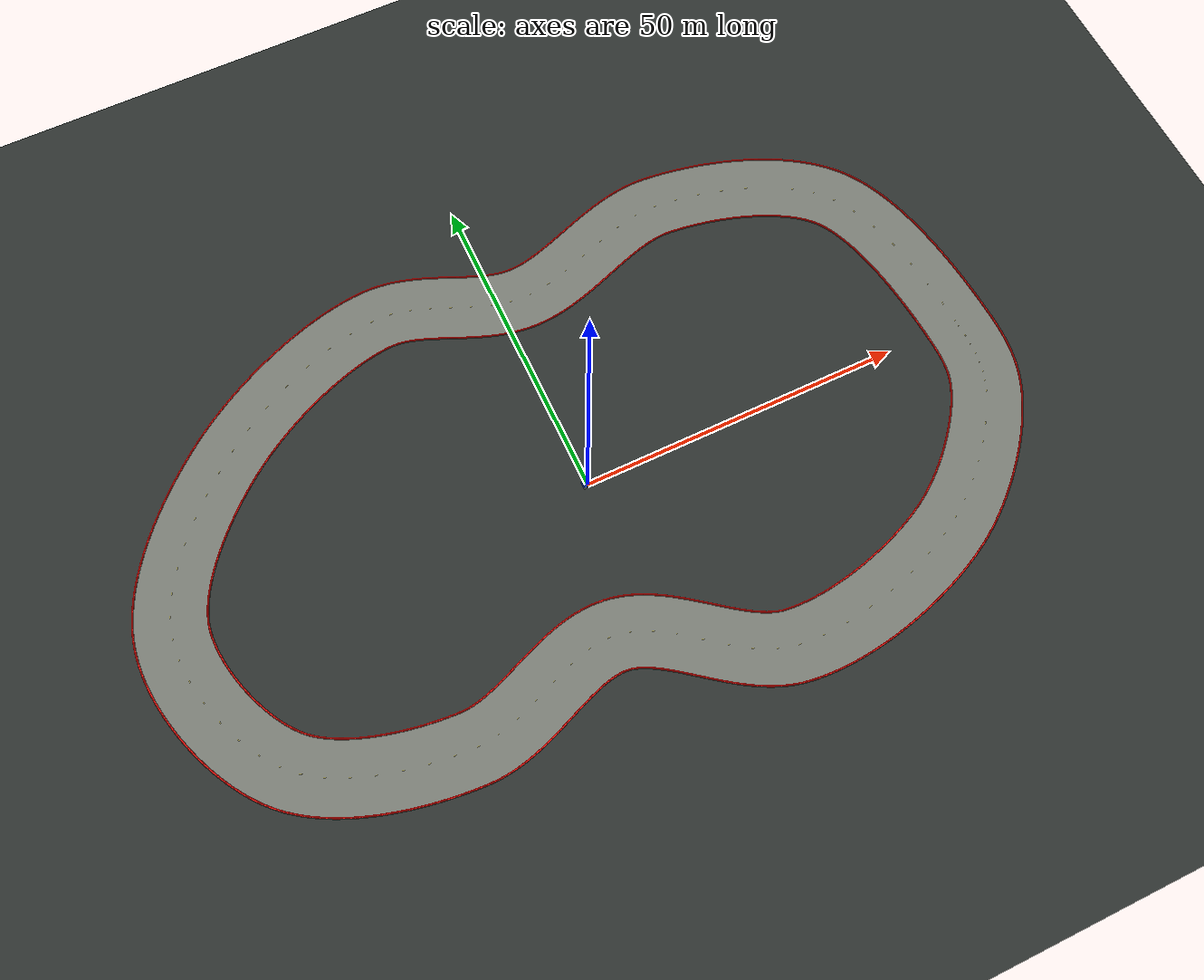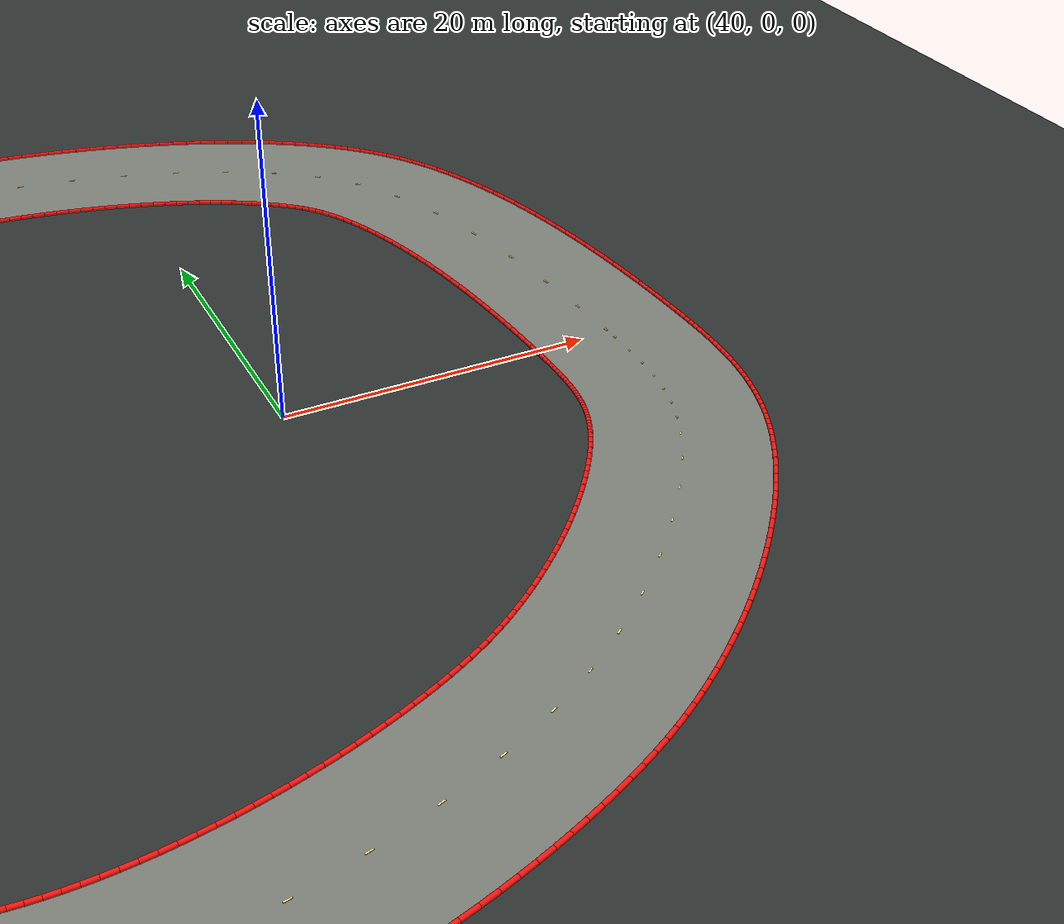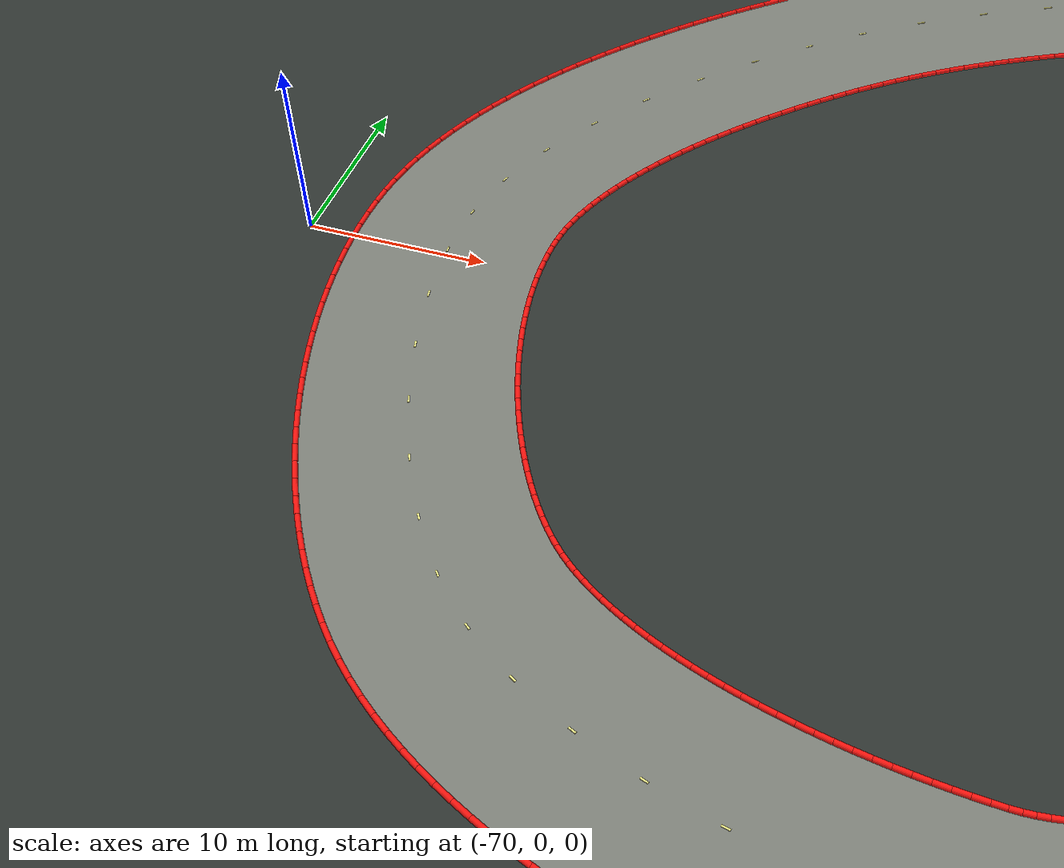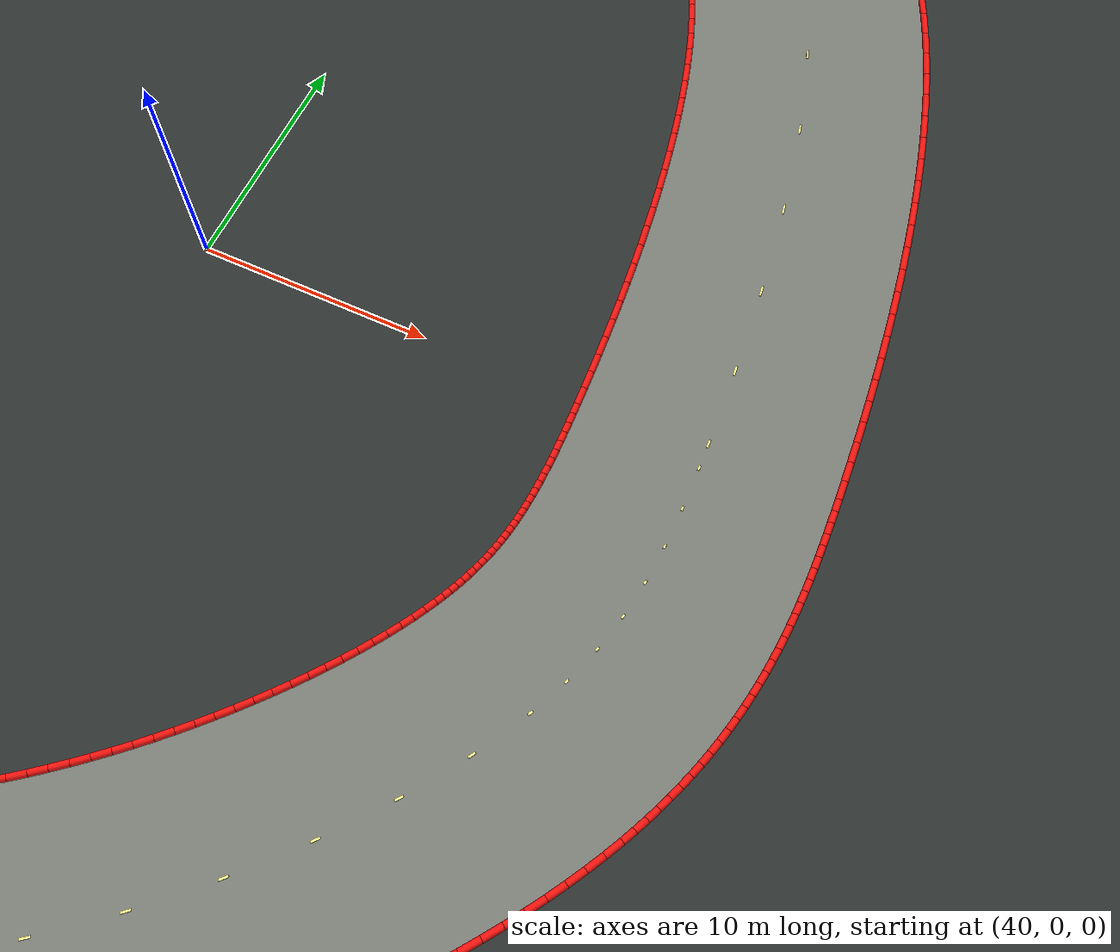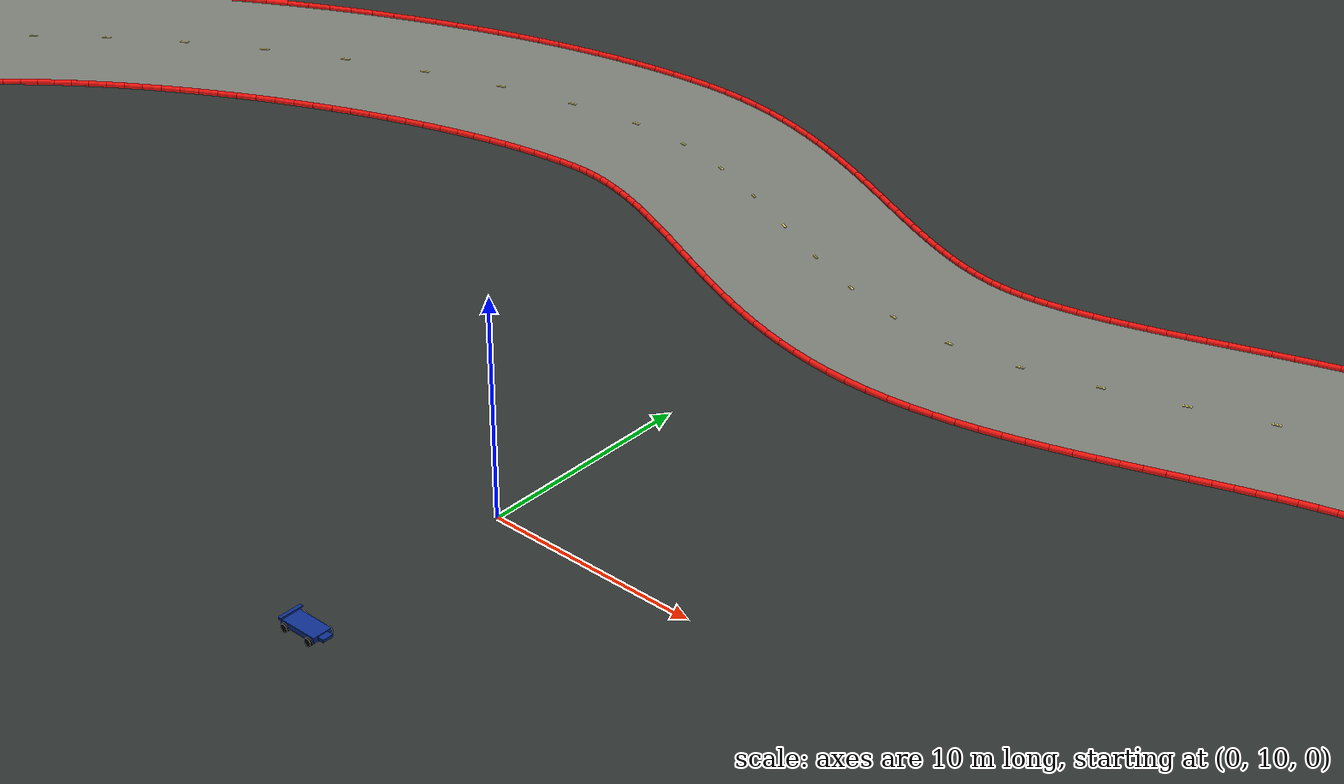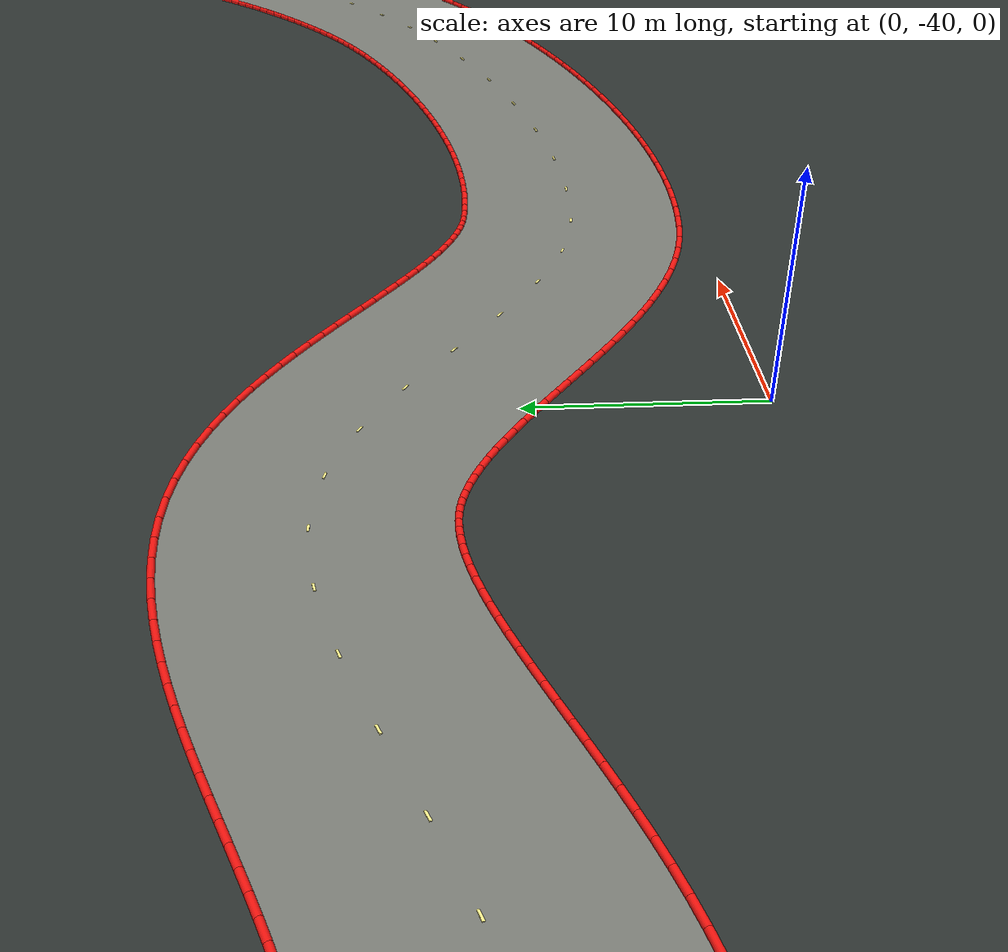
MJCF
<mujoco model="racesim_grand_prix_world">
  <compiler angle="degree" autolimits="true"/>
  <option timestep="0.02" gravity="0 0 -9.81"/>
  <visual>
    <global offwidth="1280" offheight="960"/>
    <headlight ambient="0.35 0.35 0.35" diffuse="0.8 0.8 0.8"/>
  </visual>

  <include file="car.xml"/>
  <include file="grand_prix_track.xml"/>

  <asset>
    <texture name="grid" type="2d" builtin="checker" width="512" height="512"
             rgb1="0.16 0.18 0.17" rgb2="0.20 0.22 0.21"/>
    <material name="ground" texture="grid" texrepeat="14 14" reflectance="0.05"/>
  </asset>

  <worldbody>
    <light name="sun" pos="0 0 30" dir="0 0 -1" diffuse="1.0 1.0 1.0" ambient="0.25 0.25 0.25"/>
    <geom name="ground" type="plane" size="120 120 0.1" material="ground"/>
    <camera name="topdown" pos="0 0 155" xyaxes="1 0 0 0 1 0" fovy="42"/>
    <camera name="follow" mode="trackcom" target="car" pos="-5 0 3" xyaxes="0 -1 0 0.5 0 0.866"/>
  </worldbody>
</mujoco>

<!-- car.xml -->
<mujoco model="simple_car">
  <default>
    <geom friction="1.2 0.02 0.001" density="600"/>
    <joint damping="0.1"/>
  </default>

  <asset>
    <material name="chassis_blue" rgba="0.05 0.18 0.55 1"/>
    <material name="wheel_dark" rgba="0.02 0.02 0.025 1"/>
  </asset>

  <worldbody>
    <body name="car" pos="0 0 0.28">
      <freejoint name="root"/>
      <geom name="chassis" type="box" size="0.9 0.45 0.12" material="chassis_blue"/>
      <geom name="nose" type="box" pos="0.75 0 0.02" size="0.45 0.25 0.06" material="chassis_blue"/>
      <geom name="rear_wing" type="box" pos="-0.85 0 0.22" size="0.08 0.55 0.04" material="chassis_blue"/>

      <body name="front_left_wheel" pos="0.65 0.48 -0.12">
        <joint name="front_left_spin" type="hinge" axis="0 1 0"/>
        <geom type="cylinder" size="0.18 0.08" euler="90 0 0" material="wheel_dark"/>
      </body>
      <body name="front_right_wheel" pos="0.65 -0.48 -0.12">
        <joint name="front_right_spin" type="hinge" axis="0 1 0"/>
        <geom type="cylinder" size="0.18 0.08" euler="90 0 0" material="wheel_dark"/>
      </body>
      <body name="rear_left_wheel" pos="-0.65 0.48 -0.12">
        <joint name="rear_left_spin" type="hinge" axis="0 1 0"/>
        <geom type="cylinder" size="0.18 0.08" euler="90 0 0" material="wheel_dark"/>
      </body>
      <body name="rear_right_wheel" pos="-0.65 -0.48 -0.12">
        <joint name="rear_right_spin" type="hinge" axis="0 1 0"/>
        <geom type="cylinder" size="0.18 0.08" euler="90 0 0" material="wheel_dark"/>
      </body>
    </body>
  </worldbody>
</mujoco>

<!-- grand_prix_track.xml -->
<mujoco model="grand_prix_track_visuals">
  <asset>
    <mesh name="track_surface_mesh" inertia="shell" vertex="56.75426 -0.21137 0.02200 56.72285 0.52343 0.02200 56.68521 1.29650 0.02200 56.64056 2.10583 0.02200 56.58818 2.94814 0.02200 56.52736 3.82008 0.02200 56.45741 4.71824 0.02200 56.37764 5.63920 0.02200 56.28737 6.57949 0.02200 56.18596 7.53560 0.02200 56.07278 8.50399 0.02200 55.94721 9.48107 0.02200 55.80870 10.46321 0.02200 55.65671 11.44674 0.02200 55.49074 12.42794 0.02200 55.31039 13.40301 0.02200 55.11529 14.36812 0.02200 54.90518 15.31934 0.02200 54.67989 16.25269 0.02200 54.43940 17.16411 0.02200 54.18386 18.04945 0.02200 53.91360 18.90449 0.02200 53.62921 19.72493 0.02200 53.33160 20.50643 0.02200 53.02203 21.24464 0.02200 52.70221 21.93524 0.02200 52.37437 22.57407 0.02200 52.04133 23.15726 0.02200 51.70653 23.68145 0.02200 51.37397 24.14409 0.02200 51.03204 24.56230 0.02200 50.66656 24.95927 0.02200 50.25094 25.36984 0.02200 49.79680 25.77953 0.02200 49.30498 26.18672 0.02200 48.77669 26.58978 0.02200 48.21339 26.98719 0.02200 47.61676 27.37756 0.02200 46.98866 27.75961 0.02200 46.33108 28.13220 0.02200 45.64608 28.49432 0.02200 44.93579 28.84508 0.02200 44.20240 29.18371 0.02200 43.44810 29.50955 0.02200 42.67513 29.82201 0.02200 41.88572 30.12061 0.02200 41.08209 30.40492 0.02200 40.26650 30.67458 0.02200 39.44116 30.92929 0.02200 38.60833 31.16881 0.02200 37.77023 31.39291 0.02200 36.92910 31.60145 0.02200 36.08719 31.79427 0.02200 35.24673 31.97129 0.02200 34.40999 32.13243 0.02200 33.57925 32.27765 0.02200 32.75681 32.40693 0.02200 31.94499 32.52030 0.02200 31.14616 32.61779 0.02200 30.36275 32.69948 0.02200 29.64828 32.76179 0.02200 29.04044 32.79208 0.02200 28.46097 32.78796 0.02200 27.85394 32.75307 0.02200 27.21912 32.68724 0.02200 26.55700 32.59067 0.02200 25.86858 32.46397 0.02200 25.15517 32.30815 0.02200 24.41825 32.12466 0.02200 23.65935 31.91530 0.02200 22.87994 31.68215 0.02200 22.08141 31.42759 0.02200 21.26500 31.15419 0.02200 20.43181 30.86468 0.02200 19.58275 30.56195 0.02200 18.71855 30.24899 0.02200 17.83976 29.92890 0.02200 16.94673 29.60485 0.02200 16.03961 29.28012 0.02200 15.11838 28.95810 0.02200 14.18280 28.64226 0.02200 13.23246 28.33625 0.02200 12.26675 28.04388 0.02200 11.28492 27.76916 0.02200 10.28610 27.51641 0.02200 9.26932 27.29025 0.02200 8.23367 27.09573 0.02200 7.17835 26.93833 0.02200 6.10290 26.82404 0.02200 5.00735 26.75933 0.02200 3.89843 26.75098 0.02200 2.85991 26.79898 0.02200 1.84549 26.89799 0.02200 0.85750 27.04214 0.02200 -0.10333 27.22556 0.02200 -1.03694 27.44261 0.02200 -1.94380 27.68789 0.02200 -2.82475 27.95636 0.02200 -3.68085 28.24331 0.02200 -4.51330 28.54437 0.02200 -5.32327 28.85546 0.02200 -6.11194 29.17279 0.02200 -6.88034 29.49278 0.02200 -7.62939 29.81204 0.02200 -8.35981 30.12738 0.02200 -9.07219 30.43574 0.02200 -9.76689 30.73425 0.02200 -10.44413 31.02014 0.02200 -11.10392 31.29087 0.02200 -11.74614 31.54403 0.02200 -12.37053 31.77747 0.02200 -12.97674 31.98928 0.02200 -13.56441 32.17785 0.02200 -14.13324 32.34187 0.02200 -14.68308 32.48043 0.02200 -15.21412 32.59297 0.02200 -15.72698 32.67923 0.02200 -16.22293 32.73926 0.02200 -16.70400 32.77320 0.02200 -17.17311 32.78111 0.02200 -17.66816 32.76050 0.02200 -18.35969 32.69995 0.02200 -19.11101 32.61037 0.02200 -19.88937 32.49378 0.02200 -20.69203 32.35039 0.02200 -21.51631 32.18062 0.02200 -22.35967 31.98500 0.02200 -23.21964 31.76416 0.02200 -24.09384 31.51882 0.02200 -24.97998 31.24978 0.02200 -25.87581 30.95788 0.02200 -26.77917 30.64401 0.02200 -27.68793 30.30910 0.02200 -28.60003 29.95411 0.02200 -29.51343 29.58004 0.02200 -30.42614 29.18788 0.02200 -31.33619 28.77867 0.02200 -32.24163 28.35348 0.02200 -33.14053 27.91337 0.02200 -34.03098 27.45944 0.02200 -34.91108 26.99281 0.02200 -35.77893 26.51463 0.02200 -36.63265 26.02606 0.02200 -37.47035 25.52830 0.02200 -38.29012 25.02259 0.02200 -39.09007 24.51020 0.02200 -39.86828 23.99247 0.02200 -40.62284 23.47076 0.02200 -41.35180 22.94652 0.02200 -42.05319 22.42129 0.02200 -42.73300 21.89035 0.02200 -43.37440 21.37122 0.02200 -44.02712 20.82802 0.02200 -44.68190 20.26769 0.02200 -45.33686 19.69129 0.02200 -45.99015 19.09990 0.02200 -46.63995 18.49461 0.02200 -47.28443 17.87651 0.02200 -47.92181 17.24672 0.02200 -48.55029 16.60637 0.02200 -49.16810 15.95662 0.02200 -49.77346 15.29867 0.02200 -50.36463 14.63373 0.02200 -50.93987 13.96307 0.02200 -51.49746 13.28799 0.02200 -52.03567 12.60985 0.02200 -52.55285 11.93006 0.02200 -53.04733 11.25010 0.02200 -53.51750 10.57151 0.02200 -53.96182 9.89591 0.02200 -54.37877 9.22501 0.02200 -54.76696 8.56059 0.02200 -55.12508 7.90453 0.02200 -55.45195 7.25878 0.02200 -55.74658 6.62539 0.02200 -56.00815 6.00643 0.02200 -56.23611 5.40403 0.02200 -56.43017 4.82028 0.02200 -56.59039 4.25716 0.02200 -56.71719 3.71650 0.02200 -56.81289 3.18984 0.02200 -56.88071 2.66883 0.02200 -56.92892 2.10516 0.02200 -56.95534 1.50687 0.02200 -56.95891 0.87749 0.02200 -56.93897 0.22052 0.02200 -56.89515 -0.46063 0.02200 -56.82734 -1.16258 0.02200 -56.73565 -1.88209 0.02200 -56.62032 -2.61597 0.02200 -56.48179 -3.36113 0.02200 -56.32056 -4.11457 0.02200 -56.13728 -4.87332 0.02200 -55.93264 -5.63451 0.02200 -55.70746 -6.39529 0.02200 -55.46258 -7.15287 0.02200 -55.19896 -7.90448 0.02200 -54.91760 -8.64739 0.02200 -54.61958 -9.37886 0.02200 -54.30607 -10.09618 0.02200 -53.97831 -10.79667 0.02200 -53.63766 -11.47760 0.02200 -53.28558 -12.13630 0.02200 -52.92366 -12.77005 0.02200 -52.55366 -13.37616 0.02200 -52.17751 -13.95194 0.02200 -51.79737 -14.49476 0.02200 -51.41563 -15.00199 0.02200 -51.03500 -15.47112 0.02200 -50.65851 -15.89977 0.02200 -50.29337 -16.28202 0.02200 -49.92537 -16.63189 0.02200 -49.52721 -16.97503 0.02200 -49.09182 -17.31722 0.02200 -48.62007 -17.65677 0.02200 -48.11318 -17.99204 0.02200 -47.57265 -18.32156 0.02200 -47.00020 -18.64398 0.02200 -46.39769 -18.95809 0.02200 -45.76710 -19.26288 0.02200 -45.11049 -19.55745 0.02200 -44.42995 -19.84105 0.02200 -43.72763 -20.11304 0.02200 -43.00567 -20.37291 0.02200 -42.26623 -20.62022 0.02200 -41.51146 -20.85463 0.02200 -40.74352 -21.07587 0.02200 -39.96453 -21.28373 0.02200 -39.17665 -21.47808 0.02200 -38.38198 -21.65879 0.02200 -37.58264 -21.82583 0.02200 -36.78075 -21.97916 0.02200 -35.97840 -22.11881 0.02200 -35.17772 -22.24481 0.02200 -34.38081 -22.35723 0.02200 -33.58979 -22.45618 0.02200 -32.80680 -22.54177 0.02200 -32.03399 -22.61415 0.02200 -31.27355 -22.67349 0.02200 -30.52769 -22.71999 0.02200 -29.85890 -22.75190 0.02200 -29.31892 -22.75713 0.02200 -28.81443 -22.73075 0.02200 -28.27969 -22.67389 0.02200 -27.71452 -22.58588 0.02200 -27.11964 -22.46659 0.02200 -26.49637 -22.31646 0.02200 -25.84634 -22.13654 0.02200 -25.17132 -21.92838 0.02200 -24.47304 -21.69401 0.02200 -23.75315 -21.43583 0.02200 -23.01307 -21.15652 0.02200 -22.25403 -20.85902 0.02200 -21.47703 -20.54644 0.02200 -20.68277 -20.22203 0.02200 -19.87173 -19.88919 0.02200 -19.04411 -19.55142 0.02200 -18.19984 -19.21234 0.02200 -17.33858 -18.87569 0.02200 -16.45972 -18.54538 0.02200 -15.56239 -18.22553 0.02200 -14.64548 -17.92051 0.02200 -13.70767 -17.63501 0.02200 -12.74751 -17.37416 0.02200 -11.76353 -17.14363 0.02200 -10.75439 -16.94966 0.02200 -9.71914 -16.79921 0.02200 -8.65752 -16.69992 0.02200 -7.57035 -16.66004 0.02200 -6.45993 -16.68818 0.02200 -5.32726 -16.79328 0.02200 -4.18760 -16.98288 0.02200 -3.07925 -17.24986 0.02200 -2.01534 -17.58182 0.02200 -0.99573 -17.96833 0.02200 -0.01865 -18.39997 0.02200 0.91873 -18.86840 0.02200 1.81973 -19.36640 0.02200 2.68785 -19.88767 0.02200 3.52645 -20.42666 0.02200 4.33867 -20.97838 0.02200 5.12728 -21.53825 0.02200 5.89468 -22.10198 0.02200 6.64290 -22.66547 0.02200 7.37359 -23.22472 0.02200 8.08803 -23.77583 0.02200 8.78713 -24.31492 0.02200 9.47147 -24.83816 0.02200 10.14127 -25.34179 0.02200 10.79640 -25.82210 0.02200 11.43640 -26.27549 0.02200 12.06044 -26.69856 0.02200 12.66740 -27.08815 0.02200 13.25586 -27.44150 0.02200 13.82420 -27.75632 0.02200 14.37077 -28.03099 0.02200 14.89405 -28.26469 0.02200 15.39302 -28.45747 0.02200 15.86756 -28.61032 0.02200 16.31891 -28.72504 0.02200 16.79963 -28.81125 0.02200 17.43684 -28.89085 0.02200 18.14987 -28.95621 0.02200 18.89246 -29.00025 0.02200 19.66201 -29.02267 0.02200 20.45594 -29.02333 0.02200 21.27170 -29.00227 0.02200 22.10679 -28.95965 0.02200 22.95879 -28.89575 0.02200 23.82531 -28.81095 0.02200 24.70400 -28.70569 0.02200 25.59258 -28.58048 0.02200 26.48879 -28.43590 0.02200 27.39044 -28.27256 0.02200 28.29533 -28.09111 0.02200 29.20132 -27.89226 0.02200 30.10628 -27.67672 0.02200 31.00810 -27.44525 0.02200 31.90469 -27.19863 0.02200 32.79395 -26.93767 0.02200 33.67381 -26.66323 0.02200 34.54219 -26.37616 0.02200 35.39699 -26.07736 0.02200 36.23612 -25.76779 0.02200 37.05746 -25.44842 0.02200 37.85889 -25.12027 0.02200 38.63825 -24.78445 0.02200 39.39333 -24.44209 0.02200 40.12190 -24.09443 0.02200 40.82167 -23.74282 0.02200 41.48727 -23.39037 0.02200 42.04760 -23.07619 0.02200 42.60803 -22.74339 0.02200 43.17184 -22.39035 0.02200 43.73762 -22.01809 0.02200 44.30400 -21.62767 0.02200 44.86967 -21.22019 0.02200 45.43337 -20.79678 0.02200 45.99386 -20.35858 0.02200 46.54997 -19.90677 0.02200 47.10054 -19.44254 0.02200 47.64444 -18.96710 0.02200 48.18058 -18.48168 0.02200 48.70787 -17.98750 0.02200 49.22526 -17.48585 0.02200 49.73170 -16.97799 0.02200 50.22617 -16.46523 0.02200 50.70764 -15.94889 0.02200 51.17510 -15.43033 0.02200 51.62755 -14.91095 0.02200 52.06398 -14.39215 0.02200 52.48341 -13.87542 0.02200 52.88485 -13.36229 0.02200 53.26729 -12.85434 0.02200 53.62976 -12.35325 0.02200 53.97128 -11.86078 0.02200 54.29086 -11.37881 0.02200 54.58756 -10.90936 0.02200 54.86044 -10.45462 0.02200 55.10858 -10.01697 0.02200 55.33650 -9.58871 0.02200 55.48127 -9.30006 0.02200 55.61907 -9.01069 0.02200 55.74578 -8.72920 0.02200 55.86212 -8.45475 0.02200 55.96881 -8.18637 0.02200 56.06655 -7.92304 0.02200 56.15602 -7.66364 0.02200 56.23785 -7.40700 0.02200 56.31264 -7.15191 0.02200 56.38091 -6.89708 0.02200 56.44313 -6.64124 0.02200 56.49970 -6.38310 0.02200 56.55095 -6.12141 0.02200 56.59714 -5.85491 0.02200 56.63849 -5.58245 0.02200 56.67516 -5.30291 0.02200 56.70727 -5.01525 0.02200 56.73493 -4.71852 0.02200 56.75820 -4.41184 0.02200 56.77715 -4.09444 0.02200 56.79188 -3.76562 0.02200 56.80244 -3.42474 0.02200 56.80895 -3.07126 0.02200 56.81153 -2.70469 0.02200 56.81032 -2.32458 0.02200 56.80548 -1.93056 0.02200 56.79721 -1.52227 0.02200 56.78573 -1.09939 0.02200 56.77129 -0.66164 0.02200 67.24574 0.21137 0.02200 67.21189 1.00304 0.02200 67.17107 1.84108 0.02200 67.12252 2.72094 0.02200 67.06540 3.63934 0.02200 66.99887 4.59309 0.02200 66.92207 5.57903 0.02200 66.83413 6.59403 0.02200 66.73418 7.63502 0.02200 66.62132 8.69894 0.02200 66.49462 9.78278 0.02200 66.35312 10.88357 0.02200 66.19587 11.99840 0.02200 66.02182 13.12437 0.02200 65.82991 14.25867 0.02200 65.61903 15.39851 0.02200 65.38796 16.54120 0.02200 65.13542 17.68409 0.02200 64.86003 18.82462 0.02200 64.56024 19.96030 0.02200 64.23438 21.08871 0.02200 63.88054 22.20753 0.02200 63.49658 23.31450 0.02200 63.08006 24.40740 0.02200 62.62815 25.48404 0.02200 62.13758 26.54217 0.02200 61.60457 27.57941 0.02200 61.02477 28.59307 0.02200 60.39317 29.57995 0.02200 59.70421 30.53605 0.02200 58.96796 31.43770 0.02200 58.22622 32.24635 0.02200 57.46120 33.00280 0.02200 56.66499 33.72169 0.02200 55.84050 34.40481 0.02200 54.99025 35.05392 0.02200 54.11652 35.67069 0.02200 53.22135 36.25667 0.02200 52.30662 36.81331 0.02200 51.37408 37.34187 0.02200 50.42540 37.84354 0.02200 49.46218 38.31935 0.02200 48.48597 38.77021 0.02200 47.49830 39.19696 0.02200 46.50068 39.60031 0.02200 45.49462 39.98092 0.02200 44.48160 40.33937 0.02200 43.46314 40.67615 0.02200 42.44071 40.99173 0.02200 41.41583 41.28651 0.02200 40.39000 41.56084 0.02200 39.36470 41.81506 0.02200 38.34143 42.04943 0.02200 37.32169 42.26423 0.02200 36.30693 42.45966 0.02200 35.29862 42.63592 0.02200 34.29820 42.79318 0.02200 33.30706 42.93158 0.02200 32.32658 43.05123 0.02200 31.35807 43.15219 0.02200 30.35172 43.23821 0.02200 29.25836 43.28982 0.02200 28.12735 43.28266 0.02200 27.01540 43.21953 0.02200 25.92349 43.10700 0.02200 24.85187 42.95130 0.02200 23.80032 42.75825 0.02200 22.76826 42.53325 0.02200 21.75497 42.28128 0.02200 20.75970 42.00698 0.02200 19.78171 41.71465 0.02200 18.82038 41.40836 0.02200 17.87520 41.09196 0.02200 16.94586 40.76914 0.02200 16.03218 40.44342 0.02200 15.13419 40.11826 0.02200 14.25211 39.79696 0.02200 13.38633 39.48278 0.02200 12.53745 39.17885 0.02200 11.70627 38.88823 0.02200 10.89376 38.61383 0.02200 10.10110 38.35846 0.02200 9.32965 38.12472 0.02200 8.58091 37.91501 0.02200 7.85652 37.73145 0.02200 7.15819 37.57583 0.02200 6.48759 37.44953 0.02200 5.84628 37.35349 0.02200 5.23548 37.28815 0.02200 4.65589 37.25344 0.02200 4.10157 37.24902 0.02200 3.61473 37.27181 0.02200 3.11617 37.32082 0.02200 2.60268 37.39609 0.02200 2.07262 37.49763 0.02200 1.52505 37.62525 0.02200 0.95955 37.77851 0.02200 0.37605 37.95660 0.02200 -0.22527 38.15839 0.02200 -0.84411 38.38241 0.02200 -1.48018 38.62688 0.02200 -2.13322 38.88977 0.02200 -2.80307 39.16882 0.02200 -3.48971 39.46156 0.02200 -4.19331 39.76534 0.02200 -4.91419 40.07738 0.02200 -5.65286 40.39472 0.02200 -6.41001 40.71426 0.02200 -7.18652 41.03273 0.02200 -7.98339 41.34667 0.02200 -8.80180 41.65240 0.02200 -9.64297 41.94599 0.02200 -10.50816 42.22321 0.02200 -11.39857 42.47950 0.02200 -12.31523 42.70996 0.02200 -13.25886 42.90931 0.02200 -14.22972 43.07193 0.02200 -15.22744 43.19196 0.02200 -16.25088 43.26341 0.02200 -17.29801 43.28037 0.02200 -18.33184 43.23950 0.02200 -19.43329 43.14492 0.02200 -20.50936 43.01684 0.02200 -21.58965 42.85520 0.02200 -22.67378 42.66168 0.02200 -23.76126 42.43783 0.02200 -24.85150 42.18504 0.02200 -25.94383 41.90461 0.02200 -27.03748 41.59776 0.02200 -28.13161 41.26562 0.02200 -29.22532 40.90930 0.02200 -30.31763 40.52982 0.02200 -31.40753 40.12820 0.02200 -32.49393 39.70540 0.02200 -33.57572 39.26238 0.02200 -34.65178 38.80006 0.02200 -35.72092 38.31933 0.02200 -36.78194 37.82109 0.02200 -37.83363 37.30617 0.02200 -38.87477 36.77543 0.02200 -39.90410 36.22968 0.02200 -40.92039 35.66971 0.02200 -41.92237 35.09627 0.02200 -42.90881 34.51012 0.02200 -43.87845 33.91194 0.02200 -44.83005 33.30239 0.02200 -45.76239 32.68209 0.02200 -46.67424 32.05159 0.02200 -47.56440 31.41137 0.02200 -48.43169 30.76184 0.02200 -49.26700 30.10965 0.02200 -50.03541 29.48793 0.02200 -50.79905 28.85241 0.02200 -51.56397 28.19782 0.02200 -52.32879 27.52474 0.02200 -53.09211 26.83373 0.02200 -53.85255 26.12537 0.02200 -54.60865 25.40019 0.02200 -55.35900 24.65875 0.02200 -56.10214 23.90155 0.02200 -56.83660 23.12907 0.02200 -57.56092 22.34178 0.02200 -58.27361 21.54011 0.02200 -58.97317 20.72444 0.02200 -59.65809 19.89512 0.02200 -60.32683 19.05243 0.02200 -60.97783 18.19661 0.02200 -61.60952 17.32784 0.02200 -62.22025 16.44622 0.02200 -62.80835 15.55177 0.02200 -63.37208 14.64445 0.02200 -63.90961 13.72411 0.02200 -64.41900 12.79054 0.02200 -64.89818 11.84341 0.02200 -65.34493 10.88234 0.02200 -65.75681 9.90690 0.02200 -66.13114 8.91662 0.02200 -66.46496 7.91105 0.02200 -66.75499 6.88985 0.02200 -66.99756 5.85285 0.02200 -67.18711 4.81016 0.02200 -67.31969 3.79913 0.02200 -67.40675 2.78723 0.02200 -67.45203 1.77056 0.02200 -67.45813 0.74976 0.02200 -67.42730 -0.27449 0.02200 -67.36143 -1.30147 0.02200 -67.26220 -2.33035 0.02200 -67.13108 -3.36026 0.02200 -66.96934 -4.39018 0.02200 -66.77814 -5.41907 0.02200 -66.55851 -6.44575 0.02200 -66.31138 -7.46903 0.02200 -66.03758 -8.48762 0.02200 -65.73789 -9.50021 0.02200 -65.41298 -10.50542 0.02200 -65.06349 -11.50186 0.02200 -64.68996 -12.48810 0.02200 -64.29285 -13.46271 0.02200 -63.87257 -14.42423 0.02200 -63.42943 -15.37121 0.02200 -62.96362 -16.30217 0.02200 -62.47525 -17.21567 0.02200 -61.96427 -18.11022 0.02200 -61.43048 -18.98437 0.02200 -60.87352 -19.83663 0.02200 -60.29278 -20.66550 0.02200 -59.68741 -21.46941 0.02200 -59.05628 -22.24673 0.02200 -58.39791 -22.99566 0.02200 -57.70663 -23.71798 0.02200 -56.97329 -24.41501 0.02200 -56.20310 -25.07950 0.02200 -55.40663 -25.70609 0.02200 -54.58649 -26.29689 0.02200 -53.74496 -26.85393 0.02200 -52.88403 -27.37911 0.02200 -52.00550 -27.87420 0.02200 -51.11098 -28.34079 0.02200 -50.20200 -28.78032 0.02200 -49.27999 -29.19411 0.02200 -48.34635 -29.58332 0.02200 -47.40243 -29.94899 0.02200 -46.44959 -30.29205 0.02200 -45.48915 -30.61335 0.02200 -44.52247 -30.91364 0.02200 -43.55088 -31.19361 0.02200 -42.57575 -31.45386 0.02200 -41.59844 -31.69497 0.02200 -40.62031 -31.91744 0.02200 -39.64276 -32.12175 0.02200 -38.66715 -32.30832 0.02200 -37.69489 -32.47756 0.02200 -36.72736 -32.62983 0.02200 -35.76593 -32.76547 0.02200 -34.81200 -32.88481 0.02200 -33.86690 -32.98812 0.02200 -32.93200 -33.07568 0.02200 -32.00859 -33.14773 0.02200 -31.09795 -33.20449 0.02200 -30.14110 -33.24810 0.02200 -29.08706 -33.25457 0.02200 -27.99213 -33.19850 0.02200 -26.92260 -33.08582 0.02200 -25.87917 -32.92424 0.02200 -24.86167 -32.72093 0.02200 -23.86930 -32.48251 0.02200 -22.90096 -32.21497 0.02200 -21.95543 -31.92378 0.02200 -21.03150 -31.61398 0.02200 -20.12806 -31.29021 0.02200 -19.24421 -30.95682 0.02200 -18.37927 -30.61792 0.02200 -17.53277 -30.27746 0.02200 -16.70454 -29.93922 0.02200 -15.89462 -29.60684 0.02200 -15.10337 -29.28387 0.02200 -14.33138 -28.97374 0.02200 -13.57952 -28.67974 0.02200 -12.84894 -28.40501 0.02200 -12.14104 -28.15248 0.02200 -11.45746 -27.92483 0.02200 -10.80006 -27.72440 0.02200 -10.17081 -27.55309 0.02200 -9.57174 -27.41232 0.02200 -9.00470 -27.30285 0.02200 -8.47118 -27.22478 0.02200 -7.97197 -27.17752 0.02200 -7.50679 -27.15985 0.02200 -7.07387 -27.17022 0.02200 -6.67274 -27.20672 0.02200 -6.28274 -27.27172 0.02200 -5.87866 -27.36980 0.02200 -5.44600 -27.50555 0.02200 -4.98351 -27.68160 0.02200 -4.49159 -27.89959 0.02200 -3.97167 -28.16001 0.02200 -3.42572 -28.46230 0.02200 -2.85582 -28.80494 0.02200 -2.26398 -29.18570 0.02200 -1.65194 -29.60175 0.02200 -1.02110 -30.04986 0.02200 -0.37247 -30.52652 0.02200 0.29329 -31.02803 0.02200 0.97593 -31.55058 0.02200 1.67554 -32.09027 0.02200 2.39258 -32.64317 0.02200 3.12787 -33.20529 0.02200 3.88257 -33.77261 0.02200 4.65818 -34.34103 0.02200 5.45655 -34.90633 0.02200 6.27988 -35.46412 0.02200 7.13069 -36.00975 0.02200 8.01177 -36.53818 0.02200 8.92611 -37.04388 0.02200 9.87677 -37.52067 0.02200 10.86662 -37.96159 0.02200 11.89808 -38.35875 0.02200 12.97265 -38.70337 0.02200 14.09047 -38.98584 0.02200 15.20037 -39.18875 0.02200 16.29691 -39.32879 0.02200 17.35838 -39.42633 0.02200 18.42763 -39.48996 0.02200 19.50389 -39.52148 0.02200 20.58637 -39.52252 0.02200 21.67422 -39.49455 0.02200 22.76656 -39.43890 0.02200 23.86243 -39.35680 0.02200 24.96085 -39.24937 0.02200 26.06077 -39.11766 0.02200 27.16110 -38.96267 0.02200 28.26069 -38.78532 0.02200 29.35839 -38.58649 0.02200 30.45299 -38.36703 0.02200 31.54325 -38.12775 0.02200 32.62793 -37.86943 0.02200 33.70574 -37.59280 0.02200 34.77540 -37.29858 0.02200 35.83562 -36.98746 0.02200 36.88510 -36.66011 0.02200 37.92253 -36.31714 0.02200 38.94663 -35.95917 0.02200 39.95610 -35.58674 0.02200 40.94967 -35.20038 0.02200 41.92610 -34.80055 0.02200 42.88416 -34.38768 0.02200 43.82268 -33.96211 0.02200 44.74049 -33.52410 0.02200 45.63651 -33.07381 0.02200 46.51273 -32.60963 0.02200 47.29614 -32.17030 0.02200 48.07474 -31.70804 0.02200 48.84373 -31.22662 0.02200 49.60296 -30.72716 0.02200 50.35226 -30.21071 0.02200 51.09140 -29.67833 0.02200 51.82009 -29.13103 0.02200 52.53803 -28.56979 0.02200 53.24484 -27.99557 0.02200 53.94015 -27.40934 0.02200 54.62353 -26.81200 0.02200 55.29453 -26.20448 0.02200 55.95270 -25.58767 0.02200 56.59755 -24.96244 0.02200 57.22857 -24.32966 0.02200 57.84526 -23.69015 0.02200 58.44708 -23.04473 0.02200 59.03352 -22.39419 0.02200 59.60401 -21.73926 0.02200 60.15804 -21.08067 0.02200 60.69503 -20.41907 0.02200 61.21445 -19.75508 0.02200 61.71573 -19.08924 0.02200 62.19832 -18.42201 0.02200 62.66165 -17.75378 0.02200 63.10516 -17.08479 0.02200 63.52826 -16.41517 0.02200 63.93035 -15.74486 0.02200 64.31077 -15.07362 0.02200 64.66350 -14.41129 0.02200 64.91408 -13.91223 0.02200 65.14716 -13.42267 0.02200 65.36755 -12.93295 0.02200 65.57523 -12.44292 0.02200 65.77015 -11.95249 0.02200 65.95230 -11.46167 0.02200 66.12168 -10.97052 0.02200 66.27835 -10.47921 0.02200 66.42239 -9.98791 0.02200 66.55397 -9.49687 0.02200 66.67330 -9.00633 0.02200 66.78067 -8.51656 0.02200 66.87643 -8.02779 0.02200 66.96101 -7.54021 0.02200 67.03486 -7.05398 0.02200 67.09853 -6.56917 0.02200 67.15256 -6.08579 0.02200 67.19754 -5.60376 0.02200 67.23409 -5.12293 0.02200 67.26281 -4.64304 0.02200 67.28432 -4.16377 0.02200 67.29922 -3.68470 0.02200 67.30810 -3.20537 0.02200 67.31151 -2.72524 0.02200 67.31000 -2.24370 0.02200 67.30409 -1.76011 0.02200 67.29427 -1.27380 0.02200 67.28100 -0.78405 0.02200 67.26472 -0.29013 0.02200" face="0 391 1 0 390 391 1 392 2 1 391 392 2 393 3 2 392 393 3 394 4 3 393 394 4 395 5 4 394 395 5 396 6 5 395 396 6 397 7 6 396 397 7 398 8 7 397 398 8 399 9 8 398 399 9 400 10 9 399 400 10 401 11 10 400 401 11 402 12 11 401 402 12 403 13 12 402 403 13 404 14 13 403 404 14 405 15 14 404 405 15 406 16 15 405 406 16 407 17 16 406 407 17 408 18 17 407 408 18 409 19 18 408 409 19 410 20 19 409 410 20 411 21 20 410 411 21 412 22 21 411 412 22 413 23 22 412 413 23 414 24 23 413 414 24 415 25 24 414 415 25 416 26 25 415 416 26 417 27 26 416 417 27 418 28 27 417 418 28 419 29 28 418 419 29 420 30 29 419 420 30 421 31 30 420 421 31 422 32 31 421 422 32 423 33 32 422 423 33 424 34 33 423 424 34 425 35 34 424 425 35 426 36 35 425 426 36 427 37 36 426 427 37 428 38 37 427 428 38 429 39 38 428 429 39 430 40 39 429 430 40 431 41 40 430 431 41 432 42 41 431 432 42 433 43 42 432 433 43 434 44 43 433 434 44 435 45 44 434 435 45 436 46 45 435 436 46 437 47 46 436 437 47 438 48 47 437 438 48 439 49 48 438 439 49 440 50 49 439 440 50 441 51 50 440 441 51 442 52 51 441 442 52 443 53 52 442 443 53 444 54 53 443 444 54 445 55 54 444 445 55 446 56 55 445 446 56 447 57 56 446 447 57 448 58 57 447 448 58 449 59 58 448 449 59 450 60 59 449 450 60 451 61 60 450 451 61 452 62 61 451 452 62 453 63 62 452 453 63 454 64 63 453 454 64 455 65 64 454 455 65 456 66 65 455 456 66 457 67 66 456 457 67 458 68 67 457 458 68 459 69 68 458 459 69 460 70 69 459 460 70 461 71 70 460 461 71 462 72 71 461 462 72 463 73 72 462 463 73 464 74 73 463 464 74 465 75 74 464 465 75 466 76 75 465 466 76 467 77 76 466 467 77 468 78 77 467 468 78 469 79 78 468 469 79 470 80 79 469 470 80 471 81 80 470 471 81 472 82 81 471 472 82 473 83 82 472 473 83 474 84 83 473 474 84 475 85 84 474 475 85 476 86 85 475 476 86 477 87 86 476 477 87 478 88 87 477 478 88 479 89 88 478 479 89 480 90 89 479 480 90 481 91 90 480 481 91 482 92 91 481 482 92 483 93 92 482 483 93 484 94 93 483 484 94 485 95 94 484 485 95 486 96 95 485 486 96 487 97 96 486 487 97 488 98 97 487 488 98 489 99 98 488 489 99 490 100 99 489 490 100 491 101 100 490 491 101 492 102 101 491 492 102 493 103 102 492 493 103 494 104 103 493 494 104 495 105 104 494 495 105 496 106 105 495 496 106 497 107 106 496 497 107 498 108 107 497 498 108 499 109 108 498 499 109 500 110 109 499 500 110 501 111 110 500 501 111 502 112 111 501 502 112 503 113 112 502 503 113 504 114 113 503 504 114 505 115 114 504 505 115 506 116 115 505 506 116 507 117 116 506 507 117 508 118 117 507 508 118 509 119 118 508 509 119 510 120 119 509 510 120 511 121 120 510 511 121 512 122 121 511 512 122 513 123 122 512 513 123 514 124 123 513 514 124 515 125 124 514 515 125 516 126 125 515 516 126 517 127 126 516 517 127 518 128 127 517 518 128 519 129 128 518 519 129 520 130 129 519 520 130 521 131 130 520 521 131 522 132 131 521 522 132 523 133 132 522 523 133 524 134 133 523 524 134 525 135 134 524 525 135 526 136 135 525 526 136 527 137 136 526 527 137 528 138 137 527 528 138 529 139 138 528 529 139 530 140 139 529 530 140 531 141 140 530 531 141 532 142 141 531 532 142 533 143 142 532 533 143 534 144 143 533 534 144 535 145 144 534 535 145 536 146 145 535 536 146 537 147 146 536 537 147 538 148 147 537 538 148 539 149 148 538 539 149 540 150 149 539 540 150 541 151 150 540 541 151 542 152 151 541 542 152 543 153 152 542 543 153 544 154 153 543 544 154 545 155 154 544 545 155 546 156 155 545 546 156 547 157 156 546 547 157 548 158 157 547 548 158 549 159 158 548 549 159 550 160 159 549 550 160 551 161 160 550 551 161 552 162 161 551 552 162 553 163 162 552 553 163 554 164 163 553 554 164 555 165 164 554 555 165 556 166 165 555 556 166 557 167 166 556 557 167 558 168 167 557 558 168 559 169 168 558 559 169 560 170 169 559 560 170 561 171 170 560 561 171 562 172 171 561 562 172 563 173 172 562 563 173 564 174 173 563 564 174 565 175 174 564 565 175 566 176 175 565 566 176 567 177 176 566 567 177 568 178 177 567 568 178 569 179 178 568 569 179 570 180 179 569 570 180 571 181 180 570 571 181 572 182 181 571 572 182 573 183 182 572 573 183 574 184 183 573 574 184 575 185 184 574 575 185 576 186 185 575 576 186 577 187 186 576 577 187 578 188 187 577 578 188 579 189 188 578 579 189 580 190 189 579 580 190 581 191 190 580 581 191 582 192 191 581 582 192 583 193 192 582 583 193 584 194 193 583 584 194 585 195 194 584 585 195 586 196 195 585 586 196 587 197 196 586 587 197 588 198 197 587 588 198 589 199 198 588 589 199 590 200 199 589 590 200 591 201 200 590 591 201 592 202 201 591 592 202 593 203 202 592 593 203 594 204 203 593 594 204 595 205 204 594 595 205 596 206 205 595 596 206 597 207 206 596 597 207 598 208 207 597 598 208 599 209 208 598 599 209 600 210 209 599 600 210 601 211 210 600 601 211 602 212 211 601 602 212 603 213 212 602 603 213 604 214 213 603 604 214 605 215 214 604 605 215 606 216 215 605 606 216 607 217 216 606 607 217 608 218 217 607 608 218 609 219 218 608 609 219 610 220 219 609 610 220 611 221 220 610 611 221 612 222 221 611 612 222 613 223 222 612 613 223 614 224 223 613 614 224 615 225 224 614 615 225 616 226 225 615 616 226 617 227 226 616 617 227 618 228 227 617 618 228 619 229 228 618 619 229 620 230 229 619 620 230 621 231 230 620 621 231 622 232 231 621 622 232 623 233 232 622 623 233 624 234 233 623 624 234 625 235 234 624 625 235 626 236 235 625 626 236 627 237 236 626 627 237 628 238 237 627 628 238 629 239 238 628 629 239 630 240 239 629 630 240 631 241 240 630 631 241 632 242 241 631 632 242 633 243 242 632 633 243 634 244 243 633 634 244 635 245 244 634 635 245 636 246 245 635 636 246 637 247 246 636 637 247 638 248 247 637 638 248 639 249 248 638 639 249 640 250 249 639 640 250 641 251 250 640 641 251 642 252 251 641 642 252 643 253 252 642 643 253 644 254 253 643 644 254 645 255 254 644 645 255 646 256 255 645 646 256 647 257 256 646 647 257 648 258 257 647 648 258 649 259 258 648 649 259 650 260 259 649 650 260 651 261 260 650 651 261 652 262 261 651 652 262 653 263 262 652 653 263 654 264 263 653 654 264 655 265 264 654 655 265 656 266 265 655 656 266 657 267 266 656 657 267 658 268 267 657 658 268 659 269 268 658 659 269 660 270 269 659 660 270 661 271 270 660 661 271 662 272 271 661 662 272 663 273 272 662 663 273 664 274 273 663 664 274 665 275 274 664 665 275 666 276 275 665 666 276 667 277 276 666 667 277 668 278 277 667 668 278 669 279 278 668 669 279 670 280 279 669 670 280 671 281 280 670 671 281 672 282 281 671 672 282 673 283 282 672 673 283 674 284 283 673 674 284 675 285 284 674 675 285 676 286 285 675 676 286 677 287 286 676 677 287 678 288 287 677 678 288 679 289 288 678 679 289 680 290 289 679 680 290 681 291 290 680 681 291 682 292 291 681 682 292 683 293 292 682 683 293 684 294 293 683 684 294 685 295 294 684 685 295 686 296 295 685 686 296 687 297 296 686 687 297 688 298 297 687 688 298 689 299 298 688 689 299 690 300 299 689 690 300 691 301 300 690 691 301 692 302 301 691 692 302 693 303 302 692 693 303 694 304 303 693 694 304 695 305 304 694 695 305 696 306 305 695 696 306 697 307 306 696 697 307 698 308 307 697 698 308 699 309 308 698 699 309 700 310 309 699 700 310 701 311 310 700 701 311 702 312 311 701 702 312 703 313 312 702 703 313 704 314 313 703 704 314 705 315 314 704 705 315 706 316 315 705 706 316 707 317 316 706 707 317 708 318 317 707 708 318 709 319 318 708 709 319 710 320 319 709 710 320 711 321 320 710 711 321 712 322 321 711 712 322 713 323 322 712 713 323 714 324 323 713 714 324 715 325 324 714 715 325 716 326 325 715 716 326 717 327 326 716 717 327 718 328 327 717 718 328 719 329 328 718 719 329 720 330 329 719 720 330 721 331 330 720 721 331 722 332 331 721 722 332 723 333 332 722 723 333 724 334 333 723 724 334 725 335 334 724 725 335 726 336 335 725 726 336 727 337 336 726 727 337 728 338 337 727 728 338 729 339 338 728 729 339 730 340 339 729 730 340 731 341 340 730 731 341 732 342 341 731 732 342 733 343 342 732 733 343 734 344 343 733 734 344 735 345 344 734 735 345 736 346 345 735 736 346 737 347 346 736 737 347 738 348 347 737 738 348 739 349 348 738 739 349 740 350 349 739 740 350 741 351 350 740 741 351 742 352 351 741 742 352 743 353 352 742 743 353 744 354 353 743 744 354 745 355 354 744 745 355 746 356 355 745 746 356 747 357 356 746 747 357 748 358 357 747 748 358 749 359 358 748 749 359 750 360 359 749 750 360 751 361 360 750 751 361 752 362 361 751 752 362 753 363 362 752 753 363 754 364 363 753 754 364 755 365 364 754 755 365 756 366 365 755 756 366 757 367 366 756 757 367 758 368 367 757 758 368 759 369 368 758 759 369 760 370 369 759 760 370 761 371 370 760 761 371 762 372 371 761 762 372 763 373 372 762 763 373 764 374 373 763 764 374 765 375 374 764 765 375 766 376 375 765 766 376 767 377 376 766 767 377 768 378 377 767 768 378 769 379 378 768 769 379 770 380 379 769 770 380 771 381 380 770 771 381 772 382 381 771 772 382 773 383 382 772 773 383 774 384 383 773 774 384 775 385 384 774 775 385 776 386 385 775 776 386 777 387 386 776 777 387 778 388 387 777 778 388 779 389 388 778 779 389 390 0 389 779 390"/>
    <material name="track_asphalt" rgba="0.48 0.49 0.46 1" emission="0.08"/>
    <material name="track_boundary" rgba="0.95 0.08 0.06 1" emission="0.05"/>
    <material name="track_centerline" rgba="1.0 0.95 0.55 1" emission="0.15"/>
  </asset>
  <worldbody>
    <geom name="track_surface" type="mesh" mesh="track_surface_mesh" material="track_asphalt" contype="0" conaffinity="0"/>
    <geom name="track_left_boundary_000" type="capsule" fromto="56.75426 -0.21137 0.09 56.72285 0.52343 0.09" size="0.14" material="track_boundary" contype="0" conaffinity="0"/>
    <geom name="track_left_boundary_001" type="capsule" fromto="56.72285 0.52343 0.09 56.68521 1.29650 0.09" size="0.14" material="track_boundary" contype="0" conaffinity="0"/>
    <geom name="track_left_boundary_002" type="capsule" fromto="56.68521 1.29650 0.09 56.64056 2.10583 0.09" size="0.14" material="track_boundary" contype="0" conaffinity="0"/>
    <geom name="track_left_boundary_003" type="capsule" fromto="56.64056 2.10583 0.09 56.58818 2.94814 0.09" size="0.14" material="track_boundary" contype="0" conaffinity="0"/>
    <geom name="track_left_boundary_004" type="capsule" fromto="56.58818 2.94814 0.09 56.52736 3.82008 0.09" size="0.14" material="track_boundary" contype="0" conaffinity="0"/>
    <geom name="track_left_boundary_005" type="capsule" fromto="56.52736 3.82008 0.09 56.45741 4.71824 0.09" size="0.14" material="track_boundary" contype="0" conaffinity="0"/>
    <geom name="track_left_boundary_006" type="capsule" fromto="56.45741 4.71824 0.09 56.37764 5.63920 0.09" size="0.14" material="track_boundary" contype="0" conaffinity="0"/>
    <geom name="track_left_boundary_007" type="capsule" fromto="56.37764 5.63920 0.09 56.28737 6.57949 0.09" size="0.14" material="track_boundary" contype="0" conaffinity="0"/>
    <geom name="track_left_boundary_008" type="capsule" fromto="56.28737 6.57949 0.09 56.18596 7.53560 0.09" size="0.14" material="track_boundary" contype="0" conaffinity="0"/>
    <geom name="track_left_boundary_009" type="capsule" fromto="56.18596 7.53560 0.09 56.07278 8.50399 0.09" size="0.14" material="track_boundary" contype="0" conaffinity="0"/>
    <geom name="track_left_boundary_010" type="capsule" fromto="56.07278 8.50399 0.09 55.94721 9.48107 0.09" size="0.14" material="track_boundary" contype="0" conaffinity="0"/>
    <geom name="track_left_boundary_011" type="capsule" fromto="55.94721 9.48107 0.09 55.80870 10.46321 0.09" size="0.14" material="track_boundary" contype="0" conaffinity="0"/>
    <geom name="track_left_boundary_012" type="capsule" fromto="55.80870 10.46321 0.09 55.65671 11.44674 0.09" size="0.14" material="track_boundary" contype="0" conaffinity="0"/>
    <geom name="track_left_boundary_013" type="capsule" fromto="55.65671 11.44674 0.09 55.49074 12.42794 0.09" size="0.14" material="track_boundary" contype="0" conaffinity="0"/>
    <geom name="track_left_boundary_014" type="capsule" fromto="55.49074 12.42794 0.09 55.31039 13.40301 0.09" size="0.14" material="track_boundary" contype="0" conaffinity="0"/>
    <geom name="track_left_boundary_015" type="capsule" fromto="55.31039 13.40301 0.09 55.11529 14.36812 0.09" size="0.14" material="track_boundary" contype="0" conaffinity="0"/>
    <geom name="track_left_boundary_016" type="capsule" fromto="55.11529 14.36812 0.09 54.90518 15.31934 0.09" size="0.14" material="track_boundary" contype="0" conaffinity="0"/>
    <geom name="track_left_boundary_017" type="capsule" fromto="54.90518 15.31934 0.09 54.67989 16.25269 0.09" size="0.14" material="track_boundary" contype="0" conaffinity="0"/>
    <geom name="track_left_boundary_018" type="capsule" fromto="54.67989 16.25269 0.09 54.43940 17.16411 0.09" size="0.14" material="track_boundary" contype="0" conaffinity="0"/>
    <geom name="track_left_boundary_019" type="capsule" fromto="54.43940 17.16411 0.09 54.18386 18.04945 0.09" size="0.14" material="track_boundary" contype="0" conaffinity="0"/>
    <geom name="track_left_boundary_020" type="capsule" fromto="54.18386 18.04945 0.09 53.91360 18.90449 0.09" size="0.14" material="track_boundary" contype="0" conaffinity="0"/>
    <geom name="track_left_boundary_021" type="capsule" fromto="53.91360 18.90449 0.09 53.62921 19.72493 0.09" size="0.14" material="track_boundary" contype="0" conaffinity="0"/>
    <geom name="track_left_boundary_022" type="capsule" fromto="53.62921 19.72493 0.09 53.33160 20.50643 0.09" size="0.14" material="track_boundary" contype="0" conaffinity="0"/>
    <geom name="track_left_boundary_023" type="capsule" fromto="53.33160 20.50643 0.09 53.02203 21.24464 0.09" size="0.14" material="track_boundary" contype="0" conaffinity="0"/>
    <geom name="track_left_boundary_024" type="capsule" fromto="53.02203 21.24464 0.09 52.70221 21.93524 0.09" size="0.14" material="track_boundary" contype="0" conaffinity="0"/>
    <geom name="track_left_boundary_025" type="capsule" fromto="52.70221 21.93524 0.09 52.37437 22.57407 0.09" size="0.14" material="track_boundary" contype="0" conaffinity="0"/>
    <geom name="track_left_boundary_026" type="capsule" fromto="52.37437 22.57407 0.09 52.04133 23.15726 0.09" size="0.14" material="track_boundary" contype="0" conaffinity="0"/>
    <geom name="track_left_boundary_027" type="capsule" fromto="52.04133 23.15726 0.09 51.70653 23.68145 0.09" size="0.14" material="track_boundary" contype="0" conaffinity="0"/>
    <geom name="track_left_boundary_028" type="capsule" fromto="51.70653 23.68145 0.09 51.37397 24.14409 0.09" size="0.14" material="track_boundary" contype="0" conaffinity="0"/>
    <geom name="track_left_boundary_029" type="capsule" fromto="51.37397 24.14409 0.09 51.03204 24.56230 0.09" size="0.14" material="track_boundary" contype="0" conaffinity="0"/>
    <geom name="track_left_boundary_030" type="capsule" fromto="51.03204 24.56230 0.09 50.66656 24.95927 0.09" size="0.14" material="track_boundary" contype="0" conaffinity="0"/>
    <geom name="track_left_boundary_031" type="capsule" fromto="50.66656 24.95927 0.09 50.25094 25.36984 0.09" size="0.14" material="track_boundary" contype="0" conaffinity="0"/>
    <geom name="track_left_boundary_032" type="capsule" fromto="50.25094 25.36984 0.09 49.79680 25.77953 0.09" size="0.14" material="track_boundary" contype="0" conaffinity="0"/>
    <geom name="track_left_boundary_033" type="capsule" fromto="49.79680 25.77953 0.09 49.30498 26.18672 0.09" size="0.14" material="track_boundary" contype="0" conaffinity="0"/>
    <geom name="track_left_boundary_034" type="capsule" fromto="49.30498 26.18672 0.09 48.77669 26.58978 0.09" size="0.14" material="track_boundary" contype="0" conaffinity="0"/>
    <geom name="track_left_boundary_035" type="capsule" fromto="48.77669 26.58978 0.09 48.21339 26.98719 0.09" size="0.14" material="track_boundary" contype="0" conaffinity="0"/>
    <geom name="track_left_boundary_036" type="capsule" fromto="48.21339 26.98719 0.09 47.61676 27.37756 0.09" size="0.14" material="track_boundary" contype="0" conaffinity="0"/>
    <geom name="track_left_boundary_037" type="capsule" fromto="47.61676 27.37756 0.09 46.98866 27.75961 0.09" size="0.14" material="track_boundary" contype="0" conaffinity="0"/>
    <geom name="track_left_boundary_038" type="capsule" fromto="46.98866 27.75961 0.09 46.33108 28.13220 0.09" size="0.14" material="track_boundary" contype="0" conaffinity="0"/>
    <geom name="track_left_boundary_039" type="capsule" fromto="46.33108 28.13220 0.09 45.64608 28.49432 0.09" size="0.14" material="track_boundary" contype="0" conaffinity="0"/>
    <geom name="track_left_boundary_040" type="capsule" fromto="45.64608 28.49432 0.09 44.93579 28.84508 0.09" size="0.14" material="track_boundary" contype="0" conaffinity="0"/>
    <geom name="track_left_boundary_041" type="capsule" fromto="44.93579 28.84508 0.09 44.20240 29.18371 0.09" size="0.14" material="track_boundary" contype="0" conaffinity="0"/>
    <geom name="track_left_boundary_042" type="capsule" fromto="44.20240 29.18371 0.09 43.44810 29.50955 0.09" size="0.14" material="track_boundary" contype="0" conaffinity="0"/>
    <geom name="track_left_boundary_043" type="capsule" fromto="43.44810 29.50955 0.09 42.67513 29.82201 0.09" size="0.14" material="track_boundary" contype="0" conaffinity="0"/>
    <geom name="track_left_boundary_044" type="capsule" fromto="42.67513 29.82201 0.09 41.88572 30.12061 0.09" size="0.14" material="track_boundary" contype="0" conaffinity="0"/>
    <geom name="track_left_boundary_045" type="capsule" fromto="41.88572 30.12061 0.09 41.08209 30.40492 0.09" size="0.14" material="track_boundary" contype="0" conaffinity="0"/>
    <geom name="track_left_boundary_046" type="capsule" fromto="41.08209 30.40492 0.09 40.26650 30.67458 0.09" size="0.14" material="track_boundary" contype="0" conaffinity="0"/>
    <geom name="track_left_boundary_047" type="capsule" fromto="40.26650 30.67458 0.09 39.44116 30.92929 0.09" size="0.14" material="track_boundary" contype="0" conaffinity="0"/>
    <geom name="track_left_boundary_048" type="capsule" fromto="39.44116 30.92929 0.09 38.60833 31.16881 0.09" size="0.14" material="track_boundary" contype="0" conaffinity="0"/>
    <geom name="track_left_boundary_049" type="capsule" fromto="38.60833 31.16881 0.09 37.77023 31.39291 0.09" size="0.14" material="track_boundary" contype="0" conaffinity="0"/>
    <geom name="track_left_boundary_050" type="capsule" fromto="37.77023 31.39291 0.09 36.92910 31.60145 0.09" size="0.14" material="track_boundary" contype="0" conaffinity="0"/>
    <geom name="track_left_boundary_051" type="capsule" fromto="36.92910 31.60145 0.09 36.08719 31.79427 0.09" size="0.14" material="track_boundary" contype="0" conaffinity="0"/>
    <geom name="track_left_boundary_052" type="capsule" fromto="36.08719 31.79427 0.09 35.24673 31.97129 0.09" size="0.14" material="track_boundary" contype="0" conaffinity="0"/>
    <geom name="track_left_boundary_053" type="capsule" fromto="35.24673 31.97129 0.09 34.40999 32.13243 0.09" size="0.14" material="track_boundary" contype="0" conaffinity="0"/>
    <geom name="track_left_boundary_054" type="capsule" fromto="34.40999 32.13243 0.09 33.57925 32.27765 0.09" size="0.14" material="track_boundary" contype="0" conaffinity="0"/>
    <geom name="track_left_boundary_055" type="capsule" fromto="33.57925 32.27765 0.09 32.75681 32.40693 0.09" size="0.14" material="track_boundary" contype="0" conaffinity="0"/>
    <geom name="track_left_boundary_056" type="capsule" fromto="32.75681 32.40693 0.09 31.94499 32.52030 0.09" size="0.14" material="track_boundary" contype="0" conaffinity="0"/>
    <geom name="track_left_boundary_057" type="capsule" fromto="31.94499 32.52030 0.09 31.14616 32.61779 0.09" size="0.14" material="track_boundary" contype="0" conaffinity="0"/>
    <geom name="track_left_boundary_058" type="capsule" fromto="31.14616 32.61779 0.09 30.36275 32.69948 0.09" size="0.14" material="track_boundary" contype="0" conaffinity="0"/>
    <geom name="track_left_boundary_059" type="capsule" fromto="30.36275 32.69948 0.09 29.64828 32.76179 0.09" size="0.14" material="track_boundary" contype="0" conaffinity="0"/>
    <geom name="track_left_boundary_060" type="capsule" fromto="29.64828 32.76179 0.09 29.04044 32.79208 0.09" size="0.14" material="track_boundary" contype="0" conaffinity="0"/>
    <geom name="track_left_boundary_061" type="capsule" fromto="29.04044 32.79208 0.09 28.46097 32.78796 0.09" size="0.14" material="track_boundary" contype="0" conaffinity="0"/>
    <geom name="track_left_boundary_062" type="capsule" fromto="28.46097 32.78796 0.09 27.85394 32.75307 0.09" size="0.14" material="track_boundary" contype="0" conaffinity="0"/>
    <geom name="track_left_boundary_063" type="capsule" fromto="27.85394 32.75307 0.09 27.21912 32.68724 0.09" size="0.14" material="track_boundary" contype="0" conaffinity="0"/>
    <geom name="track_left_boundary_064" type="capsule" fromto="27.21912 32.68724 0.09 26.55700 32.59067 0.09" size="0.14" material="track_boundary" contype="0" conaffinity="0"/>
    <geom name="track_left_boundary_065" type="capsule" fromto="26.55700 32.59067 0.09 25.86858 32.46397 0.09" size="0.14" material="track_boundary" contype="0" conaffinity="0"/>
    <geom name="track_left_boundary_066" type="capsule" fromto="25.86858 32.46397 0.09 25.15517 32.30815 0.09" size="0.14" material="track_boundary" contype="0" conaffinity="0"/>
    <geom name="track_left_boundary_067" type="capsule" fromto="25.15517 32.30815 0.09 24.41825 32.12466 0.09" size="0.14" material="track_boundary" contype="0" conaffinity="0"/>
    <geom name="track_left_boundary_068" type="capsule" fromto="24.41825 32.12466 0.09 23.65935 31.91530 0.09" size="0.14" material="track_boundary" contype="0" conaffinity="0"/>
    <geom name="track_left_boundary_069" type="capsule" fromto="23.65935 31.91530 0.09 22.87994 31.68215 0.09" size="0.14" material="track_boundary" contype="0" conaffinity="0"/>
    <geom name="track_left_boundary_070" type="capsule" fromto="22.87994 31.68215 0.09 22.08141 31.42759 0.09" size="0.14" material="track_boundary" contype="0" conaffinity="0"/>
    <geom name="track_left_boundary_071" type="capsule" fromto="22.08141 31.42759 0.09 21.26500 31.15419 0.09" size="0.14" material="track_boundary" contype="0" conaffinity="0"/>
    <geom name="track_left_boundary_072" type="capsule" fromto="21.26500 31.15419 0.09 20.43181 30.86468 0.09" size="0.14" material="track_boundary" contype="0" conaffinity="0"/>
    <geom name="track_left_boundary_073" type="capsule" fromto="20.43181 30.86468 0.09 19.58275 30.56195 0.09" size="0.14" material="track_boundary" contype="0" conaffinity="0"/>
    <geom name="track_left_boundary_074" type="capsule" fromto="19.58275 30.56195 0.09 18.71855 30.24899 0.09" size="0.14" material="track_boundary" contype="0" conaffinity="0"/>
    <geom name="track_left_boundary_075" type="capsule" fromto="18.71855 30.24899 0.09 17.83976 29.92890 0.09" size="0.14" material="track_boundary" contype="0" conaffinity="0"/>
    <geom name="track_left_boundary_076" type="capsule" fromto="17.83976 29.92890 0.09 16.94673 29.60485 0.09" size="0.14" material="track_boundary" contype="0" conaffinity="0"/>
    <geom name="track_left_boundary_077" type="capsule" fromto="16.94673 29.60485 0.09 16.03961 29.28012 0.09" size="0.14" material="track_boundary" contype="0" conaffinity="0"/>
    <geom name="track_left_boundary_078" type="capsule" fromto="16.03961 29.28012 0.09 15.11838 28.95810 0.09" size="0.14" material="track_boundary" contype="0" conaffinity="0"/>
    <geom name="track_left_boundary_079" type="capsule" fromto="15.11838 28.95810 0.09 14.18280 28.64226 0.09" size="0.14" material="track_boundary" contype="0" conaffinity="0"/>
    <geom name="track_left_boundary_080" type="capsule" fromto="14.18280 28.64226 0.09 13.23246 28.33625 0.09" size="0.14" material="track_boundary" contype="0" conaffinity="0"/>
    <geom name="track_left_boundary_081" type="capsule" fromto="13.23246 28.33625 0.09 12.26675 28.04388 0.09" size="0.14" material="track_boundary" contype="0" conaffinity="0"/>
    <geom name="track_left_boundary_082" type="capsule" fromto="12.26675 28.04388 0.09 11.28492 27.76916 0.09" size="0.14" material="track_boundary" contype="0" conaffinity="0"/>
    <geom name="track_left_boundary_083" type="capsule" fromto="11.28492 27.76916 0.09 10.28610 27.51641 0.09" size="0.14" material="track_boundary" contype="0" conaffinity="0"/>
    <geom name="track_left_boundary_084" type="capsule" fromto="10.28610 27.51641 0.09 9.26932 27.29025 0.09" size="0.14" material="track_boundary" contype="0" conaffinity="0"/>
    <geom name="track_left_boundary_085" type="capsule" fromto="9.26932 27.29025 0.09 8.23367 27.09573 0.09" size="0.14" material="track_boundary" contype="0" conaffinity="0"/>
    <geom name="track_left_boundary_086" type="capsule" fromto="8.23367 27.09573 0.09 7.17835 26.93833 0.09" size="0.14" material="track_boundary" contype="0" conaffinity="0"/>
    <geom name="track_left_boundary_087" type="capsule" fromto="7.17835 26.93833 0.09 6.10290 26.82404 0.09" size="0.14" material="track_boundary" contype="0" conaffinity="0"/>
    <geom name="track_left_boundary_088" type="capsule" fromto="6.10290 26.82404 0.09 5.00735 26.75933 0.09" size="0.14" material="track_boundary" contype="0" conaffinity="0"/>
    <geom name="track_left_boundary_089" type="capsule" fromto="5.00735 26.75933 0.09 3.89843 26.75098 0.09" size="0.14" material="track_boundary" contype="0" conaffinity="0"/>
    <geom name="track_left_boundary_090" type="capsule" fromto="3.89843 26.75098 0.09 2.85991 26.79898 0.09" size="0.14" material="track_boundary" contype="0" conaffinity="0"/>
    <geom name="track_left_boundary_091" type="capsule" fromto="2.85991 26.79898 0.09 1.84549 26.89799 0.09" size="0.14" material="track_boundary" contype="0" conaffinity="0"/>
    <geom name="track_left_boundary_092" type="capsule" fromto="1.84549 26.89799 0.09 0.85750 27.04214 0.09" size="0.14" material="track_boundary" contype="0" conaffinity="0"/>
    <geom name="track_left_boundary_093" type="capsule" fromto="0.85750 27.04214 0.09 -0.10333 27.22556 0.09" size="0.14" material="track_boundary" contype="0" conaffinity="0"/>
    <geom name="track_left_boundary_094" type="capsule" fromto="-0.10333 27.22556 0.09 -1.03694 27.44261 0.09" size="0.14" material="track_boundary" contype="0" conaffinity="0"/>
    <geom name="track_left_boundary_095" type="capsule" fromto="-1.03694 27.44261 0.09 -1.94380 27.68789 0.09" size="0.14" material="track_boundary" contype="0" conaffinity="0"/>
    <geom name="track_left_boundary_096" type="capsule" fromto="-1.94380 27.68789 0.09 -2.82475 27.95636 0.09" size="0.14" material="track_boundary" contype="0" conaffinity="0"/>
    <geom name="track_left_boundary_097" type="capsule" fromto="-2.82475 27.95636 0.09 -3.68085 28.24331 0.09" size="0.14" material="track_boundary" contype="0" conaffinity="0"/>
    <geom name="track_left_boundary_098" type="capsule" fromto="-3.68085 28.24331 0.09 -4.51330 28.54437 0.09" size="0.14" material="track_boundary" contype="0" conaffinity="0"/>
    <geom name="track_left_boundary_099" type="capsule" fromto="-4.51330 28.54437 0.09 -5.32327 28.85546 0.09" size="0.14" material="track_boundary" contype="0" conaffinity="0"/>
    <geom name="track_left_boundary_100" type="capsule" fromto="-5.32327 28.85546 0.09 -6.11194 29.17279 0.09" size="0.14" material="track_boundary" contype="0" conaffinity="0"/>
    <geom name="track_left_boundary_101" type="capsule" fromto="-6.11194 29.17279 0.09 -6.88034 29.49278 0.09" size="0.14" material="track_boundary" contype="0" conaffinity="0"/>
    <geom name="track_left_boundary_102" type="capsule" fromto="-6.88034 29.49278 0.09 -7.62939 29.81204 0.09" size="0.14" material="track_boundary" contype="0" conaffinity="0"/>
    <geom name="track_left_boundary_103" type="capsule" fromto="-7.62939 29.81204 0.09 -8.35981 30.12738 0.09" size="0.14" material="track_boundary" contype="0" conaffinity="0"/>
    <geom name="track_left_boundary_104" type="capsule" fromto="-8.35981 30.12738 0.09 -9.07219 30.43574 0.09" size="0.14" material="track_boundary" contype="0" conaffinity="0"/>
    <geom name="track_left_boundary_105" type="capsule" fromto="-9.07219 30.43574 0.09 -9.76689 30.73425 0.09" size="0.14" material="track_boundary" contype="0" conaffinity="0"/>
    <geom name="track_left_boundary_106" type="capsule" fromto="-9.76689 30.73425 0.09 -10.44413 31.02014 0.09" size="0.14" material="track_boundary" contype="0" conaffinity="0"/>
    <geom name="track_left_boundary_107" type="capsule" fromto="-10.44413 31.02014 0.09 -11.10392 31.29087 0.09" size="0.14" material="track_boundary" contype="0" conaffinity="0"/>
    <geom name="track_left_boundary_108" type="capsule" fromto="-11.10392 31.29087 0.09 -11.74614 31.54403 0.09" size="0.14" material="track_boundary" contype="0" conaffinity="0"/>
    <geom name="track_left_boundary_109" type="capsule" fromto="-11.74614 31.54403 0.09 -12.37053 31.77747 0.09" size="0.14" material="track_boundary" contype="0" conaffinity="0"/>
    <geom name="track_left_boundary_110" type="capsule" fromto="-12.37053 31.77747 0.09 -12.97674 31.98928 0.09" size="0.14" material="track_boundary" contype="0" conaffinity="0"/>
    <geom name="track_left_boundary_111" type="capsule" fromto="-12.97674 31.98928 0.09 -13.56441 32.17785 0.09" size="0.14" material="track_boundary" contype="0" conaffinity="0"/>
    <geom name="track_left_boundary_112" type="capsule" fromto="-13.56441 32.17785 0.09 -14.13324 32.34187 0.09" size="0.14" material="track_boundary" contype="0" conaffinity="0"/>
    <geom name="track_left_boundary_113" type="capsule" fromto="-14.13324 32.34187 0.09 -14.68308 32.48043 0.09" size="0.14" material="track_boundary" contype="0" conaffinity="0"/>
    <geom name="track_left_boundary_114" type="capsule" fromto="-14.68308 32.48043 0.09 -15.21412 32.59297 0.09" size="0.14" material="track_boundary" contype="0" conaffinity="0"/>
    <geom name="track_left_boundary_115" type="capsule" fromto="-15.21412 32.59297 0.09 -15.72698 32.67923 0.09" size="0.14" material="track_boundary" contype="0" conaffinity="0"/>
    <geom name="track_left_boundary_116" type="capsule" fromto="-15.72698 32.67923 0.09 -16.22293 32.73926 0.09" size="0.14" material="track_boundary" contype="0" conaffinity="0"/>
    <geom name="track_left_boundary_117" type="capsule" fromto="-16.22293 32.73926 0.09 -16.70400 32.77320 0.09" size="0.14" material="track_boundary" contype="0" conaffinity="0"/>
    <geom name="track_left_boundary_118" type="capsule" fromto="-16.70400 32.77320 0.09 -17.17311 32.78111 0.09" size="0.14" material="track_boundary" contype="0" conaffinity="0"/>
    <geom name="track_left_boundary_119" type="capsule" fromto="-17.17311 32.78111 0.09 -17.66816 32.76050 0.09" size="0.14" material="track_boundary" contype="0" conaffinity="0"/>
    <geom name="track_left_boundary_120" type="capsule" fromto="-17.66816 32.76050 0.09 -18.35969 32.69995 0.09" size="0.14" material="track_boundary" contype="0" conaffinity="0"/>
    <geom name="track_left_boundary_121" type="capsule" fromto="-18.35969 32.69995 0.09 -19.11101 32.61037 0.09" size="0.14" material="track_boundary" contype="0" conaffinity="0"/>
    <geom name="track_left_boundary_122" type="capsule" fromto="-19.11101 32.61037 0.09 -19.88937 32.49378 0.09" size="0.14" material="track_boundary" contype="0" conaffinity="0"/>
    <geom name="track_left_boundary_123" type="capsule" fromto="-19.88937 32.49378 0.09 -20.69203 32.35039 0.09" size="0.14" material="track_boundary" contype="0" conaffinity="0"/>
    <geom name="track_left_boundary_124" type="capsule" fromto="-20.69203 32.35039 0.09 -21.51631 32.18062 0.09" size="0.14" material="track_boundary" contype="0" conaffinity="0"/>
    <geom name="track_left_boundary_125" type="capsule" fromto="-21.51631 32.18062 0.09 -22.35967 31.98500 0.09" size="0.14" material="track_boundary" contype="0" conaffinity="0"/>
    <geom name="track_left_boundary_126" type="capsule" fromto="-22.35967 31.98500 0.09 -23.21964 31.76416 0.09" size="0.14" material="track_boundary" contype="0" conaffinity="0"/>
    <geom name="track_left_boundary_127" type="capsule" fromto="-23.21964 31.76416 0.09 -24.09384 31.51882 0.09" size="0.14" material="track_boundary" contype="0" conaffinity="0"/>
    <geom name="track_left_boundary_128" type="capsule" fromto="-24.09384 31.51882 0.09 -24.97998 31.24978 0.09" size="0.14" material="track_boundary" contype="0" conaffinity="0"/>
    <geom name="track_left_boundary_129" type="capsule" fromto="-24.97998 31.24978 0.09 -25.87581 30.95788 0.09" size="0.14" material="track_boundary" contype="0" conaffinity="0"/>
    <geom name="track_left_boundary_130" type="capsule" fromto="-25.87581 30.95788 0.09 -26.77917 30.64401 0.09" size="0.14" material="track_boundary" contype="0" conaffinity="0"/>
    <geom name="track_left_boundary_131" type="capsule" fromto="-26.77917 30.64401 0.09 -27.68793 30.30910 0.09" size="0.14" material="track_boundary" contype="0" conaffinity="0"/>
    <geom name="track_left_boundary_132" type="capsule" fromto="-27.68793 30.30910 0.09 -28.60003 29.95411 0.09" size="0.14" material="track_boundary" contype="0" conaffinity="0"/>
    <geom name="track_left_boundary_133" type="capsule" fromto="-28.60003 29.95411 0.09 -29.51343 29.58004 0.09" size="0.14" material="track_boundary" contype="0" conaffinity="0"/>
    <geom name="track_left_boundary_134" type="capsule" fromto="-29.51343 29.58004 0.09 -30.42614 29.18788 0.09" size="0.14" material="track_boundary" contype="0" conaffinity="0"/>
    <geom name="track_left_boundary_135" type="capsule" fromto="-30.42614 29.18788 0.09 -31.33619 28.77867 0.09" size="0.14" material="track_boundary" contype="0" conaffinity="0"/>
    <geom name="track_left_boundary_136" type="capsule" fromto="-31.33619 28.77867 0.09 -32.24163 28.35348 0.09" size="0.14" material="track_boundary" contype="0" conaffinity="0"/>
    <geom name="track_left_boundary_137" type="capsule" fromto="-32.24163 28.35348 0.09 -33.14053 27.91337 0.09" size="0.14" material="track_boundary" contype="0" conaffinity="0"/>
    <geom name="track_left_boundary_138" type="capsule" fromto="-33.14053 27.91337 0.09 -34.03098 27.45944 0.09" size="0.14" material="track_boundary" contype="0" conaffinity="0"/>
    <geom name="track_left_boundary_139" type="capsule" fromto="-34.03098 27.45944 0.09 -34.91108 26.99281 0.09" size="0.14" material="track_boundary" contype="0" conaffinity="0"/>
    <geom name="track_left_boundary_140" type="capsule" fromto="-34.91108 26.99281 0.09 -35.77893 26.51463 0.09" size="0.14" material="track_boundary" contype="0" conaffinity="0"/>
    <geom name="track_left_boundary_141" type="capsule" fromto="-35.77893 26.51463 0.09 -36.63265 26.02606 0.09" size="0.14" material="track_boundary" contype="0" conaffinity="0"/>
    <geom name="track_left_boundary_142" type="capsule" fromto="-36.63265 26.02606 0.09 -37.47035 25.52830 0.09" size="0.14" material="track_boundary" contype="0" conaffinity="0"/>
    <geom name="track_left_boundary_143" type="capsule" fromto="-37.47035 25.52830 0.09 -38.29012 25.02259 0.09" size="0.14" material="track_boundary" contype="0" conaffinity="0"/>
    <geom name="track_left_boundary_144" type="capsule" fromto="-38.29012 25.02259 0.09 -39.09007 24.51020 0.09" size="0.14" material="track_boundary" contype="0" conaffinity="0"/>
    <geom name="track_left_boundary_145" type="capsule" fromto="-39.09007 24.51020 0.09 -39.86828 23.99247 0.09" size="0.14" material="track_boundary" contype="0" conaffinity="0"/>
    <geom name="track_left_boundary_146" type="capsule" fromto="-39.86828 23.99247 0.09 -40.62284 23.47076 0.09" size="0.14" material="track_boundary" contype="0" conaffinity="0"/>
    <geom name="track_left_boundary_147" type="capsule" fromto="-40.62284 23.47076 0.09 -41.35180 22.94652 0.09" size="0.14" material="track_boundary" contype="0" conaffinity="0"/>
    <geom name="track_left_boundary_148" type="capsule" fromto="-41.35180 22.94652 0.09 -42.05319 22.42129 0.09" size="0.14" material="track_boundary" contype="0" conaffinity="0"/>
    <geom name="track_left_boundary_149" type="capsule" fromto="-42.05319 22.42129 0.09 -42.73300 21.89035 0.09" size="0.14" material="track_boundary" contype="0" conaffinity="0"/>
    <geom name="track_left_boundary_150" type="capsule" fromto="-42.73300 21.89035 0.09 -43.37440 21.37122 0.09" size="0.14" material="track_boundary" contype="0" conaffinity="0"/>
    <geom name="track_left_boundary_151" type="capsule" fromto="-43.37440 21.37122 0.09 -44.02712 20.82802 0.09" size="0.14" material="track_boundary" contype="0" conaffinity="0"/>
    <geom name="track_left_boundary_152" type="capsule" fromto="-44.02712 20.82802 0.09 -44.68190 20.26769 0.09" size="0.14" material="track_boundary" contype="0" conaffinity="0"/>
    <geom name="track_left_boundary_153" type="capsule" fromto="-44.68190 20.26769 0.09 -45.33686 19.69129 0.09" size="0.14" material="track_boundary" contype="0" conaffinity="0"/>
    <geom name="track_left_boundary_154" type="capsule" fromto="-45.33686 19.69129 0.09 -45.99015 19.09990 0.09" size="0.14" material="track_boundary" contype="0" conaffinity="0"/>
    <geom name="track_left_boundary_155" type="capsule" fromto="-45.99015 19.09990 0.09 -46.63995 18.49461 0.09" size="0.14" material="track_boundary" contype="0" conaffinity="0"/>
    <geom name="track_left_boundary_156" type="capsule" fromto="-46.63995 18.49461 0.09 -47.28443 17.87651 0.09" size="0.14" material="track_boundary" contype="0" conaffinity="0"/>
    <geom name="track_left_boundary_157" type="capsule" fromto="-47.28443 17.87651 0.09 -47.92181 17.24672 0.09" size="0.14" material="track_boundary" contype="0" conaffinity="0"/>
    <geom name="track_left_boundary_158" type="capsule" fromto="-47.92181 17.24672 0.09 -48.55029 16.60637 0.09" size="0.14" material="track_boundary" contype="0" conaffinity="0"/>
    <geom name="track_left_boundary_159" type="capsule" fromto="-48.55029 16.60637 0.09 -49.16810 15.95662 0.09" size="0.14" material="track_boundary" contype="0" conaffinity="0"/>
    <geom name="track_left_boundary_160" type="capsule" fromto="-49.16810 15.95662 0.09 -49.77346 15.29867 0.09" size="0.14" material="track_boundary" contype="0" conaffinity="0"/>
    <geom name="track_left_boundary_161" type="capsule" fromto="-49.77346 15.29867 0.09 -50.36463 14.63373 0.09" size="0.14" material="track_boundary" contype="0" conaffinity="0"/>
    <geom name="track_left_boundary_162" type="capsule" fromto="-50.36463 14.63373 0.09 -50.93987 13.96307 0.09" size="0.14" material="track_boundary" contype="0" conaffinity="0"/>
    <geom name="track_left_boundary_163" type="capsule" fromto="-50.93987 13.96307 0.09 -51.49746 13.28799 0.09" size="0.14" material="track_boundary" contype="0" conaffinity="0"/>
    <geom name="track_left_boundary_164" type="capsule" fromto="-51.49746 13.28799 0.09 -52.03567 12.60985 0.09" size="0.14" material="track_boundary" contype="0" conaffinity="0"/>
    <geom name="track_left_boundary_165" type="capsule" fromto="-52.03567 12.60985 0.09 -52.55285 11.93006 0.09" size="0.14" material="track_boundary" contype="0" conaffinity="0"/>
    <geom name="track_left_boundary_166" type="capsule" fromto="-52.55285 11.93006 0.09 -53.04733 11.25010 0.09" size="0.14" material="track_boundary" contype="0" conaffinity="0"/>
    <geom name="track_left_boundary_167" type="capsule" fromto="-53.04733 11.25010 0.09 -53.51750 10.57151 0.09" size="0.14" material="track_boundary" contype="0" conaffinity="0"/>
    <geom name="track_left_boundary_168" type="capsule" fromto="-53.51750 10.57151 0.09 -53.96182 9.89591 0.09" size="0.14" material="track_boundary" contype="0" conaffinity="0"/>
    <geom name="track_left_boundary_169" type="capsule" fromto="-53.96182 9.89591 0.09 -54.37877 9.22501 0.09" size="0.14" material="track_boundary" contype="0" conaffinity="0"/>
    <geom name="track_left_boundary_170" type="capsule" fromto="-54.37877 9.22501 0.09 -54.76696 8.56059 0.09" size="0.14" material="track_boundary" contype="0" conaffinity="0"/>
    <geom name="track_left_boundary_171" type="capsule" fromto="-54.76696 8.56059 0.09 -55.12508 7.90453 0.09" size="0.14" material="track_boundary" contype="0" conaffinity="0"/>
    <geom name="track_left_boundary_172" type="capsule" fromto="-55.12508 7.90453 0.09 -55.45195 7.25878 0.09" size="0.14" material="track_boundary" contype="0" conaffinity="0"/>
    <geom name="track_left_boundary_173" type="capsule" fromto="-55.45195 7.25878 0.09 -55.74658 6.62539 0.09" size="0.14" material="track_boundary" contype="0" conaffinity="0"/>
    <geom name="track_left_boundary_174" type="capsule" fromto="-55.74658 6.62539 0.09 -56.00815 6.00643 0.09" size="0.14" material="track_boundary" contype="0" conaffinity="0"/>
    <geom name="track_left_boundary_175" type="capsule" fromto="-56.00815 6.00643 0.09 -56.23611 5.40403 0.09" size="0.14" material="track_boundary" contype="0" conaffinity="0"/>
    <geom name="track_left_boundary_176" type="capsule" fromto="-56.23611 5.40403 0.09 -56.43017 4.82028 0.09" size="0.14" material="track_boundary" contype="0" conaffinity="0"/>
    <geom name="track_left_boundary_177" type="capsule" fromto="-56.43017 4.82028 0.09 -56.59039 4.25716 0.09" size="0.14" material="track_boundary" contype="0" conaffinity="0"/>
    <geom name="track_left_boundary_178" type="capsule" fromto="-56.59039 4.25716 0.09 -56.71719 3.71650 0.09" size="0.14" material="track_boundary" contype="0" conaffinity="0"/>
    <geom name="track_left_boundary_179" type="capsule" fromto="-56.71719 3.71650 0.09 -56.81289 3.18984 0.09" size="0.14" material="track_boundary" contype="0" conaffinity="0"/>
    <geom name="track_left_boundary_180" type="capsule" fromto="-56.81289 3.18984 0.09 -56.88071 2.66883 0.09" size="0.14" material="track_boundary" contype="0" conaffinity="0"/>
    <geom name="track_left_boundary_181" type="capsule" fromto="-56.88071 2.66883 0.09 -56.92892 2.10516 0.09" size="0.14" material="track_boundary" contype="0" conaffinity="0"/>
    <geom name="track_left_boundary_182" type="capsule" fromto="-56.92892 2.10516 0.09 -56.95534 1.50687 0.09" size="0.14" material="track_boundary" contype="0" conaffinity="0"/>
    <geom name="track_left_boundary_183" type="capsule" fromto="-56.95534 1.50687 0.09 -56.95891 0.87749 0.09" size="0.14" material="track_boundary" contype="0" conaffinity="0"/>
    <geom name="track_left_boundary_184" type="capsule" fromto="-56.95891 0.87749 0.09 -56.93897 0.22052 0.09" size="0.14" material="track_boundary" contype="0" conaffinity="0"/>
    <geom name="track_left_boundary_185" type="capsule" fromto="-56.93897 0.22052 0.09 -56.89515 -0.46063 0.09" size="0.14" material="track_boundary" contype="0" conaffinity="0"/>
    <geom name="track_left_boundary_186" type="capsule" fromto="-56.89515 -0.46063 0.09 -56.82734 -1.16258 0.09" size="0.14" material="track_boundary" contype="0" conaffinity="0"/>
    <geom name="track_left_boundary_187" type="capsule" fromto="-56.82734 -1.16258 0.09 -56.73565 -1.88209 0.09" size="0.14" material="track_boundary" contype="0" conaffinity="0"/>
    <geom name="track_left_boundary_188" type="capsule" fromto="-56.73565 -1.88209 0.09 -56.62032 -2.61597 0.09" size="0.14" material="track_boundary" contype="0" conaffinity="0"/>
    <geom name="track_left_boundary_189" type="capsule" fromto="-56.62032 -2.61597 0.09 -56.48179 -3.36113 0.09" size="0.14" material="track_boundary" contype="0" conaffinity="0"/>
    <geom name="track_left_boundary_190" type="capsule" fromto="-56.48179 -3.36113 0.09 -56.32056 -4.11457 0.09" size="0.14" material="track_boundary" contype="0" conaffinity="0"/>
    <geom name="track_left_boundary_191" type="capsule" fromto="-56.32056 -4.11457 0.09 -56.13728 -4.87332 0.09" size="0.14" material="track_boundary" contype="0" conaffinity="0"/>
    <geom name="track_left_boundary_192" type="capsule" fromto="-56.13728 -4.87332 0.09 -55.93264 -5.63451 0.09" size="0.14" material="track_boundary" contype="0" conaffinity="0"/>
    <geom name="track_left_boundary_193" type="capsule" fromto="-55.93264 -5.63451 0.09 -55.70746 -6.39529 0.09" size="0.14" material="track_boundary" contype="0" conaffinity="0"/>
    <geom name="track_left_boundary_194" type="capsule" fromto="-55.70746 -6.39529 0.09 -55.46258 -7.15287 0.09" size="0.14" material="track_boundary" contype="0" conaffinity="0"/>
    <geom name="track_left_boundary_195" type="capsule" fromto="-55.46258 -7.15287 0.09 -55.19896 -7.90448 0.09" size="0.14" material="track_boundary" contype="0" conaffinity="0"/>
    <geom name="track_left_boundary_196" type="capsule" fromto="-55.19896 -7.90448 0.09 -54.91760 -8.64739 0.09" size="0.14" material="track_boundary" contype="0" conaffinity="0"/>
    <geom name="track_left_boundary_197" type="capsule" fromto="-54.91760 -8.64739 0.09 -54.61958 -9.37886 0.09" size="0.14" material="track_boundary" contype="0" conaffinity="0"/>
    <geom name="track_left_boundary_198" type="capsule" fromto="-54.61958 -9.37886 0.09 -54.30607 -10.09618 0.09" size="0.14" material="track_boundary" contype="0" conaffinity="0"/>
    <geom name="track_left_boundary_199" type="capsule" fromto="-54.30607 -10.09618 0.09 -53.97831 -10.79667 0.09" size="0.14" material="track_boundary" contype="0" conaffinity="0"/>
    <geom name="track_left_boundary_200" type="capsule" fromto="-53.97831 -10.79667 0.09 -53.63766 -11.47760 0.09" size="0.14" material="track_boundary" contype="0" conaffinity="0"/>
    <geom name="track_left_boundary_201" type="capsule" fromto="-53.63766 -11.47760 0.09 -53.28558 -12.13630 0.09" size="0.14" material="track_boundary" contype="0" conaffinity="0"/>
    <geom name="track_left_boundary_202" type="capsule" fromto="-53.28558 -12.13630 0.09 -52.92366 -12.77005 0.09" size="0.14" material="track_boundary" contype="0" conaffinity="0"/>
    <geom name="track_left_boundary_203" type="capsule" fromto="-52.92366 -12.77005 0.09 -52.55366 -13.37616 0.09" size="0.14" material="track_boundary" contype="0" conaffinity="0"/>
    <geom name="track_left_boundary_204" type="capsule" fromto="-52.55366 -13.37616 0.09 -52.17751 -13.95194 0.09" size="0.14" material="track_boundary" contype="0" conaffinity="0"/>
    <geom name="track_left_boundary_205" type="capsule" fromto="-52.17751 -13.95194 0.09 -51.79737 -14.49476 0.09" size="0.14" material="track_boundary" contype="0" conaffinity="0"/>
    <geom name="track_left_boundary_206" type="capsule" fromto="-51.79737 -14.49476 0.09 -51.41563 -15.00199 0.09" size="0.14" material="track_boundary" contype="0" conaffinity="0"/>
    <geom name="track_left_boundary_207" type="capsule" fromto="-51.41563 -15.00199 0.09 -51.03500 -15.47112 0.09" size="0.14" material="track_boundary" contype="0" conaffinity="0"/>
    <geom name="track_left_boundary_208" type="capsule" fromto="-51.03500 -15.47112 0.09 -50.65851 -15.89977 0.09" size="0.14" material="track_boundary" contype="0" conaffinity="0"/>
    <geom name="track_left_boundary_209" type="capsule" fromto="-50.65851 -15.89977 0.09 -50.29337 -16.28202 0.09" size="0.14" material="track_boundary" contype="0" conaffinity="0"/>
    <geom name="track_left_boundary_210" type="capsule" fromto="-50.29337 -16.28202 0.09 -49.92537 -16.63189 0.09" size="0.14" material="track_boundary" contype="0" conaffinity="0"/>
    <geom name="track_left_boundary_211" type="capsule" fromto="-49.92537 -16.63189 0.09 -49.52721 -16.97503 0.09" size="0.14" material="track_boundary" contype="0" conaffinity="0"/>
    <geom name="track_left_boundary_212" type="capsule" fromto="-49.52721 -16.97503 0.09 -49.09182 -17.31722 0.09" size="0.14" material="track_boundary" contype="0" conaffinity="0"/>
    <geom name="track_left_boundary_213" type="capsule" fromto="-49.09182 -17.31722 0.09 -48.62007 -17.65677 0.09" size="0.14" material="track_boundary" contype="0" conaffinity="0"/>
    <geom name="track_left_boundary_214" type="capsule" fromto="-48.62007 -17.65677 0.09 -48.11318 -17.99204 0.09" size="0.14" material="track_boundary" contype="0" conaffinity="0"/>
    <geom name="track_left_boundary_215" type="capsule" fromto="-48.11318 -17.99204 0.09 -47.57265 -18.32156 0.09" size="0.14" material="track_boundary" contype="0" conaffinity="0"/>
    <geom name="track_left_boundary_216" type="capsule" fromto="-47.57265 -18.32156 0.09 -47.00020 -18.64398 0.09" size="0.14" material="track_boundary" contype="0" conaffinity="0"/>
    <geom name="track_left_boundary_217" type="capsule" fromto="-47.00020 -18.64398 0.09 -46.39769 -18.95809 0.09" size="0.14" material="track_boundary" contype="0" conaffinity="0"/>
    <geom name="track_left_boundary_218" type="capsule" fromto="-46.39769 -18.95809 0.09 -45.76710 -19.26288 0.09" size="0.14" material="track_boundary" contype="0" conaffinity="0"/>
    <geom name="track_left_boundary_219" type="capsule" fromto="-45.76710 -19.26288 0.09 -45.11049 -19.55745 0.09" size="0.14" material="track_boundary" contype="0" conaffinity="0"/>
    <geom name="track_left_boundary_220" type="capsule" fromto="-45.11049 -19.55745 0.09 -44.42995 -19.84105 0.09" size="0.14" material="track_boundary" contype="0" conaffinity="0"/>
    <geom name="track_left_boundary_221" type="capsule" fromto="-44.42995 -19.84105 0.09 -43.72763 -20.11304 0.09" size="0.14" material="track_boundary" contype="0" conaffinity="0"/>
    <geom name="track_left_boundary_222" type="capsule" fromto="-43.72763 -20.11304 0.09 -43.00567 -20.37291 0.09" size="0.14" material="track_boundary" contype="0" conaffinity="0"/>
    <geom name="track_left_boundary_223" type="capsule" fromto="-43.00567 -20.37291 0.09 -42.26623 -20.62022 0.09" size="0.14" material="track_boundary" contype="0" conaffinity="0"/>
    <geom name="track_left_boundary_224" type="capsule" fromto="-42.26623 -20.62022 0.09 -41.51146 -20.85463 0.09" size="0.14" material="track_boundary" contype="0" conaffinity="0"/>
    <geom name="track_left_boundary_225" type="capsule" fromto="-41.51146 -20.85463 0.09 -40.74352 -21.07587 0.09" size="0.14" material="track_boundary" contype="0" conaffinity="0"/>
    <geom name="track_left_boundary_226" type="capsule" fromto="-40.74352 -21.07587 0.09 -39.96453 -21.28373 0.09" size="0.14" material="track_boundary" contype="0" conaffinity="0"/>
    <geom name="track_left_boundary_227" type="capsule" fromto="-39.96453 -21.28373 0.09 -39.17665 -21.47808 0.09" size="0.14" material="track_boundary" contype="0" conaffinity="0"/>
    <geom name="track_left_boundary_228" type="capsule" fromto="-39.17665 -21.47808 0.09 -38.38198 -21.65879 0.09" size="0.14" material="track_boundary" contype="0" conaffinity="0"/>
    <geom name="track_left_boundary_229" type="capsule" fromto="-38.38198 -21.65879 0.09 -37.58264 -21.82583 0.09" size="0.14" material="track_boundary" contype="0" conaffinity="0"/>
    <geom name="track_left_boundary_230" type="capsule" fromto="-37.58264 -21.82583 0.09 -36.78075 -21.97916 0.09" size="0.14" material="track_boundary" contype="0" conaffinity="0"/>
    <geom name="track_left_boundary_231" type="capsule" fromto="-36.78075 -21.97916 0.09 -35.97840 -22.11881 0.09" size="0.14" material="track_boundary" contype="0" conaffinity="0"/>
    <geom name="track_left_boundary_232" type="capsule" fromto="-35.97840 -22.11881 0.09 -35.17772 -22.24481 0.09" size="0.14" material="track_boundary" contype="0" conaffinity="0"/>
    <geom name="track_left_boundary_233" type="capsule" fromto="-35.17772 -22.24481 0.09 -34.38081 -22.35723 0.09" size="0.14" material="track_boundary" contype="0" conaffinity="0"/>
    <geom name="track_left_boundary_234" type="capsule" fromto="-34.38081 -22.35723 0.09 -33.58979 -22.45618 0.09" size="0.14" material="track_boundary" contype="0" conaffinity="0"/>
    <geom name="track_left_boundary_235" type="capsule" fromto="-33.58979 -22.45618 0.09 -32.80680 -22.54177 0.09" size="0.14" material="track_boundary" contype="0" conaffinity="0"/>
    <geom name="track_left_boundary_236" type="capsule" fromto="-32.80680 -22.54177 0.09 -32.03399 -22.61415 0.09" size="0.14" material="track_boundary" contype="0" conaffinity="0"/>
    <geom name="track_left_boundary_237" type="capsule" fromto="-32.03399 -22.61415 0.09 -31.27355 -22.67349 0.09" size="0.14" material="track_boundary" contype="0" conaffinity="0"/>
    <geom name="track_left_boundary_238" type="capsule" fromto="-31.27355 -22.67349 0.09 -30.52769 -22.71999 0.09" size="0.14" material="track_boundary" contype="0" conaffinity="0"/>
    <geom name="track_left_boundary_239" type="capsule" fromto="-30.52769 -22.71999 0.09 -29.85890 -22.75190 0.09" size="0.14" material="track_boundary" contype="0" conaffinity="0"/>
    <geom name="track_left_boundary_240" type="capsule" fromto="-29.85890 -22.75190 0.09 -29.31892 -22.75713 0.09" size="0.14" material="track_boundary" contype="0" conaffinity="0"/>
    <geom name="track_left_boundary_241" type="capsule" fromto="-29.31892 -22.75713 0.09 -28.81443 -22.73075 0.09" size="0.14" material="track_boundary" contype="0" conaffinity="0"/>
    <geom name="track_left_boundary_242" type="capsule" fromto="-28.81443 -22.73075 0.09 -28.27969 -22.67389 0.09" size="0.14" material="track_boundary" contype="0" conaffinity="0"/>
    <geom name="track_left_boundary_243" type="capsule" fromto="-28.27969 -22.67389 0.09 -27.71452 -22.58588 0.09" size="0.14" material="track_boundary" contype="0" conaffinity="0"/>
    <geom name="track_left_boundary_244" type="capsule" fromto="-27.71452 -22.58588 0.09 -27.11964 -22.46659 0.09" size="0.14" material="track_boundary" contype="0" conaffinity="0"/>
    <geom name="track_left_boundary_245" type="capsule" fromto="-27.11964 -22.46659 0.09 -26.49637 -22.31646 0.09" size="0.14" material="track_boundary" contype="0" conaffinity="0"/>
    <geom name="track_left_boundary_246" type="capsule" fromto="-26.49637 -22.31646 0.09 -25.84634 -22.13654 0.09" size="0.14" material="track_boundary" contype="0" conaffinity="0"/>
    <geom name="track_left_boundary_247" type="capsule" fromto="-25.84634 -22.13654 0.09 -25.17132 -21.92838 0.09" size="0.14" material="track_boundary" contype="0" conaffinity="0"/>
    <geom name="track_left_boundary_248" type="capsule" fromto="-25.17132 -21.92838 0.09 -24.47304 -21.69401 0.09" size="0.14" material="track_boundary" contype="0" conaffinity="0"/>
    <geom name="track_left_boundary_249" type="capsule" fromto="-24.47304 -21.69401 0.09 -23.75315 -21.43583 0.09" size="0.14" material="track_boundary" contype="0" conaffinity="0"/>
    <geom name="track_left_boundary_250" type="capsule" fromto="-23.75315 -21.43583 0.09 -23.01307 -21.15652 0.09" size="0.14" material="track_boundary" contype="0" conaffinity="0"/>
    <geom name="track_left_boundary_251" type="capsule" fromto="-23.01307 -21.15652 0.09 -22.25403 -20.85902 0.09" size="0.14" material="track_boundary" contype="0" conaffinity="0"/>
    <geom name="track_left_boundary_252" type="capsule" fromto="-22.25403 -20.85902 0.09 -21.47703 -20.54644 0.09" size="0.14" material="track_boundary" contype="0" conaffinity="0"/>
    <geom name="track_left_boundary_253" type="capsule" fromto="-21.47703 -20.54644 0.09 -20.68277 -20.22203 0.09" size="0.14" material="track_boundary" contype="0" conaffinity="0"/>
    <geom name="track_left_boundary_254" type="capsule" fromto="-20.68277 -20.22203 0.09 -19.87173 -19.88919 0.09" size="0.14" material="track_boundary" contype="0" conaffinity="0"/>
    <geom name="track_left_boundary_255" type="capsule" fromto="-19.87173 -19.88919 0.09 -19.04411 -19.55142 0.09" size="0.14" material="track_boundary" contype="0" conaffinity="0"/>
    <geom name="track_left_boundary_256" type="capsule" fromto="-19.04411 -19.55142 0.09 -18.19984 -19.21234 0.09" size="0.14" material="track_boundary" contype="0" conaffinity="0"/>
    <geom name="track_left_boundary_257" type="capsule" fromto="-18.19984 -19.21234 0.09 -17.33858 -18.87569 0.09" size="0.14" material="track_boundary" contype="0" conaffinity="0"/>
    <geom name="track_left_boundary_258" type="capsule" fromto="-17.33858 -18.87569 0.09 -16.45972 -18.54538 0.09" size="0.14" material="track_boundary" contype="0" conaffinity="0"/>
    <geom name="track_left_boundary_259" type="capsule" fromto="-16.45972 -18.54538 0.09 -15.56239 -18.22553 0.09" size="0.14" material="track_boundary" contype="0" conaffinity="0"/>
    <geom name="track_left_boundary_260" type="capsule" fromto="-15.56239 -18.22553 0.09 -14.64548 -17.92051 0.09" size="0.14" material="track_boundary" contype="0" conaffinity="0"/>
    <geom name="track_left_boundary_261" type="capsule" fromto="-14.64548 -17.92051 0.09 -13.70767 -17.63501 0.09" size="0.14" material="track_boundary" contype="0" conaffinity="0"/>
    <geom name="track_left_boundary_262" type="capsule" fromto="-13.70767 -17.63501 0.09 -12.74751 -17.37416 0.09" size="0.14" material="track_boundary" contype="0" conaffinity="0"/>
    <geom name="track_left_boundary_263" type="capsule" fromto="-12.74751 -17.37416 0.09 -11.76353 -17.14363 0.09" size="0.14" material="track_boundary" contype="0" conaffinity="0"/>
    <geom name="track_left_boundary_264" type="capsule" fromto="-11.76353 -17.14363 0.09 -10.75439 -16.94966 0.09" size="0.14" material="track_boundary" contype="0" conaffinity="0"/>
    <geom name="track_left_boundary_265" type="capsule" fromto="-10.75439 -16.94966 0.09 -9.71914 -16.79921 0.09" size="0.14" material="track_boundary" contype="0" conaffinity="0"/>
    <geom name="track_left_boundary_266" type="capsule" fromto="-9.71914 -16.79921 0.09 -8.65752 -16.69992 0.09" size="0.14" material="track_boundary" contype="0" conaffinity="0"/>
    <geom name="track_left_boundary_267" type="capsule" fromto="-8.65752 -16.69992 0.09 -7.57035 -16.66004 0.09" size="0.14" material="track_boundary" contype="0" conaffinity="0"/>
    <geom name="track_left_boundary_268" type="capsule" fromto="-7.57035 -16.66004 0.09 -6.45993 -16.68818 0.09" size="0.14" material="track_boundary" contype="0" conaffinity="0"/>
    <geom name="track_left_boundary_269" type="capsule" fromto="-6.45993 -16.68818 0.09 -5.32726 -16.79328 0.09" size="0.14" material="track_boundary" contype="0" conaffinity="0"/>
    <geom name="track_left_boundary_270" type="capsule" fromto="-5.32726 -16.79328 0.09 -4.18760 -16.98288 0.09" size="0.14" material="track_boundary" contype="0" conaffinity="0"/>
    <geom name="track_left_boundary_271" type="capsule" fromto="-4.18760 -16.98288 0.09 -3.07925 -17.24986 0.09" size="0.14" material="track_boundary" contype="0" conaffinity="0"/>
    <geom name="track_left_boundary_272" type="capsule" fromto="-3.07925 -17.24986 0.09 -2.01534 -17.58182 0.09" size="0.14" material="track_boundary" contype="0" conaffinity="0"/>
    <geom name="track_left_boundary_273" type="capsule" fromto="-2.01534 -17.58182 0.09 -0.99573 -17.96833 0.09" size="0.14" material="track_boundary" contype="0" conaffinity="0"/>
    <geom name="track_left_boundary_274" type="capsule" fromto="-0.99573 -17.96833 0.09 -0.01865 -18.39997 0.09" size="0.14" material="track_boundary" contype="0" conaffinity="0"/>
    <geom name="track_left_boundary_275" type="capsule" fromto="-0.01865 -18.39997 0.09 0.91873 -18.86840 0.09" size="0.14" material="track_boundary" contype="0" conaffinity="0"/>
    <geom name="track_left_boundary_276" type="capsule" fromto="0.91873 -18.86840 0.09 1.81973 -19.36640 0.09" size="0.14" material="track_boundary" contype="0" conaffinity="0"/>
    <geom name="track_left_boundary_277" type="capsule" fromto="1.81973 -19.36640 0.09 2.68785 -19.88767 0.09" size="0.14" material="track_boundary" contype="0" conaffinity="0"/>
    <geom name="track_left_boundary_278" type="capsule" fromto="2.68785 -19.88767 0.09 3.52645 -20.42666 0.09" size="0.14" material="track_boundary" contype="0" conaffinity="0"/>
    <geom name="track_left_boundary_279" type="capsule" fromto="3.52645 -20.42666 0.09 4.33867 -20.97838 0.09" size="0.14" material="track_boundary" contype="0" conaffinity="0"/>
    <geom name="track_left_boundary_280" type="capsule" fromto="4.33867 -20.97838 0.09 5.12728 -21.53825 0.09" size="0.14" material="track_boundary" contype="0" conaffinity="0"/>
    <geom name="track_left_boundary_281" type="capsule" fromto="5.12728 -21.53825 0.09 5.89468 -22.10198 0.09" size="0.14" material="track_boundary" contype="0" conaffinity="0"/>
    <geom name="track_left_boundary_282" type="capsule" fromto="5.89468 -22.10198 0.09 6.64290 -22.66547 0.09" size="0.14" material="track_boundary" contype="0" conaffinity="0"/>
    <geom name="track_left_boundary_283" type="capsule" fromto="6.64290 -22.66547 0.09 7.37359 -23.22472 0.09" size="0.14" material="track_boundary" contype="0" conaffinity="0"/>
    <geom name="track_left_boundary_284" type="capsule" fromto="7.37359 -23.22472 0.09 8.08803 -23.77583 0.09" size="0.14" material="track_boundary" contype="0" conaffinity="0"/>
    <geom name="track_left_boundary_285" type="capsule" fromto="8.08803 -23.77583 0.09 8.78713 -24.31492 0.09" size="0.14" material="track_boundary" contype="0" conaffinity="0"/>
    <geom name="track_left_boundary_286" type="capsule" fromto="8.78713 -24.31492 0.09 9.47147 -24.83816 0.09" size="0.14" material="track_boundary" contype="0" conaffinity="0"/>
    <geom name="track_left_boundary_287" type="capsule" fromto="9.47147 -24.83816 0.09 10.14127 -25.34179 0.09" size="0.14" material="track_boundary" contype="0" conaffinity="0"/>
    <geom name="track_left_boundary_288" type="capsule" fromto="10.14127 -25.34179 0.09 10.79640 -25.82210 0.09" size="0.14" material="track_boundary" contype="0" conaffinity="0"/>
    <geom name="track_left_boundary_289" type="capsule" fromto="10.79640 -25.82210 0.09 11.43640 -26.27549 0.09" size="0.14" material="track_boundary" contype="0" conaffinity="0"/>
    <geom name="track_left_boundary_290" type="capsule" fromto="11.43640 -26.27549 0.09 12.06044 -26.69856 0.09" size="0.14" material="track_boundary" contype="0" conaffinity="0"/>
    <geom name="track_left_boundary_291" type="capsule" fromto="12.06044 -26.69856 0.09 12.66740 -27.08815 0.09" size="0.14" material="track_boundary" contype="0" conaffinity="0"/>
    <geom name="track_left_boundary_292" type="capsule" fromto="12.66740 -27.08815 0.09 13.25586 -27.44150 0.09" size="0.14" material="track_boundary" contype="0" conaffinity="0"/>
    <geom name="track_left_boundary_293" type="capsule" fromto="13.25586 -27.44150 0.09 13.82420 -27.75632 0.09" size="0.14" material="track_boundary" contype="0" conaffinity="0"/>
    <geom name="track_left_boundary_294" type="capsule" fromto="13.82420 -27.75632 0.09 14.37077 -28.03099 0.09" size="0.14" material="track_boundary" contype="0" conaffinity="0"/>
    <geom name="track_left_boundary_295" type="capsule" fromto="14.37077 -28.03099 0.09 14.89405 -28.26469 0.09" size="0.14" material="track_boundary" contype="0" conaffinity="0"/>
    <geom name="track_left_boundary_296" type="capsule" fromto="14.89405 -28.26469 0.09 15.39302 -28.45747 0.09" size="0.14" material="track_boundary" contype="0" conaffinity="0"/>
    <geom name="track_left_boundary_297" type="capsule" fromto="15.39302 -28.45747 0.09 15.86756 -28.61032 0.09" size="0.14" material="track_boundary" contype="0" conaffinity="0"/>
    <geom name="track_left_boundary_298" type="capsule" fromto="15.86756 -28.61032 0.09 16.31891 -28.72504 0.09" size="0.14" material="track_boundary" contype="0" conaffinity="0"/>
    <geom name="track_left_boundary_299" type="capsule" fromto="16.31891 -28.72504 0.09 16.79963 -28.81125 0.09" size="0.14" material="track_boundary" contype="0" conaffinity="0"/>
    <geom name="track_left_boundary_300" type="capsule" fromto="16.79963 -28.81125 0.09 17.43684 -28.89085 0.09" size="0.14" material="track_boundary" contype="0" conaffinity="0"/>
    <geom name="track_left_boundary_301" type="capsule" fromto="17.43684 -28.89085 0.09 18.14987 -28.95621 0.09" size="0.14" material="track_boundary" contype="0" conaffinity="0"/>
    <geom name="track_left_boundary_302" type="capsule" fromto="18.14987 -28.95621 0.09 18.89246 -29.00025 0.09" size="0.14" material="track_boundary" contype="0" conaffinity="0"/>
    <geom name="track_left_boundary_303" type="capsule" fromto="18.89246 -29.00025 0.09 19.66201 -29.02267 0.09" size="0.14" material="track_boundary" contype="0" conaffinity="0"/>
    <geom name="track_left_boundary_304" type="capsule" fromto="19.66201 -29.02267 0.09 20.45594 -29.02333 0.09" size="0.14" material="track_boundary" contype="0" conaffinity="0"/>
    <geom name="track_left_boundary_305" type="capsule" fromto="20.45594 -29.02333 0.09 21.27170 -29.00227 0.09" size="0.14" material="track_boundary" contype="0" conaffinity="0"/>
    <geom name="track_left_boundary_306" type="capsule" fromto="21.27170 -29.00227 0.09 22.10679 -28.95965 0.09" size="0.14" material="track_boundary" contype="0" conaffinity="0"/>
    <geom name="track_left_boundary_307" type="capsule" fromto="22.10679 -28.95965 0.09 22.95879 -28.89575 0.09" size="0.14" material="track_boundary" contype="0" conaffinity="0"/>
    <geom name="track_left_boundary_308" type="capsule" fromto="22.95879 -28.89575 0.09 23.82531 -28.81095 0.09" size="0.14" material="track_boundary" contype="0" conaffinity="0"/>
    <geom name="track_left_boundary_309" type="capsule" fromto="23.82531 -28.81095 0.09 24.70400 -28.70569 0.09" size="0.14" material="track_boundary" contype="0" conaffinity="0"/>
    <geom name="track_left_boundary_310" type="capsule" fromto="24.70400 -28.70569 0.09 25.59258 -28.58048 0.09" size="0.14" material="track_boundary" contype="0" conaffinity="0"/>
    <geom name="track_left_boundary_311" type="capsule" fromto="25.59258 -28.58048 0.09 26.48879 -28.43590 0.09" size="0.14" material="track_boundary" contype="0" conaffinity="0"/>
    <geom name="track_left_boundary_312" type="capsule" fromto="26.48879 -28.43590 0.09 27.39044 -28.27256 0.09" size="0.14" material="track_boundary" contype="0" conaffinity="0"/>
    <geom name="track_left_boundary_313" type="capsule" fromto="27.39044 -28.27256 0.09 28.29533 -28.09111 0.09" size="0.14" material="track_boundary" contype="0" conaffinity="0"/>
    <geom name="track_left_boundary_314" type="capsule" fromto="28.29533 -28.09111 0.09 29.20132 -27.89226 0.09" size="0.14" material="track_boundary" contype="0" conaffinity="0"/>
    <geom name="track_left_boundary_315" type="capsule" fromto="29.20132 -27.89226 0.09 30.10628 -27.67672 0.09" size="0.14" material="track_boundary" contype="0" conaffinity="0"/>
    <geom name="track_left_boundary_316" type="capsule" fromto="30.10628 -27.67672 0.09 31.00810 -27.44525 0.09" size="0.14" material="track_boundary" contype="0" conaffinity="0"/>
    <geom name="track_left_boundary_317" type="capsule" fromto="31.00810 -27.44525 0.09 31.90469 -27.19863 0.09" size="0.14" material="track_boundary" contype="0" conaffinity="0"/>
    <geom name="track_left_boundary_318" type="capsule" fromto="31.90469 -27.19863 0.09 32.79395 -26.93767 0.09" size="0.14" material="track_boundary" contype="0" conaffinity="0"/>
    <geom name="track_left_boundary_319" type="capsule" fromto="32.79395 -26.93767 0.09 33.67381 -26.66323 0.09" size="0.14" material="track_boundary" contype="0" conaffinity="0"/>
    <geom name="track_left_boundary_320" type="capsule" fromto="33.67381 -26.66323 0.09 34.54219 -26.37616 0.09" size="0.14" material="track_boundary" contype="0" conaffinity="0"/>
    <geom name="track_left_boundary_321" type="capsule" fromto="34.54219 -26.37616 0.09 35.39699 -26.07736 0.09" size="0.14" material="track_boundary" contype="0" conaffinity="0"/>
    <geom name="track_left_boundary_322" type="capsule" fromto="35.39699 -26.07736 0.09 36.23612 -25.76779 0.09" size="0.14" material="track_boundary" contype="0" conaffinity="0"/>
    <geom name="track_left_boundary_323" type="capsule" fromto="36.23612 -25.76779 0.09 37.05746 -25.44842 0.09" size="0.14" material="track_boundary" contype="0" conaffinity="0"/>
    <geom name="track_left_boundary_324" type="capsule" fromto="37.05746 -25.44842 0.09 37.85889 -25.12027 0.09" size="0.14" material="track_boundary" contype="0" conaffinity="0"/>
    <geom name="track_left_boundary_325" type="capsule" fromto="37.85889 -25.12027 0.09 38.63825 -24.78445 0.09" size="0.14" material="track_boundary" contype="0" conaffinity="0"/>
    <geom name="track_left_boundary_326" type="capsule" fromto="38.63825 -24.78445 0.09 39.39333 -24.44209 0.09" size="0.14" material="track_boundary" contype="0" conaffinity="0"/>
    <geom name="track_left_boundary_327" type="capsule" fromto="39.39333 -24.44209 0.09 40.12190 -24.09443 0.09" size="0.14" material="track_boundary" contype="0" conaffinity="0"/>
    <geom name="track_left_boundary_328" type="capsule" fromto="40.12190 -24.09443 0.09 40.82167 -23.74282 0.09" size="0.14" material="track_boundary" contype="0" conaffinity="0"/>
    <geom name="track_left_boundary_329" type="capsule" fromto="40.82167 -23.74282 0.09 41.48727 -23.39037 0.09" size="0.14" material="track_boundary" contype="0" conaffinity="0"/>
    <geom name="track_left_boundary_330" type="capsule" fromto="41.48727 -23.39037 0.09 42.04760 -23.07619 0.09" size="0.14" material="track_boundary" contype="0" conaffinity="0"/>
    <geom name="track_left_boundary_331" type="capsule" fromto="42.04760 -23.07619 0.09 42.60803 -22.74339 0.09" size="0.14" material="track_boundary" contype="0" conaffinity="0"/>
    <geom name="track_left_boundary_332" type="capsule" fromto="42.60803 -22.74339 0.09 43.17184 -22.39035 0.09" size="0.14" material="track_boundary" contype="0" conaffinity="0"/>
    <geom name="track_left_boundary_333" type="capsule" fromto="43.17184 -22.39035 0.09 43.73762 -22.01809 0.09" size="0.14" material="track_boundary" contype="0" conaffinity="0"/>
    <geom name="track_left_boundary_334" type="capsule" fromto="43.73762 -22.01809 0.09 44.30400 -21.62767 0.09" size="0.14" material="track_boundary" contype="0" conaffinity="0"/>
    <geom name="track_left_boundary_335" type="capsule" fromto="44.30400 -21.62767 0.09 44.86967 -21.22019 0.09" size="0.14" material="track_boundary" contype="0" conaffinity="0"/>
    <geom name="track_left_boundary_336" type="capsule" fromto="44.86967 -21.22019 0.09 45.43337 -20.79678 0.09" size="0.14" material="track_boundary" contype="0" conaffinity="0"/>
    <geom name="track_left_boundary_337" type="capsule" fromto="45.43337 -20.79678 0.09 45.99386 -20.35858 0.09" size="0.14" material="track_boundary" contype="0" conaffinity="0"/>
    <geom name="track_left_boundary_338" type="capsule" fromto="45.99386 -20.35858 0.09 46.54997 -19.90677 0.09" size="0.14" material="track_boundary" contype="0" conaffinity="0"/>
    <geom name="track_left_boundary_339" type="capsule" fromto="46.54997 -19.90677 0.09 47.10054 -19.44254 0.09" size="0.14" material="track_boundary" contype="0" conaffinity="0"/>
    <geom name="track_left_boundary_340" type="capsule" fromto="47.10054 -19.44254 0.09 47.64444 -18.96710 0.09" size="0.14" material="track_boundary" contype="0" conaffinity="0"/>
    <geom name="track_left_boundary_341" type="capsule" fromto="47.64444 -18.96710 0.09 48.18058 -18.48168 0.09" size="0.14" material="track_boundary" contype="0" conaffinity="0"/>
    <geom name="track_left_boundary_342" type="capsule" fromto="48.18058 -18.48168 0.09 48.70787 -17.98750 0.09" size="0.14" material="track_boundary" contype="0" conaffinity="0"/>
    <geom name="track_left_boundary_343" type="capsule" fromto="48.70787 -17.98750 0.09 49.22526 -17.48585 0.09" size="0.14" material="track_boundary" contype="0" conaffinity="0"/>
    <geom name="track_left_boundary_344" type="capsule" fromto="49.22526 -17.48585 0.09 49.73170 -16.97799 0.09" size="0.14" material="track_boundary" contype="0" conaffinity="0"/>
    <geom name="track_left_boundary_345" type="capsule" fromto="49.73170 -16.97799 0.09 50.22617 -16.46523 0.09" size="0.14" material="track_boundary" contype="0" conaffinity="0"/>
    <geom name="track_left_boundary_346" type="capsule" fromto="50.22617 -16.46523 0.09 50.70764 -15.94889 0.09" size="0.14" material="track_boundary" contype="0" conaffinity="0"/>
    <geom name="track_left_boundary_347" type="capsule" fromto="50.70764 -15.94889 0.09 51.17510 -15.43033 0.09" size="0.14" material="track_boundary" contype="0" conaffinity="0"/>
    <geom name="track_left_boundary_348" type="capsule" fromto="51.17510 -15.43033 0.09 51.62755 -14.91095 0.09" size="0.14" material="track_boundary" contype="0" conaffinity="0"/>
    <geom name="track_left_boundary_349" type="capsule" fromto="51.62755 -14.91095 0.09 52.06398 -14.39215 0.09" size="0.14" material="track_boundary" contype="0" conaffinity="0"/>
    <geom name="track_left_boundary_350" type="capsule" fromto="52.06398 -14.39215 0.09 52.48341 -13.87542 0.09" size="0.14" material="track_boundary" contype="0" conaffinity="0"/>
    <geom name="track_left_boundary_351" type="capsule" fromto="52.48341 -13.87542 0.09 52.88485 -13.36229 0.09" size="0.14" material="track_boundary" contype="0" conaffinity="0"/>
    <geom name="track_left_boundary_352" type="capsule" fromto="52.88485 -13.36229 0.09 53.26729 -12.85434 0.09" size="0.14" material="track_boundary" contype="0" conaffinity="0"/>
    <geom name="track_left_boundary_353" type="capsule" fromto="53.26729 -12.85434 0.09 53.62976 -12.35325 0.09" size="0.14" material="track_boundary" contype="0" conaffinity="0"/>
    <geom name="track_left_boundary_354" type="capsule" fromto="53.62976 -12.35325 0.09 53.97128 -11.86078 0.09" size="0.14" material="track_boundary" contype="0" conaffinity="0"/>
    <geom name="track_left_boundary_355" type="capsule" fromto="53.97128 -11.86078 0.09 54.29086 -11.37881 0.09" size="0.14" material="track_boundary" contype="0" conaffinity="0"/>
    <geom name="track_left_boundary_356" type="capsule" fromto="54.29086 -11.37881 0.09 54.58756 -10.90936 0.09" size="0.14" material="track_boundary" contype="0" conaffinity="0"/>
    <geom name="track_left_boundary_357" type="capsule" fromto="54.58756 -10.90936 0.09 54.86044 -10.45462 0.09" size="0.14" material="track_boundary" contype="0" conaffinity="0"/>
    <geom name="track_left_boundary_358" type="capsule" fromto="54.86044 -10.45462 0.09 55.10858 -10.01697 0.09" size="0.14" material="track_boundary" contype="0" conaffinity="0"/>
    <geom name="track_left_boundary_359" type="capsule" fromto="55.10858 -10.01697 0.09 55.33650 -9.58871 0.09" size="0.14" material="track_boundary" contype="0" conaffinity="0"/>
    <geom name="track_left_boundary_360" type="capsule" fromto="55.33650 -9.58871 0.09 55.48127 -9.30006 0.09" size="0.14" material="track_boundary" contype="0" conaffinity="0"/>
    <geom name="track_left_boundary_361" type="capsule" fromto="55.48127 -9.30006 0.09 55.61907 -9.01069 0.09" size="0.14" material="track_boundary" contype="0" conaffinity="0"/>
    <geom name="track_left_boundary_362" type="capsule" fromto="55.61907 -9.01069 0.09 55.74578 -8.72920 0.09" size="0.14" material="track_boundary" contype="0" conaffinity="0"/>
    <geom name="track_left_boundary_363" type="capsule" fromto="55.74578 -8.72920 0.09 55.86212 -8.45475 0.09" size="0.14" material="track_boundary" contype="0" conaffinity="0"/>
    <geom name="track_left_boundary_364" type="capsule" fromto="55.86212 -8.45475 0.09 55.96881 -8.18637 0.09" size="0.14" material="track_boundary" contype="0" conaffinity="0"/>
    <geom name="track_left_boundary_365" type="capsule" fromto="55.96881 -8.18637 0.09 56.06655 -7.92304 0.09" size="0.14" material="track_boundary" contype="0" conaffinity="0"/>
    <geom name="track_left_boundary_366" type="capsule" fromto="56.06655 -7.92304 0.09 56.15602 -7.66364 0.09" size="0.14" material="track_boundary" contype="0" conaffinity="0"/>
    <geom name="track_left_boundary_367" type="capsule" fromto="56.15602 -7.66364 0.09 56.23785 -7.40700 0.09" size="0.14" material="track_boundary" contype="0" conaffinity="0"/>
    <geom name="track_left_boundary_368" type="capsule" fromto="56.23785 -7.40700 0.09 56.31264 -7.15191 0.09" size="0.14" material="track_boundary" contype="0" conaffinity="0"/>
    <geom name="track_left_boundary_369" type="capsule" fromto="56.31264 -7.15191 0.09 56.38091 -6.89708 0.09" size="0.14" material="track_boundary" contype="0" conaffinity="0"/>
    <geom name="track_left_boundary_370" type="capsule" fromto="56.38091 -6.89708 0.09 56.44313 -6.64124 0.09" size="0.14" material="track_boundary" contype="0" conaffinity="0"/>
    <geom name="track_left_boundary_371" type="capsule" fromto="56.44313 -6.64124 0.09 56.49970 -6.38310 0.09" size="0.14" material="track_boundary" contype="0" conaffinity="0"/>
    <geom name="track_left_boundary_372" type="capsule" fromto="56.49970 -6.38310 0.09 56.55095 -6.12141 0.09" size="0.14" material="track_boundary" contype="0" conaffinity="0"/>
    <geom name="track_left_boundary_373" type="capsule" fromto="56.55095 -6.12141 0.09 56.59714 -5.85491 0.09" size="0.14" material="track_boundary" contype="0" conaffinity="0"/>
    <geom name="track_left_boundary_374" type="capsule" fromto="56.59714 -5.85491 0.09 56.63849 -5.58245 0.09" size="0.14" material="track_boundary" contype="0" conaffinity="0"/>
    <geom name="track_left_boundary_375" type="capsule" fromto="56.63849 -5.58245 0.09 56.67516 -5.30291 0.09" size="0.14" material="track_boundary" contype="0" conaffinity="0"/>
    <geom name="track_left_boundary_376" type="capsule" fromto="56.67516 -5.30291 0.09 56.70727 -5.01525 0.09" size="0.14" material="track_boundary" contype="0" conaffinity="0"/>
    <geom name="track_left_boundary_377" type="capsule" fromto="56.70727 -5.01525 0.09 56.73493 -4.71852 0.09" size="0.14" material="track_boundary" contype="0" conaffinity="0"/>
    <geom name="track_left_boundary_378" type="capsule" fromto="56.73493 -4.71852 0.09 56.75820 -4.41184 0.09" size="0.14" material="track_boundary" contype="0" conaffinity="0"/>
    <geom name="track_left_boundary_379" type="capsule" fromto="56.75820 -4.41184 0.09 56.77715 -4.09444 0.09" size="0.14" material="track_boundary" contype="0" conaffinity="0"/>
    <geom name="track_left_boundary_380" type="capsule" fromto="56.77715 -4.09444 0.09 56.79188 -3.76562 0.09" size="0.14" material="track_boundary" contype="0" conaffinity="0"/>
    <geom name="track_left_boundary_381" type="capsule" fromto="56.79188 -3.76562 0.09 56.80244 -3.42474 0.09" size="0.14" material="track_boundary" contype="0" conaffinity="0"/>
    <geom name="track_left_boundary_382" type="capsule" fromto="56.80244 -3.42474 0.09 56.80895 -3.07126 0.09" size="0.14" material="track_boundary" contype="0" conaffinity="0"/>
    <geom name="track_left_boundary_383" type="capsule" fromto="56.80895 -3.07126 0.09 56.81153 -2.70469 0.09" size="0.14" material="track_boundary" contype="0" conaffinity="0"/>
    <geom name="track_left_boundary_384" type="capsule" fromto="56.81153 -2.70469 0.09 56.81032 -2.32458 0.09" size="0.14" material="track_boundary" contype="0" conaffinity="0"/>
    <geom name="track_left_boundary_385" type="capsule" fromto="56.81032 -2.32458 0.09 56.80548 -1.93056 0.09" size="0.14" material="track_boundary" contype="0" conaffinity="0"/>
    <geom name="track_left_boundary_386" type="capsule" fromto="56.80548 -1.93056 0.09 56.79721 -1.52227 0.09" size="0.14" material="track_boundary" contype="0" conaffinity="0"/>
    <geom name="track_left_boundary_387" type="capsule" fromto="56.79721 -1.52227 0.09 56.78573 -1.09939 0.09" size="0.14" material="track_boundary" contype="0" conaffinity="0"/>
    <geom name="track_left_boundary_388" type="capsule" fromto="56.78573 -1.09939 0.09 56.77129 -0.66164 0.09" size="0.14" material="track_boundary" contype="0" conaffinity="0"/>
    <geom name="track_left_boundary_389" type="capsule" fromto="56.77129 -0.66164 0.09 56.75426 -0.21137 0.09" size="0.14" material="track_boundary" contype="0" conaffinity="0"/>
    <geom name="track_right_boundary_000" type="capsule" fromto="67.24574 0.21137 0.09 67.21189 1.00304 0.09" size="0.14" material="track_boundary" contype="0" conaffinity="0"/>
    <geom name="track_right_boundary_001" type="capsule" fromto="67.21189 1.00304 0.09 67.17107 1.84108 0.09" size="0.14" material="track_boundary" contype="0" conaffinity="0"/>
    <geom name="track_right_boundary_002" type="capsule" fromto="67.17107 1.84108 0.09 67.12252 2.72094 0.09" size="0.14" material="track_boundary" contype="0" conaffinity="0"/>
    <geom name="track_right_boundary_003" type="capsule" fromto="67.12252 2.72094 0.09 67.06540 3.63934 0.09" size="0.14" material="track_boundary" contype="0" conaffinity="0"/>
    <geom name="track_right_boundary_004" type="capsule" fromto="67.06540 3.63934 0.09 66.99887 4.59309 0.09" size="0.14" material="track_boundary" contype="0" conaffinity="0"/>
    <geom name="track_right_boundary_005" type="capsule" fromto="66.99887 4.59309 0.09 66.92207 5.57903 0.09" size="0.14" material="track_boundary" contype="0" conaffinity="0"/>
    <geom name="track_right_boundary_006" type="capsule" fromto="66.92207 5.57903 0.09 66.83413 6.59403 0.09" size="0.14" material="track_boundary" contype="0" conaffinity="0"/>
    <geom name="track_right_boundary_007" type="capsule" fromto="66.83413 6.59403 0.09 66.73418 7.63502 0.09" size="0.14" material="track_boundary" contype="0" conaffinity="0"/>
    <geom name="track_right_boundary_008" type="capsule" fromto="66.73418 7.63502 0.09 66.62132 8.69894 0.09" size="0.14" material="track_boundary" contype="0" conaffinity="0"/>
    <geom name="track_right_boundary_009" type="capsule" fromto="66.62132 8.69894 0.09 66.49462 9.78278 0.09" size="0.14" material="track_boundary" contype="0" conaffinity="0"/>
    <geom name="track_right_boundary_010" type="capsule" fromto="66.49462 9.78278 0.09 66.35312 10.88357 0.09" size="0.14" material="track_boundary" contype="0" conaffinity="0"/>
    <geom name="track_right_boundary_011" type="capsule" fromto="66.35312 10.88357 0.09 66.19587 11.99840 0.09" size="0.14" material="track_boundary" contype="0" conaffinity="0"/>
    <geom name="track_right_boundary_012" type="capsule" fromto="66.19587 11.99840 0.09 66.02182 13.12437 0.09" size="0.14" material="track_boundary" contype="0" conaffinity="0"/>
    <geom name="track_right_boundary_013" type="capsule" fromto="66.02182 13.12437 0.09 65.82991 14.25867 0.09" size="0.14" material="track_boundary" contype="0" conaffinity="0"/>
    <geom name="track_right_boundary_014" type="capsule" fromto="65.82991 14.25867 0.09 65.61903 15.39851 0.09" size="0.14" material="track_boundary" contype="0" conaffinity="0"/>
    <geom name="track_right_boundary_015" type="capsule" fromto="65.61903 15.39851 0.09 65.38796 16.54120 0.09" size="0.14" material="track_boundary" contype="0" conaffinity="0"/>
    <geom name="track_right_boundary_016" type="capsule" fromto="65.38796 16.54120 0.09 65.13542 17.68409 0.09" size="0.14" material="track_boundary" contype="0" conaffinity="0"/>
    <geom name="track_right_boundary_017" type="capsule" fromto="65.13542 17.68409 0.09 64.86003 18.82462 0.09" size="0.14" material="track_boundary" contype="0" conaffinity="0"/>
    <geom name="track_right_boundary_018" type="capsule" fromto="64.86003 18.82462 0.09 64.56024 19.96030 0.09" size="0.14" material="track_boundary" contype="0" conaffinity="0"/>
    <geom name="track_right_boundary_019" type="capsule" fromto="64.56024 19.96030 0.09 64.23438 21.08871 0.09" size="0.14" material="track_boundary" contype="0" conaffinity="0"/>
    <geom name="track_right_boundary_020" type="capsule" fromto="64.23438 21.08871 0.09 63.88054 22.20753 0.09" size="0.14" material="track_boundary" contype="0" conaffinity="0"/>
    <geom name="track_right_boundary_021" type="capsule" fromto="63.88054 22.20753 0.09 63.49658 23.31450 0.09" size="0.14" material="track_boundary" contype="0" conaffinity="0"/>
    <geom name="track_right_boundary_022" type="capsule" fromto="63.49658 23.31450 0.09 63.08006 24.40740 0.09" size="0.14" material="track_boundary" contype="0" conaffinity="0"/>
    <geom name="track_right_boundary_023" type="capsule" fromto="63.08006 24.40740 0.09 62.62815 25.48404 0.09" size="0.14" material="track_boundary" contype="0" conaffinity="0"/>
    <geom name="track_right_boundary_024" type="capsule" fromto="62.62815 25.48404 0.09 62.13758 26.54217 0.09" size="0.14" material="track_boundary" contype="0" conaffinity="0"/>
    <geom name="track_right_boundary_025" type="capsule" fromto="62.13758 26.54217 0.09 61.60457 27.57941 0.09" size="0.14" material="track_boundary" contype="0" conaffinity="0"/>
    <geom name="track_right_boundary_026" type="capsule" fromto="61.60457 27.57941 0.09 61.02477 28.59307 0.09" size="0.14" material="track_boundary" contype="0" conaffinity="0"/>
    <geom name="track_right_boundary_027" type="capsule" fromto="61.02477 28.59307 0.09 60.39317 29.57995 0.09" size="0.14" material="track_boundary" contype="0" conaffinity="0"/>
    <geom name="track_right_boundary_028" type="capsule" fromto="60.39317 29.57995 0.09 59.70421 30.53605 0.09" size="0.14" material="track_boundary" contype="0" conaffinity="0"/>
    <geom name="track_right_boundary_029" type="capsule" fromto="59.70421 30.53605 0.09 58.96796 31.43770 0.09" size="0.14" material="track_boundary" contype="0" conaffinity="0"/>
    <geom name="track_right_boundary_030" type="capsule" fromto="58.96796 31.43770 0.09 58.22622 32.24635 0.09" size="0.14" material="track_boundary" contype="0" conaffinity="0"/>
    <geom name="track_right_boundary_031" type="capsule" fromto="58.22622 32.24635 0.09 57.46120 33.00280 0.09" size="0.14" material="track_boundary" contype="0" conaffinity="0"/>
    <geom name="track_right_boundary_032" type="capsule" fromto="57.46120 33.00280 0.09 56.66499 33.72169 0.09" size="0.14" material="track_boundary" contype="0" conaffinity="0"/>
    <geom name="track_right_boundary_033" type="capsule" fromto="56.66499 33.72169 0.09 55.84050 34.40481 0.09" size="0.14" material="track_boundary" contype="0" conaffinity="0"/>
    <geom name="track_right_boundary_034" type="capsule" fromto="55.84050 34.40481 0.09 54.99025 35.05392 0.09" size="0.14" material="track_boundary" contype="0" conaffinity="0"/>
    <geom name="track_right_boundary_035" type="capsule" fromto="54.99025 35.05392 0.09 54.11652 35.67069 0.09" size="0.14" material="track_boundary" contype="0" conaffinity="0"/>
    <geom name="track_right_boundary_036" type="capsule" fromto="54.11652 35.67069 0.09 53.22135 36.25667 0.09" size="0.14" material="track_boundary" contype="0" conaffinity="0"/>
    <geom name="track_right_boundary_037" type="capsule" fromto="53.22135 36.25667 0.09 52.30662 36.81331 0.09" size="0.14" material="track_boundary" contype="0" conaffinity="0"/>
    <geom name="track_right_boundary_038" type="capsule" fromto="52.30662 36.81331 0.09 51.37408 37.34187 0.09" size="0.14" material="track_boundary" contype="0" conaffinity="0"/>
    <geom name="track_right_boundary_039" type="capsule" fromto="51.37408 37.34187 0.09 50.42540 37.84354 0.09" size="0.14" material="track_boundary" contype="0" conaffinity="0"/>
    <geom name="track_right_boundary_040" type="capsule" fromto="50.42540 37.84354 0.09 49.46218 38.31935 0.09" size="0.14" material="track_boundary" contype="0" conaffinity="0"/>
    <geom name="track_right_boundary_041" type="capsule" fromto="49.46218 38.31935 0.09 48.48597 38.77021 0.09" size="0.14" material="track_boundary" contype="0" conaffinity="0"/>
    <geom name="track_right_boundary_042" type="capsule" fromto="48.48597 38.77021 0.09 47.49830 39.19696 0.09" size="0.14" material="track_boundary" contype="0" conaffinity="0"/>
    <geom name="track_right_boundary_043" type="capsule" fromto="47.49830 39.19696 0.09 46.50068 39.60031 0.09" size="0.14" material="track_boundary" contype="0" conaffinity="0"/>
    <geom name="track_right_boundary_044" type="capsule" fromto="46.50068 39.60031 0.09 45.49462 39.98092 0.09" size="0.14" material="track_boundary" contype="0" conaffinity="0"/>
    <geom name="track_right_boundary_045" type="capsule" fromto="45.49462 39.98092 0.09 44.48160 40.33937 0.09" size="0.14" material="track_boundary" contype="0" conaffinity="0"/>
    <geom name="track_right_boundary_046" type="capsule" fromto="44.48160 40.33937 0.09 43.46314 40.67615 0.09" size="0.14" material="track_boundary" contype="0" conaffinity="0"/>
    <geom name="track_right_boundary_047" type="capsule" fromto="43.46314 40.67615 0.09 42.44071 40.99173 0.09" size="0.14" material="track_boundary" contype="0" conaffinity="0"/>
    <geom name="track_right_boundary_048" type="capsule" fromto="42.44071 40.99173 0.09 41.41583 41.28651 0.09" size="0.14" material="track_boundary" contype="0" conaffinity="0"/>
    <geom name="track_right_boundary_049" type="capsule" fromto="41.41583 41.28651 0.09 40.39000 41.56084 0.09" size="0.14" material="track_boundary" contype="0" conaffinity="0"/>
    <geom name="track_right_boundary_050" type="capsule" fromto="40.39000 41.56084 0.09 39.36470 41.81506 0.09" size="0.14" material="track_boundary" contype="0" conaffinity="0"/>
    <geom name="track_right_boundary_051" type="capsule" fromto="39.36470 41.81506 0.09 38.34143 42.04943 0.09" size="0.14" material="track_boundary" contype="0" conaffinity="0"/>
    <geom name="track_right_boundary_052" type="capsule" fromto="38.34143 42.04943 0.09 37.32169 42.26423 0.09" size="0.14" material="track_boundary" contype="0" conaffinity="0"/>
    <geom name="track_right_boundary_053" type="capsule" fromto="37.32169 42.26423 0.09 36.30693 42.45966 0.09" size="0.14" material="track_boundary" contype="0" conaffinity="0"/>
    <geom name="track_right_boundary_054" type="capsule" fromto="36.30693 42.45966 0.09 35.29862 42.63592 0.09" size="0.14" material="track_boundary" contype="0" conaffinity="0"/>
    <geom name="track_right_boundary_055" type="capsule" fromto="35.29862 42.63592 0.09 34.29820 42.79318 0.09" size="0.14" material="track_boundary" contype="0" conaffinity="0"/>
    <geom name="track_right_boundary_056" type="capsule" fromto="34.29820 42.79318 0.09 33.30706 42.93158 0.09" size="0.14" material="track_boundary" contype="0" conaffinity="0"/>
    <geom name="track_right_boundary_057" type="capsule" fromto="33.30706 42.93158 0.09 32.32658 43.05123 0.09" size="0.14" material="track_boundary" contype="0" conaffinity="0"/>
    <geom name="track_right_boundary_058" type="capsule" fromto="32.32658 43.05123 0.09 31.35807 43.15219 0.09" size="0.14" material="track_boundary" contype="0" conaffinity="0"/>
    <geom name="track_right_boundary_059" type="capsule" fromto="31.35807 43.15219 0.09 30.35172 43.23821 0.09" size="0.14" material="track_boundary" contype="0" conaffinity="0"/>
    <geom name="track_right_boundary_060" type="capsule" fromto="30.35172 43.23821 0.09 29.25836 43.28982 0.09" size="0.14" material="track_boundary" contype="0" conaffinity="0"/>
    <geom name="track_right_boundary_061" type="capsule" fromto="29.25836 43.28982 0.09 28.12735 43.28266 0.09" size="0.14" material="track_boundary" contype="0" conaffinity="0"/>
    <geom name="track_right_boundary_062" type="capsule" fromto="28.12735 43.28266 0.09 27.01540 43.21953 0.09" size="0.14" material="track_boundary" contype="0" conaffinity="0"/>
    <geom name="track_right_boundary_063" type="capsule" fromto="27.01540 43.21953 0.09 25.92349 43.10700 0.09" size="0.14" material="track_boundary" contype="0" conaffinity="0"/>
    <geom name="track_right_boundary_064" type="capsule" fromto="25.92349 43.10700 0.09 24.85187 42.95130 0.09" size="0.14" material="track_boundary" contype="0" conaffinity="0"/>
    <geom name="track_right_boundary_065" type="capsule" fromto="24.85187 42.95130 0.09 23.80032 42.75825 0.09" size="0.14" material="track_boundary" contype="0" conaffinity="0"/>
    <geom name="track_right_boundary_066" type="capsule" fromto="23.80032 42.75825 0.09 22.76826 42.53325 0.09" size="0.14" material="track_boundary" contype="0" conaffinity="0"/>
    <geom name="track_right_boundary_067" type="capsule" fromto="22.76826 42.53325 0.09 21.75497 42.28128 0.09" size="0.14" material="track_boundary" contype="0" conaffinity="0"/>
    <geom name="track_right_boundary_068" type="capsule" fromto="21.75497 42.28128 0.09 20.75970 42.00698 0.09" size="0.14" material="track_boundary" contype="0" conaffinity="0"/>
    <geom name="track_right_boundary_069" type="capsule" fromto="20.75970 42.00698 0.09 19.78171 41.71465 0.09" size="0.14" material="track_boundary" contype="0" conaffinity="0"/>
    <geom name="track_right_boundary_070" type="capsule" fromto="19.78171 41.71465 0.09 18.82038 41.40836 0.09" size="0.14" material="track_boundary" contype="0" conaffinity="0"/>
    <geom name="track_right_boundary_071" type="capsule" fromto="18.82038 41.40836 0.09 17.87520 41.09196 0.09" size="0.14" material="track_boundary" contype="0" conaffinity="0"/>
    <geom name="track_right_boundary_072" type="capsule" fromto="17.87520 41.09196 0.09 16.94586 40.76914 0.09" size="0.14" material="track_boundary" contype="0" conaffinity="0"/>
    <geom name="track_right_boundary_073" type="capsule" fromto="16.94586 40.76914 0.09 16.03218 40.44342 0.09" size="0.14" material="track_boundary" contype="0" conaffinity="0"/>
    <geom name="track_right_boundary_074" type="capsule" fromto="16.03218 40.44342 0.09 15.13419 40.11826 0.09" size="0.14" material="track_boundary" contype="0" conaffinity="0"/>
    <geom name="track_right_boundary_075" type="capsule" fromto="15.13419 40.11826 0.09 14.25211 39.79696 0.09" size="0.14" material="track_boundary" contype="0" conaffinity="0"/>
    <geom name="track_right_boundary_076" type="capsule" fromto="14.25211 39.79696 0.09 13.38633 39.48278 0.09" size="0.14" material="track_boundary" contype="0" conaffinity="0"/>
    <geom name="track_right_boundary_077" type="capsule" fromto="13.38633 39.48278 0.09 12.53745 39.17885 0.09" size="0.14" material="track_boundary" contype="0" conaffinity="0"/>
    <geom name="track_right_boundary_078" type="capsule" fromto="12.53745 39.17885 0.09 11.70627 38.88823 0.09" size="0.14" material="track_boundary" contype="0" conaffinity="0"/>
    <geom name="track_right_boundary_079" type="capsule" fromto="11.70627 38.88823 0.09 10.89376 38.61383 0.09" size="0.14" material="track_boundary" contype="0" conaffinity="0"/>
    <geom name="track_right_boundary_080" type="capsule" fromto="10.89376 38.61383 0.09 10.10110 38.35846 0.09" size="0.14" material="track_boundary" contype="0" conaffinity="0"/>
    <geom name="track_right_boundary_081" type="capsule" fromto="10.10110 38.35846 0.09 9.32965 38.12472 0.09" size="0.14" material="track_boundary" contype="0" conaffinity="0"/>
    <geom name="track_right_boundary_082" type="capsule" fromto="9.32965 38.12472 0.09 8.58091 37.91501 0.09" size="0.14" material="track_boundary" contype="0" conaffinity="0"/>
    <geom name="track_right_boundary_083" type="capsule" fromto="8.58091 37.91501 0.09 7.85652 37.73145 0.09" size="0.14" material="track_boundary" contype="0" conaffinity="0"/>
    <geom name="track_right_boundary_084" type="capsule" fromto="7.85652 37.73145 0.09 7.15819 37.57583 0.09" size="0.14" material="track_boundary" contype="0" conaffinity="0"/>
    <geom name="track_right_boundary_085" type="capsule" fromto="7.15819 37.57583 0.09 6.48759 37.44953 0.09" size="0.14" material="track_boundary" contype="0" conaffinity="0"/>
    <geom name="track_right_boundary_086" type="capsule" fromto="6.48759 37.44953 0.09 5.84628 37.35349 0.09" size="0.14" material="track_boundary" contype="0" conaffinity="0"/>
    <geom name="track_right_boundary_087" type="capsule" fromto="5.84628 37.35349 0.09 5.23548 37.28815 0.09" size="0.14" material="track_boundary" contype="0" conaffinity="0"/>
    <geom name="track_right_boundary_088" type="capsule" fromto="5.23548 37.28815 0.09 4.65589 37.25344 0.09" size="0.14" material="track_boundary" contype="0" conaffinity="0"/>
    <geom name="track_right_boundary_089" type="capsule" fromto="4.65589 37.25344 0.09 4.10157 37.24902 0.09" size="0.14" material="track_boundary" contype="0" conaffinity="0"/>
    <geom name="track_right_boundary_090" type="capsule" fromto="4.10157 37.24902 0.09 3.61473 37.27181 0.09" size="0.14" material="track_boundary" contype="0" conaffinity="0"/>
    <geom name="track_right_boundary_091" type="capsule" fromto="3.61473 37.27181 0.09 3.11617 37.32082 0.09" size="0.14" material="track_boundary" contype="0" conaffinity="0"/>
    <geom name="track_right_boundary_092" type="capsule" fromto="3.11617 37.32082 0.09 2.60268 37.39609 0.09" size="0.14" material="track_boundary" contype="0" conaffinity="0"/>
    <geom name="track_right_boundary_093" type="capsule" fromto="2.60268 37.39609 0.09 2.07262 37.49763 0.09" size="0.14" material="track_boundary" contype="0" conaffinity="0"/>
    <geom name="track_right_boundary_094" type="capsule" fromto="2.07262 37.49763 0.09 1.52505 37.62525 0.09" size="0.14" material="track_boundary" contype="0" conaffinity="0"/>
    <geom name="track_right_boundary_095" type="capsule" fromto="1.52505 37.62525 0.09 0.95955 37.77851 0.09" size="0.14" material="track_boundary" contype="0" conaffinity="0"/>
    <geom name="track_right_boundary_096" type="capsule" fromto="0.95955 37.77851 0.09 0.37605 37.95660 0.09" size="0.14" material="track_boundary" contype="0" conaffinity="0"/>
    <geom name="track_right_boundary_097" type="capsule" fromto="0.37605 37.95660 0.09 -0.22527 38.15839 0.09" size="0.14" material="track_boundary" contype="0" conaffinity="0"/>
    <geom name="track_right_boundary_098" type="capsule" fromto="-0.22527 38.15839 0.09 -0.84411 38.38241 0.09" size="0.14" material="track_boundary" contype="0" conaffinity="0"/>
    <geom name="track_right_boundary_099" type="capsule" fromto="-0.84411 38.38241 0.09 -1.48018 38.62688 0.09" size="0.14" material="track_boundary" contype="0" conaffinity="0"/>
    <geom name="track_right_boundary_100" type="capsule" fromto="-1.48018 38.62688 0.09 -2.13322 38.88977 0.09" size="0.14" material="track_boundary" contype="0" conaffinity="0"/>
    <geom name="track_right_boundary_101" type="capsule" fromto="-2.13322 38.88977 0.09 -2.80307 39.16882 0.09" size="0.14" material="track_boundary" contype="0" conaffinity="0"/>
    <geom name="track_right_boundary_102" type="capsule" fromto="-2.80307 39.16882 0.09 -3.48971 39.46156 0.09" size="0.14" material="track_boundary" contype="0" conaffinity="0"/>
    <geom name="track_right_boundary_103" type="capsule" fromto="-3.48971 39.46156 0.09 -4.19331 39.76534 0.09" size="0.14" material="track_boundary" contype="0" conaffinity="0"/>
    <geom name="track_right_boundary_104" type="capsule" fromto="-4.19331 39.76534 0.09 -4.91419 40.07738 0.09" size="0.14" material="track_boundary" contype="0" conaffinity="0"/>
    <geom name="track_right_boundary_105" type="capsule" fromto="-4.91419 40.07738 0.09 -5.65286 40.39472 0.09" size="0.14" material="track_boundary" contype="0" conaffinity="0"/>
    <geom name="track_right_boundary_106" type="capsule" fromto="-5.65286 40.39472 0.09 -6.41001 40.71426 0.09" size="0.14" material="track_boundary" contype="0" conaffinity="0"/>
    <geom name="track_right_boundary_107" type="capsule" fromto="-6.41001 40.71426 0.09 -7.18652 41.03273 0.09" size="0.14" material="track_boundary" contype="0" conaffinity="0"/>
    <geom name="track_right_boundary_108" type="capsule" fromto="-7.18652 41.03273 0.09 -7.98339 41.34667 0.09" size="0.14" material="track_boundary" contype="0" conaffinity="0"/>
    <geom name="track_right_boundary_109" type="capsule" fromto="-7.98339 41.34667 0.09 -8.80180 41.65240 0.09" size="0.14" material="track_boundary" contype="0" conaffinity="0"/>
    <geom name="track_right_boundary_110" type="capsule" fromto="-8.80180 41.65240 0.09 -9.64297 41.94599 0.09" size="0.14" material="track_boundary" contype="0" conaffinity="0"/>
    <geom name="track_right_boundary_111" type="capsule" fromto="-9.64297 41.94599 0.09 -10.50816 42.22321 0.09" size="0.14" material="track_boundary" contype="0" conaffinity="0"/>
    <geom name="track_right_boundary_112" type="capsule" fromto="-10.50816 42.22321 0.09 -11.39857 42.47950 0.09" size="0.14" material="track_boundary" contype="0" conaffinity="0"/>
    <geom name="track_right_boundary_113" type="capsule" fromto="-11.39857 42.47950 0.09 -12.31523 42.70996 0.09" size="0.14" material="track_boundary" contype="0" conaffinity="0"/>
    <geom name="track_right_boundary_114" type="capsule" fromto="-12.31523 42.70996 0.09 -13.25886 42.90931 0.09" size="0.14" material="track_boundary" contype="0" conaffinity="0"/>
    <geom name="track_right_boundary_115" type="capsule" fromto="-13.25886 42.90931 0.09 -14.22972 43.07193 0.09" size="0.14" material="track_boundary" contype="0" conaffinity="0"/>
    <geom name="track_right_boundary_116" type="capsule" fromto="-14.22972 43.07193 0.09 -15.22744 43.19196 0.09" size="0.14" material="track_boundary" contype="0" conaffinity="0"/>
    <geom name="track_right_boundary_117" type="capsule" fromto="-15.22744 43.19196 0.09 -16.25088 43.26341 0.09" size="0.14" material="track_boundary" contype="0" conaffinity="0"/>
    <geom name="track_right_boundary_118" type="capsule" fromto="-16.25088 43.26341 0.09 -17.29801 43.28037 0.09" size="0.14" material="track_boundary" contype="0" conaffinity="0"/>
    <geom name="track_right_boundary_119" type="capsule" fromto="-17.29801 43.28037 0.09 -18.33184 43.23950 0.09" size="0.14" material="track_boundary" contype="0" conaffinity="0"/>
    <geom name="track_right_boundary_120" type="capsule" fromto="-18.33184 43.23950 0.09 -19.43329 43.14492 0.09" size="0.14" material="track_boundary" contype="0" conaffinity="0"/>
    <geom name="track_right_boundary_121" type="capsule" fromto="-19.43329 43.14492 0.09 -20.50936 43.01684 0.09" size="0.14" material="track_boundary" contype="0" conaffinity="0"/>
    <geom name="track_right_boundary_122" type="capsule" fromto="-20.50936 43.01684 0.09 -21.58965 42.85520 0.09" size="0.14" material="track_boundary" contype="0" conaffinity="0"/>
    <geom name="track_right_boundary_123" type="capsule" fromto="-21.58965 42.85520 0.09 -22.67378 42.66168 0.09" size="0.14" material="track_boundary" contype="0" conaffinity="0"/>
    <geom name="track_right_boundary_124" type="capsule" fromto="-22.67378 42.66168 0.09 -23.76126 42.43783 0.09" size="0.14" material="track_boundary" contype="0" conaffinity="0"/>
    <geom name="track_right_boundary_125" type="capsule" fromto="-23.76126 42.43783 0.09 -24.85150 42.18504 0.09" size="0.14" material="track_boundary" contype="0" conaffinity="0"/>
    <geom name="track_right_boundary_126" type="capsule" fromto="-24.85150 42.18504 0.09 -25.94383 41.90461 0.09" size="0.14" material="track_boundary" contype="0" conaffinity="0"/>
    <geom name="track_right_boundary_127" type="capsule" fromto="-25.94383 41.90461 0.09 -27.03748 41.59776 0.09" size="0.14" material="track_boundary" contype="0" conaffinity="0"/>
    <geom name="track_right_boundary_128" type="capsule" fromto="-27.03748 41.59776 0.09 -28.13161 41.26562 0.09" size="0.14" material="track_boundary" contype="0" conaffinity="0"/>
    <geom name="track_right_boundary_129" type="capsule" fromto="-28.13161 41.26562 0.09 -29.22532 40.90930 0.09" size="0.14" material="track_boundary" contype="0" conaffinity="0"/>
    <geom name="track_right_boundary_130" type="capsule" fromto="-29.22532 40.90930 0.09 -30.31763 40.52982 0.09" size="0.14" material="track_boundary" contype="0" conaffinity="0"/>
    <geom name="track_right_boundary_131" type="capsule" fromto="-30.31763 40.52982 0.09 -31.40753 40.12820 0.09" size="0.14" material="track_boundary" contype="0" conaffinity="0"/>
    <geom name="track_right_boundary_132" type="capsule" fromto="-31.40753 40.12820 0.09 -32.49393 39.70540 0.09" size="0.14" material="track_boundary" contype="0" conaffinity="0"/>
    <geom name="track_right_boundary_133" type="capsule" fromto="-32.49393 39.70540 0.09 -33.57572 39.26238 0.09" size="0.14" material="track_boundary" contype="0" conaffinity="0"/>
    <geom name="track_right_boundary_134" type="capsule" fromto="-33.57572 39.26238 0.09 -34.65178 38.80006 0.09" size="0.14" material="track_boundary" contype="0" conaffinity="0"/>
    <geom name="track_right_boundary_135" type="capsule" fromto="-34.65178 38.80006 0.09 -35.72092 38.31933 0.09" size="0.14" material="track_boundary" contype="0" conaffinity="0"/>
    <geom name="track_right_boundary_136" type="capsule" fromto="-35.72092 38.31933 0.09 -36.78194 37.82109 0.09" size="0.14" material="track_boundary" contype="0" conaffinity="0"/>
    <geom name="track_right_boundary_137" type="capsule" fromto="-36.78194 37.82109 0.09 -37.83363 37.30617 0.09" size="0.14" material="track_boundary" contype="0" conaffinity="0"/>
    <geom name="track_right_boundary_138" type="capsule" fromto="-37.83363 37.30617 0.09 -38.87477 36.77543 0.09" size="0.14" material="track_boundary" contype="0" conaffinity="0"/>
    <geom name="track_right_boundary_139" type="capsule" fromto="-38.87477 36.77543 0.09 -39.90410 36.22968 0.09" size="0.14" material="track_boundary" contype="0" conaffinity="0"/>
    <geom name="track_right_boundary_140" type="capsule" fromto="-39.90410 36.22968 0.09 -40.92039 35.66971 0.09" size="0.14" material="track_boundary" contype="0" conaffinity="0"/>
    <geom name="track_right_boundary_141" type="capsule" fromto="-40.92039 35.66971 0.09 -41.92237 35.09627 0.09" size="0.14" material="track_boundary" contype="0" conaffinity="0"/>
    <geom name="track_right_boundary_142" type="capsule" fromto="-41.92237 35.09627 0.09 -42.90881 34.51012 0.09" size="0.14" material="track_boundary" contype="0" conaffinity="0"/>
    <geom name="track_right_boundary_143" type="capsule" fromto="-42.90881 34.51012 0.09 -43.87845 33.91194 0.09" size="0.14" material="track_boundary" contype="0" conaffinity="0"/>
    <geom name="track_right_boundary_144" type="capsule" fromto="-43.87845 33.91194 0.09 -44.83005 33.30239 0.09" size="0.14" material="track_boundary" contype="0" conaffinity="0"/>
    <geom name="track_right_boundary_145" type="capsule" fromto="-44.83005 33.30239 0.09 -45.76239 32.68209 0.09" size="0.14" material="track_boundary" contype="0" conaffinity="0"/>
    <geom name="track_right_boundary_146" type="capsule" fromto="-45.76239 32.68209 0.09 -46.67424 32.05159 0.09" size="0.14" material="track_boundary" contype="0" conaffinity="0"/>
    <geom name="track_right_boundary_147" type="capsule" fromto="-46.67424 32.05159 0.09 -47.56440 31.41137 0.09" size="0.14" material="track_boundary" contype="0" conaffinity="0"/>
    <geom name="track_right_boundary_148" type="capsule" fromto="-47.56440 31.41137 0.09 -48.43169 30.76184 0.09" size="0.14" material="track_boundary" contype="0" conaffinity="0"/>
    <geom name="track_right_boundary_149" type="capsule" fromto="-48.43169 30.76184 0.09 -49.26700 30.10965 0.09" size="0.14" material="track_boundary" contype="0" conaffinity="0"/>
    <geom name="track_right_boundary_150" type="capsule" fromto="-49.26700 30.10965 0.09 -50.03541 29.48793 0.09" size="0.14" material="track_boundary" contype="0" conaffinity="0"/>
    <geom name="track_right_boundary_151" type="capsule" fromto="-50.03541 29.48793 0.09 -50.79905 28.85241 0.09" size="0.14" material="track_boundary" contype="0" conaffinity="0"/>
    <geom name="track_right_boundary_152" type="capsule" fromto="-50.79905 28.85241 0.09 -51.56397 28.19782 0.09" size="0.14" material="track_boundary" contype="0" conaffinity="0"/>
    <geom name="track_right_boundary_153" type="capsule" fromto="-51.56397 28.19782 0.09 -52.32879 27.52474 0.09" size="0.14" material="track_boundary" contype="0" conaffinity="0"/>
    <geom name="track_right_boundary_154" type="capsule" fromto="-52.32879 27.52474 0.09 -53.09211 26.83373 0.09" size="0.14" material="track_boundary" contype="0" conaffinity="0"/>
    <geom name="track_right_boundary_155" type="capsule" fromto="-53.09211 26.83373 0.09 -53.85255 26.12537 0.09" size="0.14" material="track_boundary" contype="0" conaffinity="0"/>
    <geom name="track_right_boundary_156" type="capsule" fromto="-53.85255 26.12537 0.09 -54.60865 25.40019 0.09" size="0.14" material="track_boundary" contype="0" conaffinity="0"/>
    <geom name="track_right_boundary_157" type="capsule" fromto="-54.60865 25.40019 0.09 -55.35900 24.65875 0.09" size="0.14" material="track_boundary" contype="0" conaffinity="0"/>
    <geom name="track_right_boundary_158" type="capsule" fromto="-55.35900 24.65875 0.09 -56.10214 23.90155 0.09" size="0.14" material="track_boundary" contype="0" conaffinity="0"/>
    <geom name="track_right_boundary_159" type="capsule" fromto="-56.10214 23.90155 0.09 -56.83660 23.12907 0.09" size="0.14" material="track_boundary" contype="0" conaffinity="0"/>
    <geom name="track_right_boundary_160" type="capsule" fromto="-56.83660 23.12907 0.09 -57.56092 22.34178 0.09" size="0.14" material="track_boundary" contype="0" conaffinity="0"/>
    <geom name="track_right_boundary_161" type="capsule" fromto="-57.56092 22.34178 0.09 -58.27361 21.54011 0.09" size="0.14" material="track_boundary" contype="0" conaffinity="0"/>
    <geom name="track_right_boundary_162" type="capsule" fromto="-58.27361 21.54011 0.09 -58.97317 20.72444 0.09" size="0.14" material="track_boundary" contype="0" conaffinity="0"/>
    <geom name="track_right_boundary_163" type="capsule" fromto="-58.97317 20.72444 0.09 -59.65809 19.89512 0.09" size="0.14" material="track_boundary" contype="0" conaffinity="0"/>
    <geom name="track_right_boundary_164" type="capsule" fromto="-59.65809 19.89512 0.09 -60.32683 19.05243 0.09" size="0.14" material="track_boundary" contype="0" conaffinity="0"/>
    <geom name="track_right_boundary_165" type="capsule" fromto="-60.32683 19.05243 0.09 -60.97783 18.19661 0.09" size="0.14" material="track_boundary" contype="0" conaffinity="0"/>
    <geom name="track_right_boundary_166" type="capsule" fromto="-60.97783 18.19661 0.09 -61.60952 17.32784 0.09" size="0.14" material="track_boundary" contype="0" conaffinity="0"/>
    <geom name="track_right_boundary_167" type="capsule" fromto="-61.60952 17.32784 0.09 -62.22025 16.44622 0.09" size="0.14" material="track_boundary" contype="0" conaffinity="0"/>
    <geom name="track_right_boundary_168" type="capsule" fromto="-62.22025 16.44622 0.09 -62.80835 15.55177 0.09" size="0.14" material="track_boundary" contype="0" conaffinity="0"/>
    <geom name="track_right_boundary_169" type="capsule" fromto="-62.80835 15.55177 0.09 -63.37208 14.64445 0.09" size="0.14" material="track_boundary" contype="0" conaffinity="0"/>
    <geom name="track_right_boundary_170" type="capsule" fromto="-63.37208 14.64445 0.09 -63.90961 13.72411 0.09" size="0.14" material="track_boundary" contype="0" conaffinity="0"/>
    <geom name="track_right_boundary_171" type="capsule" fromto="-63.90961 13.72411 0.09 -64.41900 12.79054 0.09" size="0.14" material="track_boundary" contype="0" conaffinity="0"/>
    <geom name="track_right_boundary_172" type="capsule" fromto="-64.41900 12.79054 0.09 -64.89818 11.84341 0.09" size="0.14" material="track_boundary" contype="0" conaffinity="0"/>
    <geom name="track_right_boundary_173" type="capsule" fromto="-64.89818 11.84341 0.09 -65.34493 10.88234 0.09" size="0.14" material="track_boundary" contype="0" conaffinity="0"/>
    <geom name="track_right_boundary_174" type="capsule" fromto="-65.34493 10.88234 0.09 -65.75681 9.90690 0.09" size="0.14" material="track_boundary" contype="0" conaffinity="0"/>
    <geom name="track_right_boundary_175" type="capsule" fromto="-65.75681 9.90690 0.09 -66.13114 8.91662 0.09" size="0.14" material="track_boundary" contype="0" conaffinity="0"/>
    <geom name="track_right_boundary_176" type="capsule" fromto="-66.13114 8.91662 0.09 -66.46496 7.91105 0.09" size="0.14" material="track_boundary" contype="0" conaffinity="0"/>
    <geom name="track_right_boundary_177" type="capsule" fromto="-66.46496 7.91105 0.09 -66.75499 6.88985 0.09" size="0.14" material="track_boundary" contype="0" conaffinity="0"/>
    <geom name="track_right_boundary_178" type="capsule" fromto="-66.75499 6.88985 0.09 -66.99756 5.85285 0.09" size="0.14" material="track_boundary" contype="0" conaffinity="0"/>
    <geom name="track_right_boundary_179" type="capsule" fromto="-66.99756 5.85285 0.09 -67.18711 4.81016 0.09" size="0.14" material="track_boundary" contype="0" conaffinity="0"/>
    <geom name="track_right_boundary_180" type="capsule" fromto="-67.18711 4.81016 0.09 -67.31969 3.79913 0.09" size="0.14" material="track_boundary" contype="0" conaffinity="0"/>
    <geom name="track_right_boundary_181" type="capsule" fromto="-67.31969 3.79913 0.09 -67.40675 2.78723 0.09" size="0.14" material="track_boundary" contype="0" conaffinity="0"/>
    <geom name="track_right_boundary_182" type="capsule" fromto="-67.40675 2.78723 0.09 -67.45203 1.77056 0.09" size="0.14" material="track_boundary" contype="0" conaffinity="0"/>
    <geom name="track_right_boundary_183" type="capsule" fromto="-67.45203 1.77056 0.09 -67.45813 0.74976 0.09" size="0.14" material="track_boundary" contype="0" conaffinity="0"/>
    <geom name="track_right_boundary_184" type="capsule" fromto="-67.45813 0.74976 0.09 -67.42730 -0.27449 0.09" size="0.14" material="track_boundary" contype="0" conaffinity="0"/>
    <geom name="track_right_boundary_185" type="capsule" fromto="-67.42730 -0.27449 0.09 -67.36143 -1.30147 0.09" size="0.14" material="track_boundary" contype="0" conaffinity="0"/>
    <geom name="track_right_boundary_186" type="capsule" fromto="-67.36143 -1.30147 0.09 -67.26220 -2.33035 0.09" size="0.14" material="track_boundary" contype="0" conaffinity="0"/>
    <geom name="track_right_boundary_187" type="capsule" fromto="-67.26220 -2.33035 0.09 -67.13108 -3.36026 0.09" size="0.14" material="track_boundary" contype="0" conaffinity="0"/>
    <geom name="track_right_boundary_188" type="capsule" fromto="-67.13108 -3.36026 0.09 -66.96934 -4.39018 0.09" size="0.14" material="track_boundary" contype="0" conaffinity="0"/>
    <geom name="track_right_boundary_189" type="capsule" fromto="-66.96934 -4.39018 0.09 -66.77814 -5.41907 0.09" size="0.14" material="track_boundary" contype="0" conaffinity="0"/>
    <geom name="track_right_boundary_190" type="capsule" fromto="-66.77814 -5.41907 0.09 -66.55851 -6.44575 0.09" size="0.14" material="track_boundary" contype="0" conaffinity="0"/>
    <geom name="track_right_boundary_191" type="capsule" fromto="-66.55851 -6.44575 0.09 -66.31138 -7.46903 0.09" size="0.14" material="track_boundary" contype="0" conaffinity="0"/>
    <geom name="track_right_boundary_192" type="capsule" fromto="-66.31138 -7.46903 0.09 -66.03758 -8.48762 0.09" size="0.14" material="track_boundary" contype="0" conaffinity="0"/>
    <geom name="track_right_boundary_193" type="capsule" fromto="-66.03758 -8.48762 0.09 -65.73789 -9.50021 0.09" size="0.14" material="track_boundary" contype="0" conaffinity="0"/>
    <geom name="track_right_boundary_194" type="capsule" fromto="-65.73789 -9.50021 0.09 -65.41298 -10.50542 0.09" size="0.14" material="track_boundary" contype="0" conaffinity="0"/>
    <geom name="track_right_boundary_195" type="capsule" fromto="-65.41298 -10.50542 0.09 -65.06349 -11.50186 0.09" size="0.14" material="track_boundary" contype="0" conaffinity="0"/>
    <geom name="track_right_boundary_196" type="capsule" fromto="-65.06349 -11.50186 0.09 -64.68996 -12.48810 0.09" size="0.14" material="track_boundary" contype="0" conaffinity="0"/>
    <geom name="track_right_boundary_197" type="capsule" fromto="-64.68996 -12.48810 0.09 -64.29285 -13.46271 0.09" size="0.14" material="track_boundary" contype="0" conaffinity="0"/>
    <geom name="track_right_boundary_198" type="capsule" fromto="-64.29285 -13.46271 0.09 -63.87257 -14.42423 0.09" size="0.14" material="track_boundary" contype="0" conaffinity="0"/>
    <geom name="track_right_boundary_199" type="capsule" fromto="-63.87257 -14.42423 0.09 -63.42943 -15.37121 0.09" size="0.14" material="track_boundary" contype="0" conaffinity="0"/>
    <geom name="track_right_boundary_200" type="capsule" fromto="-63.42943 -15.37121 0.09 -62.96362 -16.30217 0.09" size="0.14" material="track_boundary" contype="0" conaffinity="0"/>
    <geom name="track_right_boundary_201" type="capsule" fromto="-62.96362 -16.30217 0.09 -62.47525 -17.21567 0.09" size="0.14" material="track_boundary" contype="0" conaffinity="0"/>
    <geom name="track_right_boundary_202" type="capsule" fromto="-62.47525 -17.21567 0.09 -61.96427 -18.11022 0.09" size="0.14" material="track_boundary" contype="0" conaffinity="0"/>
    <geom name="track_right_boundary_203" type="capsule" fromto="-61.96427 -18.11022 0.09 -61.43048 -18.98437 0.09" size="0.14" material="track_boundary" contype="0" conaffinity="0"/>
    <geom name="track_right_boundary_204" type="capsule" fromto="-61.43048 -18.98437 0.09 -60.87352 -19.83663 0.09" size="0.14" material="track_boundary" contype="0" conaffinity="0"/>
    <geom name="track_right_boundary_205" type="capsule" fromto="-60.87352 -19.83663 0.09 -60.29278 -20.66550 0.09" size="0.14" material="track_boundary" contype="0" conaffinity="0"/>
    <geom name="track_right_boundary_206" type="capsule" fromto="-60.29278 -20.66550 0.09 -59.68741 -21.46941 0.09" size="0.14" material="track_boundary" contype="0" conaffinity="0"/>
    <geom name="track_right_boundary_207" type="capsule" fromto="-59.68741 -21.46941 0.09 -59.05628 -22.24673 0.09" size="0.14" material="track_boundary" contype="0" conaffinity="0"/>
    <geom name="track_right_boundary_208" type="capsule" fromto="-59.05628 -22.24673 0.09 -58.39791 -22.99566 0.09" size="0.14" material="track_boundary" contype="0" conaffinity="0"/>
    <geom name="track_right_boundary_209" type="capsule" fromto="-58.39791 -22.99566 0.09 -57.70663 -23.71798 0.09" size="0.14" material="track_boundary" contype="0" conaffinity="0"/>
    <geom name="track_right_boundary_210" type="capsule" fromto="-57.70663 -23.71798 0.09 -56.97329 -24.41501 0.09" size="0.14" material="track_boundary" contype="0" conaffinity="0"/>
    <geom name="track_right_boundary_211" type="capsule" fromto="-56.97329 -24.41501 0.09 -56.20310 -25.07950 0.09" size="0.14" material="track_boundary" contype="0" conaffinity="0"/>
    <geom name="track_right_boundary_212" type="capsule" fromto="-56.20310 -25.07950 0.09 -55.40663 -25.70609 0.09" size="0.14" material="track_boundary" contype="0" conaffinity="0"/>
    <geom name="track_right_boundary_213" type="capsule" fromto="-55.40663 -25.70609 0.09 -54.58649 -26.29689 0.09" size="0.14" material="track_boundary" contype="0" conaffinity="0"/>
    <geom name="track_right_boundary_214" type="capsule" fromto="-54.58649 -26.29689 0.09 -53.74496 -26.85393 0.09" size="0.14" material="track_boundary" contype="0" conaffinity="0"/>
    <geom name="track_right_boundary_215" type="capsule" fromto="-53.74496 -26.85393 0.09 -52.88403 -27.37911 0.09" size="0.14" material="track_boundary" contype="0" conaffinity="0"/>
    <geom name="track_right_boundary_216" type="capsule" fromto="-52.88403 -27.37911 0.09 -52.00550 -27.87420 0.09" size="0.14" material="track_boundary" contype="0" conaffinity="0"/>
    <geom name="track_right_boundary_217" type="capsule" fromto="-52.00550 -27.87420 0.09 -51.11098 -28.34079 0.09" size="0.14" material="track_boundary" contype="0" conaffinity="0"/>
    <geom name="track_right_boundary_218" type="capsule" fromto="-51.11098 -28.34079 0.09 -50.20200 -28.78032 0.09" size="0.14" material="track_boundary" contype="0" conaffinity="0"/>
    <geom name="track_right_boundary_219" type="capsule" fromto="-50.20200 -28.78032 0.09 -49.27999 -29.19411 0.09" size="0.14" material="track_boundary" contype="0" conaffinity="0"/>
    <geom name="track_right_boundary_220" type="capsule" fromto="-49.27999 -29.19411 0.09 -48.34635 -29.58332 0.09" size="0.14" material="track_boundary" contype="0" conaffinity="0"/>
    <geom name="track_right_boundary_221" type="capsule" fromto="-48.34635 -29.58332 0.09 -47.40243 -29.94899 0.09" size="0.14" material="track_boundary" contype="0" conaffinity="0"/>
    <geom name="track_right_boundary_222" type="capsule" fromto="-47.40243 -29.94899 0.09 -46.44959 -30.29205 0.09" size="0.14" material="track_boundary" contype="0" conaffinity="0"/>
    <geom name="track_right_boundary_223" type="capsule" fromto="-46.44959 -30.29205 0.09 -45.48915 -30.61335 0.09" size="0.14" material="track_boundary" contype="0" conaffinity="0"/>
    <geom name="track_right_boundary_224" type="capsule" fromto="-45.48915 -30.61335 0.09 -44.52247 -30.91364 0.09" size="0.14" material="track_boundary" contype="0" conaffinity="0"/>
    <geom name="track_right_boundary_225" type="capsule" fromto="-44.52247 -30.91364 0.09 -43.55088 -31.19361 0.09" size="0.14" material="track_boundary" contype="0" conaffinity="0"/>
    <geom name="track_right_boundary_226" type="capsule" fromto="-43.55088 -31.19361 0.09 -42.57575 -31.45386 0.09" size="0.14" material="track_boundary" contype="0" conaffinity="0"/>
    <geom name="track_right_boundary_227" type="capsule" fromto="-42.57575 -31.45386 0.09 -41.59844 -31.69497 0.09" size="0.14" material="track_boundary" contype="0" conaffinity="0"/>
    <geom name="track_right_boundary_228" type="capsule" fromto="-41.59844 -31.69497 0.09 -40.62031 -31.91744 0.09" size="0.14" material="track_boundary" contype="0" conaffinity="0"/>
    <geom name="track_right_boundary_229" type="capsule" fromto="-40.62031 -31.91744 0.09 -39.64276 -32.12175 0.09" size="0.14" material="track_boundary" contype="0" conaffinity="0"/>
    <geom name="track_right_boundary_230" type="capsule" fromto="-39.64276 -32.12175 0.09 -38.66715 -32.30832 0.09" size="0.14" material="track_boundary" contype="0" conaffinity="0"/>
    <geom name="track_right_boundary_231" type="capsule" fromto="-38.66715 -32.30832 0.09 -37.69489 -32.47756 0.09" size="0.14" material="track_boundary" contype="0" conaffinity="0"/>
    <geom name="track_right_boundary_232" type="capsule" fromto="-37.69489 -32.47756 0.09 -36.72736 -32.62983 0.09" size="0.14" material="track_boundary" contype="0" conaffinity="0"/>
    <geom name="track_right_boundary_233" type="capsule" fromto="-36.72736 -32.62983 0.09 -35.76593 -32.76547 0.09" size="0.14" material="track_boundary" contype="0" conaffinity="0"/>
    <geom name="track_right_boundary_234" type="capsule" fromto="-35.76593 -32.76547 0.09 -34.81200 -32.88481 0.09" size="0.14" material="track_boundary" contype="0" conaffinity="0"/>
    <geom name="track_right_boundary_235" type="capsule" fromto="-34.81200 -32.88481 0.09 -33.86690 -32.98812 0.09" size="0.14" material="track_boundary" contype="0" conaffinity="0"/>
    <geom name="track_right_boundary_236" type="capsule" fromto="-33.86690 -32.98812 0.09 -32.93200 -33.07568 0.09" size="0.14" material="track_boundary" contype="0" conaffinity="0"/>
    <geom name="track_right_boundary_237" type="capsule" fromto="-32.93200 -33.07568 0.09 -32.00859 -33.14773 0.09" size="0.14" material="track_boundary" contype="0" conaffinity="0"/>
    <geom name="track_right_boundary_238" type="capsule" fromto="-32.00859 -33.14773 0.09 -31.09795 -33.20449 0.09" size="0.14" material="track_boundary" contype="0" conaffinity="0"/>
    <geom name="track_right_boundary_239" type="capsule" fromto="-31.09795 -33.20449 0.09 -30.14110 -33.24810 0.09" size="0.14" material="track_boundary" contype="0" conaffinity="0"/>
    <geom name="track_right_boundary_240" type="capsule" fromto="-30.14110 -33.24810 0.09 -29.08706 -33.25457 0.09" size="0.14" material="track_boundary" contype="0" conaffinity="0"/>
    <geom name="track_right_boundary_241" type="capsule" fromto="-29.08706 -33.25457 0.09 -27.99213 -33.19850 0.09" size="0.14" material="track_boundary" contype="0" conaffinity="0"/>
    <geom name="track_right_boundary_242" type="capsule" fromto="-27.99213 -33.19850 0.09 -26.92260 -33.08582 0.09" size="0.14" material="track_boundary" contype="0" conaffinity="0"/>
    <geom name="track_right_boundary_243" type="capsule" fromto="-26.92260 -33.08582 0.09 -25.87917 -32.92424 0.09" size="0.14" material="track_boundary" contype="0" conaffinity="0"/>
    <geom name="track_right_boundary_244" type="capsule" fromto="-25.87917 -32.92424 0.09 -24.86167 -32.72093 0.09" size="0.14" material="track_boundary" contype="0" conaffinity="0"/>
    <geom name="track_right_boundary_245" type="capsule" fromto="-24.86167 -32.72093 0.09 -23.86930 -32.48251 0.09" size="0.14" material="track_boundary" contype="0" conaffinity="0"/>
    <geom name="track_right_boundary_246" type="capsule" fromto="-23.86930 -32.48251 0.09 -22.90096 -32.21497 0.09" size="0.14" material="track_boundary" contype="0" conaffinity="0"/>
    <geom name="track_right_boundary_247" type="capsule" fromto="-22.90096 -32.21497 0.09 -21.95543 -31.92378 0.09" size="0.14" material="track_boundary" contype="0" conaffinity="0"/>
    <geom name="track_right_boundary_248" type="capsule" fromto="-21.95543 -31.92378 0.09 -21.03150 -31.61398 0.09" size="0.14" material="track_boundary" contype="0" conaffinity="0"/>
    <geom name="track_right_boundary_249" type="capsule" fromto="-21.03150 -31.61398 0.09 -20.12806 -31.29021 0.09" size="0.14" material="track_boundary" contype="0" conaffinity="0"/>
    <geom name="track_right_boundary_250" type="capsule" fromto="-20.12806 -31.29021 0.09 -19.24421 -30.95682 0.09" size="0.14" material="track_boundary" contype="0" conaffinity="0"/>
    <geom name="track_right_boundary_251" type="capsule" fromto="-19.24421 -30.95682 0.09 -18.37927 -30.61792 0.09" size="0.14" material="track_boundary" contype="0" conaffinity="0"/>
    <geom name="track_right_boundary_252" type="capsule" fromto="-18.37927 -30.61792 0.09 -17.53277 -30.27746 0.09" size="0.14" material="track_boundary" contype="0" conaffinity="0"/>
    <geom name="track_right_boundary_253" type="capsule" fromto="-17.53277 -30.27746 0.09 -16.70454 -29.93922 0.09" size="0.14" material="track_boundary" contype="0" conaffinity="0"/>
    <geom name="track_right_boundary_254" type="capsule" fromto="-16.70454 -29.93922 0.09 -15.89462 -29.60684 0.09" size="0.14" material="track_boundary" contype="0" conaffinity="0"/>
    <geom name="track_right_boundary_255" type="capsule" fromto="-15.89462 -29.60684 0.09 -15.10337 -29.28387 0.09" size="0.14" material="track_boundary" contype="0" conaffinity="0"/>
    <geom name="track_right_boundary_256" type="capsule" fromto="-15.10337 -29.28387 0.09 -14.33138 -28.97374 0.09" size="0.14" material="track_boundary" contype="0" conaffinity="0"/>
    <geom name="track_right_boundary_257" type="capsule" fromto="-14.33138 -28.97374 0.09 -13.57952 -28.67974 0.09" size="0.14" material="track_boundary" contype="0" conaffinity="0"/>
    <geom name="track_right_boundary_258" type="capsule" fromto="-13.57952 -28.67974 0.09 -12.84894 -28.40501 0.09" size="0.14" material="track_boundary" contype="0" conaffinity="0"/>
    <geom name="track_right_boundary_259" type="capsule" fromto="-12.84894 -28.40501 0.09 -12.14104 -28.15248 0.09" size="0.14" material="track_boundary" contype="0" conaffinity="0"/>
    <geom name="track_right_boundary_260" type="capsule" fromto="-12.14104 -28.15248 0.09 -11.45746 -27.92483 0.09" size="0.14" material="track_boundary" contype="0" conaffinity="0"/>
    <geom name="track_right_boundary_261" type="capsule" fromto="-11.45746 -27.92483 0.09 -10.80006 -27.72440 0.09" size="0.14" material="track_boundary" contype="0" conaffinity="0"/>
    <geom name="track_right_boundary_262" type="capsule" fromto="-10.80006 -27.72440 0.09 -10.17081 -27.55309 0.09" size="0.14" material="track_boundary" contype="0" conaffinity="0"/>
    <geom name="track_right_boundary_263" type="capsule" fromto="-10.17081 -27.55309 0.09 -9.57174 -27.41232 0.09" size="0.14" material="track_boundary" contype="0" conaffinity="0"/>
    <geom name="track_right_boundary_264" type="capsule" fromto="-9.57174 -27.41232 0.09 -9.00470 -27.30285 0.09" size="0.14" material="track_boundary" contype="0" conaffinity="0"/>
    <geom name="track_right_boundary_265" type="capsule" fromto="-9.00470 -27.30285 0.09 -8.47118 -27.22478 0.09" size="0.14" material="track_boundary" contype="0" conaffinity="0"/>
    <geom name="track_right_boundary_266" type="capsule" fromto="-8.47118 -27.22478 0.09 -7.97197 -27.17752 0.09" size="0.14" material="track_boundary" contype="0" conaffinity="0"/>
    <geom name="track_right_boundary_267" type="capsule" fromto="-7.97197 -27.17752 0.09 -7.50679 -27.15985 0.09" size="0.14" material="track_boundary" contype="0" conaffinity="0"/>
    <geom name="track_right_boundary_268" type="capsule" fromto="-7.50679 -27.15985 0.09 -7.07387 -27.17022 0.09" size="0.14" material="track_boundary" contype="0" conaffinity="0"/>
    <geom name="track_right_boundary_269" type="capsule" fromto="-7.07387 -27.17022 0.09 -6.67274 -27.20672 0.09" size="0.14" material="track_boundary" contype="0" conaffinity="0"/>
    <geom name="track_right_boundary_270" type="capsule" fromto="-6.67274 -27.20672 0.09 -6.28274 -27.27172 0.09" size="0.14" material="track_boundary" contype="0" conaffinity="0"/>
    <geom name="track_right_boundary_271" type="capsule" fromto="-6.28274 -27.27172 0.09 -5.87866 -27.36980 0.09" size="0.14" material="track_boundary" contype="0" conaffinity="0"/>
    <geom name="track_right_boundary_272" type="capsule" fromto="-5.87866 -27.36980 0.09 -5.44600 -27.50555 0.09" size="0.14" material="track_boundary" contype="0" conaffinity="0"/>
    <geom name="track_right_boundary_273" type="capsule" fromto="-5.44600 -27.50555 0.09 -4.98351 -27.68160 0.09" size="0.14" material="track_boundary" contype="0" conaffinity="0"/>
    <geom name="track_right_boundary_274" type="capsule" fromto="-4.98351 -27.68160 0.09 -4.49159 -27.89959 0.09" size="0.14" material="track_boundary" contype="0" conaffinity="0"/>
    <geom name="track_right_boundary_275" type="capsule" fromto="-4.49159 -27.89959 0.09 -3.97167 -28.16001 0.09" size="0.14" material="track_boundary" contype="0" conaffinity="0"/>
    <geom name="track_right_boundary_276" type="capsule" fromto="-3.97167 -28.16001 0.09 -3.42572 -28.46230 0.09" size="0.14" material="track_boundary" contype="0" conaffinity="0"/>
    <geom name="track_right_boundary_277" type="capsule" fromto="-3.42572 -28.46230 0.09 -2.85582 -28.80494 0.09" size="0.14" material="track_boundary" contype="0" conaffinity="0"/>
    <geom name="track_right_boundary_278" type="capsule" fromto="-2.85582 -28.80494 0.09 -2.26398 -29.18570 0.09" size="0.14" material="track_boundary" contype="0" conaffinity="0"/>
    <geom name="track_right_boundary_279" type="capsule" fromto="-2.26398 -29.18570 0.09 -1.65194 -29.60175 0.09" size="0.14" material="track_boundary" contype="0" conaffinity="0"/>
    <geom name="track_right_boundary_280" type="capsule" fromto="-1.65194 -29.60175 0.09 -1.02110 -30.04986 0.09" size="0.14" material="track_boundary" contype="0" conaffinity="0"/>
    <geom name="track_right_boundary_281" type="capsule" fromto="-1.02110 -30.04986 0.09 -0.37247 -30.52652 0.09" size="0.14" material="track_boundary" contype="0" conaffinity="0"/>
    <geom name="track_right_boundary_282" type="capsule" fromto="-0.37247 -30.52652 0.09 0.29329 -31.02803 0.09" size="0.14" material="track_boundary" contype="0" conaffinity="0"/>
    <geom name="track_right_boundary_283" type="capsule" fromto="0.29329 -31.02803 0.09 0.97593 -31.55058 0.09" size="0.14" material="track_boundary" contype="0" conaffinity="0"/>
    <geom name="track_right_boundary_284" type="capsule" fromto="0.97593 -31.55058 0.09 1.67554 -32.09027 0.09" size="0.14" material="track_boundary" contype="0" conaffinity="0"/>
    <geom name="track_right_boundary_285" type="capsule" fromto="1.67554 -32.09027 0.09 2.39258 -32.64317 0.09" size="0.14" material="track_boundary" contype="0" conaffinity="0"/>
    <geom name="track_right_boundary_286" type="capsule" fromto="2.39258 -32.64317 0.09 3.12787 -33.20529 0.09" size="0.14" material="track_boundary" contype="0" conaffinity="0"/>
    <geom name="track_right_boundary_287" type="capsule" fromto="3.12787 -33.20529 0.09 3.88257 -33.77261 0.09" size="0.14" material="track_boundary" contype="0" conaffinity="0"/>
    <geom name="track_right_boundary_288" type="capsule" fromto="3.88257 -33.77261 0.09 4.65818 -34.34103 0.09" size="0.14" material="track_boundary" contype="0" conaffinity="0"/>
    <geom name="track_right_boundary_289" type="capsule" fromto="4.65818 -34.34103 0.09 5.45655 -34.90633 0.09" size="0.14" material="track_boundary" contype="0" conaffinity="0"/>
    <geom name="track_right_boundary_290" type="capsule" fromto="5.45655 -34.90633 0.09 6.27988 -35.46412 0.09" size="0.14" material="track_boundary" contype="0" conaffinity="0"/>
    <geom name="track_right_boundary_291" type="capsule" fromto="6.27988 -35.46412 0.09 7.13069 -36.00975 0.09" size="0.14" material="track_boundary" contype="0" conaffinity="0"/>
    <geom name="track_right_boundary_292" type="capsule" fromto="7.13069 -36.00975 0.09 8.01177 -36.53818 0.09" size="0.14" material="track_boundary" contype="0" conaffinity="0"/>
    <geom name="track_right_boundary_293" type="capsule" fromto="8.01177 -36.53818 0.09 8.92611 -37.04388 0.09" size="0.14" material="track_boundary" contype="0" conaffinity="0"/>
    <geom name="track_right_boundary_294" type="capsule" fromto="8.92611 -37.04388 0.09 9.87677 -37.52067 0.09" size="0.14" material="track_boundary" contype="0" conaffinity="0"/>
    <geom name="track_right_boundary_295" type="capsule" fromto="9.87677 -37.52067 0.09 10.86662 -37.96159 0.09" size="0.14" material="track_boundary" contype="0" conaffinity="0"/>
    <geom name="track_right_boundary_296" type="capsule" fromto="10.86662 -37.96159 0.09 11.89808 -38.35875 0.09" size="0.14" material="track_boundary" contype="0" conaffinity="0"/>
    <geom name="track_right_boundary_297" type="capsule" fromto="11.89808 -38.35875 0.09 12.97265 -38.70337 0.09" size="0.14" material="track_boundary" contype="0" conaffinity="0"/>
    <geom name="track_right_boundary_298" type="capsule" fromto="12.97265 -38.70337 0.09 14.09047 -38.98584 0.09" size="0.14" material="track_boundary" contype="0" conaffinity="0"/>
    <geom name="track_right_boundary_299" type="capsule" fromto="14.09047 -38.98584 0.09 15.20037 -39.18875 0.09" size="0.14" material="track_boundary" contype="0" conaffinity="0"/>
    <geom name="track_right_boundary_300" type="capsule" fromto="15.20037 -39.18875 0.09 16.29691 -39.32879 0.09" size="0.14" material="track_boundary" contype="0" conaffinity="0"/>
    <geom name="track_right_boundary_301" type="capsule" fromto="16.29691 -39.32879 0.09 17.35838 -39.42633 0.09" size="0.14" material="track_boundary" contype="0" conaffinity="0"/>
    <geom name="track_right_boundary_302" type="capsule" fromto="17.35838 -39.42633 0.09 18.42763 -39.48996 0.09" size="0.14" material="track_boundary" contype="0" conaffinity="0"/>
    <geom name="track_right_boundary_303" type="capsule" fromto="18.42763 -39.48996 0.09 19.50389 -39.52148 0.09" size="0.14" material="track_boundary" contype="0" conaffinity="0"/>
    <geom name="track_right_boundary_304" type="capsule" fromto="19.50389 -39.52148 0.09 20.58637 -39.52252 0.09" size="0.14" material="track_boundary" contype="0" conaffinity="0"/>
    <geom name="track_right_boundary_305" type="capsule" fromto="20.58637 -39.52252 0.09 21.67422 -39.49455 0.09" size="0.14" material="track_boundary" contype="0" conaffinity="0"/>
    <geom name="track_right_boundary_306" type="capsule" fromto="21.67422 -39.49455 0.09 22.76656 -39.43890 0.09" size="0.14" material="track_boundary" contype="0" conaffinity="0"/>
    <geom name="track_right_boundary_307" type="capsule" fromto="22.76656 -39.43890 0.09 23.86243 -39.35680 0.09" size="0.14" material="track_boundary" contype="0" conaffinity="0"/>
    <geom name="track_right_boundary_308" type="capsule" fromto="23.86243 -39.35680 0.09 24.96085 -39.24937 0.09" size="0.14" material="track_boundary" contype="0" conaffinity="0"/>
    <geom name="track_right_boundary_309" type="capsule" fromto="24.96085 -39.24937 0.09 26.06077 -39.11766 0.09" size="0.14" material="track_boundary" contype="0" conaffinity="0"/>
    <geom name="track_right_boundary_310" type="capsule" fromto="26.06077 -39.11766 0.09 27.16110 -38.96267 0.09" size="0.14" material="track_boundary" contype="0" conaffinity="0"/>
    <geom name="track_right_boundary_311" type="capsule" fromto="27.16110 -38.96267 0.09 28.26069 -38.78532 0.09" size="0.14" material="track_boundary" contype="0" conaffinity="0"/>
    <geom name="track_right_boundary_312" type="capsule" fromto="28.26069 -38.78532 0.09 29.35839 -38.58649 0.09" size="0.14" material="track_boundary" contype="0" conaffinity="0"/>
    <geom name="track_right_boundary_313" type="capsule" fromto="29.35839 -38.58649 0.09 30.45299 -38.36703 0.09" size="0.14" material="track_boundary" contype="0" conaffinity="0"/>
    <geom name="track_right_boundary_314" type="capsule" fromto="30.45299 -38.36703 0.09 31.54325 -38.12775 0.09" size="0.14" material="track_boundary" contype="0" conaffinity="0"/>
    <geom name="track_right_boundary_315" type="capsule" fromto="31.54325 -38.12775 0.09 32.62793 -37.86943 0.09" size="0.14" material="track_boundary" contype="0" conaffinity="0"/>
    <geom name="track_right_boundary_316" type="capsule" fromto="32.62793 -37.86943 0.09 33.70574 -37.59280 0.09" size="0.14" material="track_boundary" contype="0" conaffinity="0"/>
    <geom name="track_right_boundary_317" type="capsule" fromto="33.70574 -37.59280 0.09 34.77540 -37.29858 0.09" size="0.14" material="track_boundary" contype="0" conaffinity="0"/>
    <geom name="track_right_boundary_318" type="capsule" fromto="34.77540 -37.29858 0.09 35.83562 -36.98746 0.09" size="0.14" material="track_boundary" contype="0" conaffinity="0"/>
    <geom name="track_right_boundary_319" type="capsule" fromto="35.83562 -36.98746 0.09 36.88510 -36.66011 0.09" size="0.14" material="track_boundary" contype="0" conaffinity="0"/>
    <geom name="track_right_boundary_320" type="capsule" fromto="36.88510 -36.66011 0.09 37.92253 -36.31714 0.09" size="0.14" material="track_boundary" contype="0" conaffinity="0"/>
    <geom name="track_right_boundary_321" type="capsule" fromto="37.92253 -36.31714 0.09 38.94663 -35.95917 0.09" size="0.14" material="track_boundary" contype="0" conaffinity="0"/>
    <geom name="track_right_boundary_322" type="capsule" fromto="38.94663 -35.95917 0.09 39.95610 -35.58674 0.09" size="0.14" material="track_boundary" contype="0" conaffinity="0"/>
    <geom name="track_right_boundary_323" type="capsule" fromto="39.95610 -35.58674 0.09 40.94967 -35.20038 0.09" size="0.14" material="track_boundary" contype="0" conaffinity="0"/>
    <geom name="track_right_boundary_324" type="capsule" fromto="40.94967 -35.20038 0.09 41.92610 -34.80055 0.09" size="0.14" material="track_boundary" contype="0" conaffinity="0"/>
    <geom name="track_right_boundary_325" type="capsule" fromto="41.92610 -34.80055 0.09 42.88416 -34.38768 0.09" size="0.14" material="track_boundary" contype="0" conaffinity="0"/>
    <geom name="track_right_boundary_326" type="capsule" fromto="42.88416 -34.38768 0.09 43.82268 -33.96211 0.09" size="0.14" material="track_boundary" contype="0" conaffinity="0"/>
    <geom name="track_right_boundary_327" type="capsule" fromto="43.82268 -33.96211 0.09 44.74049 -33.52410 0.09" size="0.14" material="track_boundary" contype="0" conaffinity="0"/>
    <geom name="track_right_boundary_328" type="capsule" fromto="44.74049 -33.52410 0.09 45.63651 -33.07381 0.09" size="0.14" material="track_boundary" contype="0" conaffinity="0"/>
    <geom name="track_right_boundary_329" type="capsule" fromto="45.63651 -33.07381 0.09 46.51273 -32.60963 0.09" size="0.14" material="track_boundary" contype="0" conaffinity="0"/>
    <geom name="track_right_boundary_330" type="capsule" fromto="46.51273 -32.60963 0.09 47.29614 -32.17030 0.09" size="0.14" material="track_boundary" contype="0" conaffinity="0"/>
    <geom name="track_right_boundary_331" type="capsule" fromto="47.29614 -32.17030 0.09 48.07474 -31.70804 0.09" size="0.14" material="track_boundary" contype="0" conaffinity="0"/>
    <geom name="track_right_boundary_332" type="capsule" fromto="48.07474 -31.70804 0.09 48.84373 -31.22662 0.09" size="0.14" material="track_boundary" contype="0" conaffinity="0"/>
    <geom name="track_right_boundary_333" type="capsule" fromto="48.84373 -31.22662 0.09 49.60296 -30.72716 0.09" size="0.14" material="track_boundary" contype="0" conaffinity="0"/>
    <geom name="track_right_boundary_334" type="capsule" fromto="49.60296 -30.72716 0.09 50.35226 -30.21071 0.09" size="0.14" material="track_boundary" contype="0" conaffinity="0"/>
    <geom name="track_right_boundary_335" type="capsule" fromto="50.35226 -30.21071 0.09 51.09140 -29.67833 0.09" size="0.14" material="track_boundary" contype="0" conaffinity="0"/>
    <geom name="track_right_boundary_336" type="capsule" fromto="51.09140 -29.67833 0.09 51.82009 -29.13103 0.09" size="0.14" material="track_boundary" contype="0" conaffinity="0"/>
    <geom name="track_right_boundary_337" type="capsule" fromto="51.82009 -29.13103 0.09 52.53803 -28.56979 0.09" size="0.14" material="track_boundary" contype="0" conaffinity="0"/>
    <geom name="track_right_boundary_338" type="capsule" fromto="52.53803 -28.56979 0.09 53.24484 -27.99557 0.09" size="0.14" material="track_boundary" contype="0" conaffinity="0"/>
    <geom name="track_right_boundary_339" type="capsule" fromto="53.24484 -27.99557 0.09 53.94015 -27.40934 0.09" size="0.14" material="track_boundary" contype="0" conaffinity="0"/>
    <geom name="track_right_boundary_340" type="capsule" fromto="53.94015 -27.40934 0.09 54.62353 -26.81200 0.09" size="0.14" material="track_boundary" contype="0" conaffinity="0"/>
    <geom name="track_right_boundary_341" type="capsule" fromto="54.62353 -26.81200 0.09 55.29453 -26.20448 0.09" size="0.14" material="track_boundary" contype="0" conaffinity="0"/>
    <geom name="track_right_boundary_342" type="capsule" fromto="55.29453 -26.20448 0.09 55.95270 -25.58767 0.09" size="0.14" material="track_boundary" contype="0" conaffinity="0"/>
    <geom name="track_right_boundary_343" type="capsule" fromto="55.95270 -25.58767 0.09 56.59755 -24.96244 0.09" size="0.14" material="track_boundary" contype="0" conaffinity="0"/>
    <geom name="track_right_boundary_344" type="capsule" fromto="56.59755 -24.96244 0.09 57.22857 -24.32966 0.09" size="0.14" material="track_boundary" contype="0" conaffinity="0"/>
    <geom name="track_right_boundary_345" type="capsule" fromto="57.22857 -24.32966 0.09 57.84526 -23.69015 0.09" size="0.14" material="track_boundary" contype="0" conaffinity="0"/>
    <geom name="track_right_boundary_346" type="capsule" fromto="57.84526 -23.69015 0.09 58.44708 -23.04473 0.09" size="0.14" material="track_boundary" contype="0" conaffinity="0"/>
    <geom name="track_right_boundary_347" type="capsule" fromto="58.44708 -23.04473 0.09 59.03352 -22.39419 0.09" size="0.14" material="track_boundary" contype="0" conaffinity="0"/>
    <geom name="track_right_boundary_348" type="capsule" fromto="59.03352 -22.39419 0.09 59.60401 -21.73926 0.09" size="0.14" material="track_boundary" contype="0" conaffinity="0"/>
    <geom name="track_right_boundary_349" type="capsule" fromto="59.60401 -21.73926 0.09 60.15804 -21.08067 0.09" size="0.14" material="track_boundary" contype="0" conaffinity="0"/>
    <geom name="track_right_boundary_350" type="capsule" fromto="60.15804 -21.08067 0.09 60.69503 -20.41907 0.09" size="0.14" material="track_boundary" contype="0" conaffinity="0"/>
    <geom name="track_right_boundary_351" type="capsule" fromto="60.69503 -20.41907 0.09 61.21445 -19.75508 0.09" size="0.14" material="track_boundary" contype="0" conaffinity="0"/>
    <geom name="track_right_boundary_352" type="capsule" fromto="61.21445 -19.75508 0.09 61.71573 -19.08924 0.09" size="0.14" material="track_boundary" contype="0" conaffinity="0"/>
    <geom name="track_right_boundary_353" type="capsule" fromto="61.71573 -19.08924 0.09 62.19832 -18.42201 0.09" size="0.14" material="track_boundary" contype="0" conaffinity="0"/>
    <geom name="track_right_boundary_354" type="capsule" fromto="62.19832 -18.42201 0.09 62.66165 -17.75378 0.09" size="0.14" material="track_boundary" contype="0" conaffinity="0"/>
    <geom name="track_right_boundary_355" type="capsule" fromto="62.66165 -17.75378 0.09 63.10516 -17.08479 0.09" size="0.14" material="track_boundary" contype="0" conaffinity="0"/>
    <geom name="track_right_boundary_356" type="capsule" fromto="63.10516 -17.08479 0.09 63.52826 -16.41517 0.09" size="0.14" material="track_boundary" contype="0" conaffinity="0"/>
    <geom name="track_right_boundary_357" type="capsule" fromto="63.52826 -16.41517 0.09 63.93035 -15.74486 0.09" size="0.14" material="track_boundary" contype="0" conaffinity="0"/>
    <geom name="track_right_boundary_358" type="capsule" fromto="63.93035 -15.74486 0.09 64.31077 -15.07362 0.09" size="0.14" material="track_boundary" contype="0" conaffinity="0"/>
    <geom name="track_right_boundary_359" type="capsule" fromto="64.31077 -15.07362 0.09 64.66350 -14.41129 0.09" size="0.14" material="track_boundary" contype="0" conaffinity="0"/>
    <geom name="track_right_boundary_360" type="capsule" fromto="64.66350 -14.41129 0.09 64.91408 -13.91223 0.09" size="0.14" material="track_boundary" contype="0" conaffinity="0"/>
    <geom name="track_right_boundary_361" type="capsule" fromto="64.91408 -13.91223 0.09 65.14716 -13.42267 0.09" size="0.14" material="track_boundary" contype="0" conaffinity="0"/>
    <geom name="track_right_boundary_362" type="capsule" fromto="65.14716 -13.42267 0.09 65.36755 -12.93295 0.09" size="0.14" material="track_boundary" contype="0" conaffinity="0"/>
    <geom name="track_right_boundary_363" type="capsule" fromto="65.36755 -12.93295 0.09 65.57523 -12.44292 0.09" size="0.14" material="track_boundary" contype="0" conaffinity="0"/>
    <geom name="track_right_boundary_364" type="capsule" fromto="65.57523 -12.44292 0.09 65.77015 -11.95249 0.09" size="0.14" material="track_boundary" contype="0" conaffinity="0"/>
    <geom name="track_right_boundary_365" type="capsule" fromto="65.77015 -11.95249 0.09 65.95230 -11.46167 0.09" size="0.14" material="track_boundary" contype="0" conaffinity="0"/>
    <geom name="track_right_boundary_366" type="capsule" fromto="65.95230 -11.46167 0.09 66.12168 -10.97052 0.09" size="0.14" material="track_boundary" contype="0" conaffinity="0"/>
    <geom name="track_right_boundary_367" type="capsule" fromto="66.12168 -10.97052 0.09 66.27835 -10.47921 0.09" size="0.14" material="track_boundary" contype="0" conaffinity="0"/>
    <geom name="track_right_boundary_368" type="capsule" fromto="66.27835 -10.47921 0.09 66.42239 -9.98791 0.09" size="0.14" material="track_boundary" contype="0" conaffinity="0"/>
    <geom name="track_right_boundary_369" type="capsule" fromto="66.42239 -9.98791 0.09 66.55397 -9.49687 0.09" size="0.14" material="track_boundary" contype="0" conaffinity="0"/>
    <geom name="track_right_boundary_370" type="capsule" fromto="66.55397 -9.49687 0.09 66.67330 -9.00633 0.09" size="0.14" material="track_boundary" contype="0" conaffinity="0"/>
    <geom name="track_right_boundary_371" type="capsule" fromto="66.67330 -9.00633 0.09 66.78067 -8.51656 0.09" size="0.14" material="track_boundary" contype="0" conaffinity="0"/>
    <geom name="track_right_boundary_372" type="capsule" fromto="66.78067 -8.51656 0.09 66.87643 -8.02779 0.09" size="0.14" material="track_boundary" contype="0" conaffinity="0"/>
    <geom name="track_right_boundary_373" type="capsule" fromto="66.87643 -8.02779 0.09 66.96101 -7.54021 0.09" size="0.14" material="track_boundary" contype="0" conaffinity="0"/>
    <geom name="track_right_boundary_374" type="capsule" fromto="66.96101 -7.54021 0.09 67.03486 -7.05398 0.09" size="0.14" material="track_boundary" contype="0" conaffinity="0"/>
    <geom name="track_right_boundary_375" type="capsule" fromto="67.03486 -7.05398 0.09 67.09853 -6.56917 0.09" size="0.14" material="track_boundary" contype="0" conaffinity="0"/>
    <geom name="track_right_boundary_376" type="capsule" fromto="67.09853 -6.56917 0.09 67.15256 -6.08579 0.09" size="0.14" material="track_boundary" contype="0" conaffinity="0"/>
    <geom name="track_right_boundary_377" type="capsule" fromto="67.15256 -6.08579 0.09 67.19754 -5.60376 0.09" size="0.14" material="track_boundary" contype="0" conaffinity="0"/>
    <geom name="track_right_boundary_378" type="capsule" fromto="67.19754 -5.60376 0.09 67.23409 -5.12293 0.09" size="0.14" material="track_boundary" contype="0" conaffinity="0"/>
    <geom name="track_right_boundary_379" type="capsule" fromto="67.23409 -5.12293 0.09 67.26281 -4.64304 0.09" size="0.14" material="track_boundary" contype="0" conaffinity="0"/>
    <geom name="track_right_boundary_380" type="capsule" fromto="67.26281 -4.64304 0.09 67.28432 -4.16377 0.09" size="0.14" material="track_boundary" contype="0" conaffinity="0"/>
    <geom name="track_right_boundary_381" type="capsule" fromto="67.28432 -4.16377 0.09 67.29922 -3.68470 0.09" size="0.14" material="track_boundary" contype="0" conaffinity="0"/>
    <geom name="track_right_boundary_382" type="capsule" fromto="67.29922 -3.68470 0.09 67.30810 -3.20537 0.09" size="0.14" material="track_boundary" contype="0" conaffinity="0"/>
    <geom name="track_right_boundary_383" type="capsule" fromto="67.30810 -3.20537 0.09 67.31151 -2.72524 0.09" size="0.14" material="track_boundary" contype="0" conaffinity="0"/>
    <geom name="track_right_boundary_384" type="capsule" fromto="67.31151 -2.72524 0.09 67.31000 -2.24370 0.09" size="0.14" material="track_boundary" contype="0" conaffinity="0"/>
    <geom name="track_right_boundary_385" type="capsule" fromto="67.31000 -2.24370 0.09 67.30409 -1.76011 0.09" size="0.14" material="track_boundary" contype="0" conaffinity="0"/>
    <geom name="track_right_boundary_386" type="capsule" fromto="67.30409 -1.76011 0.09 67.29427 -1.27380 0.09" size="0.14" material="track_boundary" contype="0" conaffinity="0"/>
    <geom name="track_right_boundary_387" type="capsule" fromto="67.29427 -1.27380 0.09 67.28100 -0.78405 0.09" size="0.14" material="track_boundary" contype="0" conaffinity="0"/>
    <geom name="track_right_boundary_388" type="capsule" fromto="67.28100 -0.78405 0.09 67.26472 -0.29013 0.09" size="0.14" material="track_boundary" contype="0" conaffinity="0"/>
    <geom name="track_right_boundary_389" type="capsule" fromto="67.26472 -0.29013 0.09 67.24574 0.21137 0.09" size="0.14" material="track_boundary" contype="0" conaffinity="0"/>
    <geom name="track_center_mark_000" type="box" pos="61.98368 0.38162 0.045" euler="0 0 92.44814" size="0.17189 0.04500 0.018" material="track_centerline" contype="0" conaffinity="0"/>
    <geom name="track_center_mark_004" type="box" pos="61.79495 3.75016 0.045" euler="0 0 93.99016" size="0.20589 0.04500 0.018" material="track_centerline" contype="0" conaffinity="0"/>
    <geom name="track_center_mark_008" type="box" pos="61.45721 7.61226 0.045" euler="0 0 96.05504" size="0.22853 0.04500 0.018" material="track_centerline" contype="0" conaffinity="0"/>
    <geom name="track_center_mark_012" type="box" pos="60.92077 11.75818 0.045" euler="0 0 98.78605" size="0.24014 0.04500 0.018" material="track_centerline" contype="0" conaffinity="0"/>
    <geom name="track_center_mark_016" type="box" pos="60.13596 15.97819 0.045" euler="0 0 102.45816" size="0.24127 0.04500 0.018" material="track_centerline" contype="0" conaffinity="0"/>
    <geom name="track_center_mark_020" type="box" pos="59.05309 20.06255 0.045" euler="0 0 107.54601" size="0.23289 0.04500 0.018" material="track_centerline" contype="0" conaffinity="0"/>
    <geom name="track_center_mark_024" type="box" pos="57.62249 23.80152 0.045" euler="0 0 114.86364" size="0.21683 0.04500 0.018" material="track_centerline" contype="0" conaffinity="0"/>
    <geom name="track_center_mark_028" type="box" pos="55.79447 26.98539 0.045" euler="0 0 125.75446" size="0.19668 0.04500 0.018" material="track_centerline" contype="0" conaffinity="0"/>
    <geom name="track_center_mark_032" type="box" pos="53.54348 29.46847 0.045" euler="0 0 137.92998" size="0.18949 0.04500 0.018" material="track_centerline" contype="0" conaffinity="0"/>
    <geom name="track_center_mark_036" type="box" pos="50.79200 31.57303 0.045" euler="0 0 146.79590" size="0.20058 0.04500 0.018" material="track_centerline" contype="0" conaffinity="0"/>
    <geom name="track_center_mark_040" type="box" pos="47.61736 33.37557 0.045" euler="0 0 153.71471" size="0.20998 0.04500 0.018" material="track_centerline" contype="0" conaffinity="0"/>
    <geom name="track_center_mark_044" type="box" pos="44.13904 34.88096 0.045" euler="0 0 159.27895" size="0.21596 0.04500 0.018" material="track_centerline" contype="0" conaffinity="0"/>
    <geom name="track_center_mark_048" type="box" pos="40.47651 36.09408 0.045" euler="0 0 163.95439" size="0.21746 0.04500 0.018" material="track_centerline" contype="0" conaffinity="0"/>
    <geom name="track_center_mark_052" type="box" pos="36.74926 37.01980 0.045" euler="0 0 168.10581" size="0.21386 0.04500 0.018" material="track_centerline" contype="0" conaffinity="0"/>
    <geom name="track_center_mark_056" type="box" pos="33.07677 37.66300 0.045" euler="0 0 172.05062" size="0.20480 0.04500 0.018" material="track_centerline" contype="0" conaffinity="0"/>
    <geom name="track_center_mark_060" type="box" pos="29.57470 38.02047 0.045" euler="0 0 177.24384" size="0.19161 0.04500 0.018" material="track_centerline" contype="0" conaffinity="0"/>
    <geom name="track_center_mark_064" type="box" pos="26.13787 37.83405 0.045" euler="0 0 -171.72132" size="0.19710 0.04500 0.018" material="track_centerline" contype="0" conaffinity="0"/>
    <geom name="track_center_mark_068" type="box" pos="22.64807 37.08206 0.045" euler="0 0 -164.58498" size="0.20471 0.04500 0.018" material="track_centerline" contype="0" conaffinity="0"/>
    <geom name="track_center_mark_072" type="box" pos="19.12947 35.96999 0.045" euler="0 0 -160.84200" size="0.20991 0.04500 0.018" material="track_centerline" contype="0" conaffinity="0"/>
    <geom name="track_center_mark_076" type="box" pos="15.60623 34.70337 0.045" euler="0 0 -160.05528" size="0.21049 0.04500 0.018" material="track_centerline" contype="0" conaffinity="0"/>
    <geom name="track_center_mark_080" type="box" pos="12.10253 33.48770 0.045" euler="0 0 -162.14741" size="0.20601 0.04500 0.018" material="track_centerline" contype="0" conaffinity="0"/>
    <geom name="track_center_mark_084" type="box" pos="8.64253 32.52849 0.045" euler="0 0 -167.45079" size="0.19767 0.04500 0.018" material="track_centerline" contype="0" conaffinity="0"/>
    <geom name="track_center_mark_088" type="box" pos="5.25041 32.03124 0.045" euler="0 0 -176.60357" size="0.18878 0.04500 0.018" material="track_centerline" contype="0" conaffinity="0"/>
    <geom name="track_center_mark_092" type="box" pos="2.10546 32.16426 0.045" euler="0 0 171.68610" size="0.17071 0.04500 0.018" material="track_centerline" contype="0" conaffinity="0"/>
    <geom name="track_center_mark_096" type="box" pos="-0.85824 32.84484 0.045" euler="0 0 163.04176" size="0.17224 0.04500 0.018" material="track_centerline" contype="0" conaffinity="0"/>
    <geom name="track_center_mark_100" type="box" pos="-3.76215 33.88623 0.045" euler="0 0 158.07737" size="0.17483 0.04500 0.018" material="track_centerline" contype="0" conaffinity="0"/>
    <geom name="track_center_mark_104" type="box" pos="-6.63488 35.10146 0.045" euler="0 0 156.59394" size="0.17570 0.04500 0.018" material="track_centerline" contype="0" conaffinity="0"/>
    <geom name="track_center_mark_108" type="box" pos="-9.50499 36.30357 0.045" euler="0 0 158.49213" size="0.17402 0.04500 0.018" material="track_centerline" contype="0" conaffinity="0"/>
    <geom name="track_center_mark_112" type="box" pos="-12.40109 37.30561 0.045" euler="0 0 163.93133" size="0.17084 0.04500 0.018" material="track_centerline" contype="0" conaffinity="0"/>
    <geom name="track_center_mark_116" type="box" pos="-15.35177 37.92060 0.045" euler="0 0 173.12624" size="0.16925 0.04500 0.018" material="track_centerline" contype="0" conaffinity="0"/>
    <geom name="track_center_mark_120" type="box" pos="-18.44825 37.96122 0.045" euler="0 0 -175.05509" size="0.20246 0.04500 0.018" material="track_centerline" contype="0" conaffinity="0"/>
    <geom name="track_center_mark_124" type="box" pos="-22.16084 37.40763 0.045" euler="0 0 -168.36561" size="0.21958 0.04500 0.018" material="track_centerline" contype="0" conaffinity="0"/>
    <geom name="track_center_mark_128" type="box" pos="-26.06073 36.40800 0.045" euler="0 0 -163.11262" size="0.23282 0.04500 0.018" material="track_centerline" contype="0" conaffinity="0"/>
    <geom name="track_center_mark_132" type="box" pos="-30.04735 35.02420 0.045" euler="0 0 -158.73488" size="0.24126 0.04500 0.018" material="track_centerline" contype="0" conaffinity="0"/>
    <geom name="track_center_mark_136" type="box" pos="-34.02017 33.31814 0.045" euler="0 0 -154.84539" size="0.24440 0.04500 0.018" material="track_centerline" contype="0" conaffinity="0"/>
    <geom name="track_center_mark_140" type="box" pos="-37.87862 31.35171 0.045" euler="0 0 -151.14530" size="0.24201 0.04500 0.018" material="track_centerline" contype="0" conaffinity="0"/>
    <geom name="track_center_mark_144" type="box" pos="-41.52217 29.18678 0.045" euler="0 0 -147.35900" size="0.23401 0.04500 0.018" material="track_centerline" contype="0" conaffinity="0"/>
    <geom name="track_center_mark_148" type="box" pos="-44.85027 26.88525 0.045" euler="0 0 -143.17121" size="0.22048 0.04500 0.018" material="track_centerline" contype="0" conaffinity="0"/>
    <geom name="track_center_mark_152" type="box" pos="-47.76801 24.53649 0.045" euler="0 0 -139.44425" size="0.21021 0.04500 0.018" material="track_centerline" contype="0" conaffinity="0"/>
    <geom name="track_center_mark_156" type="box" pos="-50.59639 21.97417 0.045" euler="0 0 -136.19685" size="0.21832 0.04500 0.018" material="track_centerline" contype="0" conaffinity="0"/>
    <geom name="track_center_mark_160" type="box" pos="-53.33477 19.18154 0.045" euler="0 0 -132.61542" size="0.22094 0.04500 0.018" material="track_centerline" contype="0" conaffinity="0"/>
    <geom name="track_center_mark_164" type="box" pos="-55.87951 16.21134 0.045" euler="0 0 -128.43614" size="0.21843 0.04500 0.018" material="track_centerline" contype="0" conaffinity="0"/>
    <geom name="track_center_mark_168" type="box" pos="-58.12698 13.11635 0.045" euler="0 0 -123.32783" size="0.21140 0.04500 0.018" material="track_centerline" contype="0" conaffinity="0"/>
    <geom name="track_center_mark_172" type="box" pos="-59.97355 9.94931 0.045" euler="0 0 -116.84128" size="0.20084 0.04500 0.018" material="track_centerline" contype="0" conaffinity="0"/>
    <geom name="track_center_mark_176" type="box" pos="-61.31559 6.76299 0.045" euler="0 0 -108.37364" size="0.18840 0.04500 0.018" material="track_centerline" contype="0" conaffinity="0"/>
    <geom name="track_center_mark_180" type="box" pos="-62.05010 3.61699 0.045" euler="0 0 -97.45235" size="0.17382 0.04500 0.018" material="track_centerline" contype="0" conaffinity="0"/>
    <geom name="track_center_mark_184" type="box" pos="-62.19583 0.39332 0.045" euler="0 0 -88.26992" size="0.18922 0.04500 0.018" material="track_centerline" contype="0" conaffinity="0"/>
    <geom name="track_center_mark_188" type="box" pos="-61.86410 -3.06212 0.045" euler="0 0 -81.07297" size="0.20086 0.04500 0.018" material="track_centerline" contype="0" conaffinity="0"/>
    <geom name="track_center_mark_192" type="box" pos="-61.10472 -6.61612 0.045" euler="0 0 -74.95381" size="0.20733 0.04500 0.018" material="track_centerline" contype="0" conaffinity="0"/>
    <geom name="track_center_mark_196" type="box" pos="-59.96750 -10.13546 0.045" euler="0 0 -69.25634" size="0.20801 0.04500 0.018" material="track_centerline" contype="0" conaffinity="0"/>
    <geom name="track_center_mark_200" type="box" pos="-58.50226 -13.48691 0.045" euler="0 0 -63.42055" size="0.20277 0.04500 0.018" material="track_centerline" contype="0" conaffinity="0"/>
    <geom name="track_center_mark_204" type="box" pos="-56.75879 -16.53727 0.045" euler="0 0 -56.83866" size="0.19191 0.04500 0.018" material="track_centerline" contype="0" conaffinity="0"/>
    <geom name="track_center_mark_208" type="box" pos="-54.78692 -19.15332 0.045" euler="0 0 -48.69097" size="0.17637 0.04500 0.018" material="track_centerline" contype="0" conaffinity="0"/>
    <geom name="track_center_mark_212" type="box" pos="-52.55719 -21.26946 0.045" euler="0 0 -38.18272" size="0.17631 0.04500 0.018" material="track_centerline" contype="0" conaffinity="0"/>
    <geom name="track_center_mark_216" type="box" pos="-49.86560 -23.05471 0.045" euler="0 0 -29.39728" size="0.18736 0.04500 0.018" material="track_centerline" contype="0" conaffinity="0"/>
    <geom name="track_center_mark_220" type="box" pos="-46.79169 -24.54398 0.045" euler="0 0 -22.62679" size="0.19674 0.04500 0.018" material="track_centerline" contype="0" conaffinity="0"/>
    <geom name="track_center_mark_224" type="box" pos="-43.44733 -25.75046 0.045" euler="0 0 -17.25537" size="0.20279 0.04500 0.018" material="track_centerline" contype="0" conaffinity="0"/>
    <geom name="track_center_mark_228" type="box" pos="-39.94434 -26.68732 0.045" euler="0 0 -12.81293" size="0.20453 0.04500 0.018" material="track_centerline" contype="0" conaffinity="0"/>
    <geom name="track_center_mark_232" type="box" pos="-36.39459 -27.36775 0.045" euler="0 0 -8.94348" size="0.20137 0.04500 0.018" material="track_centerline" contype="0" conaffinity="0"/>
    <geom name="track_center_mark_236" type="box" pos="-32.90992 -27.80493 0.045" euler="0 0 -5.35064" size="0.19296 0.04500 0.018" material="track_centerline" contype="0" conaffinity="0"/>
    <geom name="track_center_mark_240" type="box" pos="-29.60149 -28.00292 0.045" euler="0 0 -0.42023" size="0.17933 0.04500 0.018" material="track_centerline" contype="0" conaffinity="0"/>
    <geom name="track_center_mark_244" type="box" pos="-26.39375 -27.67441 0.045" euler="0 0 11.31388" size="0.18499 0.04500 0.018" material="track_centerline" contype="0" conaffinity="0"/>
    <geom name="track_center_mark_248" type="box" pos="-23.15782 -26.79004 0.045" euler="0 0 18.54405" size="0.19249 0.04500 0.018" material="track_centerline" contype="0" conaffinity="0"/>
    <geom name="track_center_mark_252" type="box" pos="-19.91078 -25.57521 0.045" euler="0 0 21.91219" size="0.19687 0.04500 0.018" material="track_centerline" contype="0" conaffinity="0"/>
    <geom name="track_center_mark_256" type="box" pos="-16.66968 -24.25534 0.045" euler="0 0 21.88416" size="0.19595 0.04500 0.018" material="track_centerline" contype="0" conaffinity="0"/>
    <geom name="track_center_mark_260" type="box" pos="-13.45159 -23.05584 0.045" euler="0 0 18.40860" size="0.18977 0.04500 0.018" material="track_centerline" contype="0" conaffinity="0"/>
    <geom name="track_center_mark_264" type="box" pos="-10.27359 -22.20211 0.045" euler="0 0 10.89696" size="0.18058 0.04500 0.018" material="track_centerline" contype="0" conaffinity="0"/>
    <geom name="track_center_mark_268" type="box" pos="-7.15273 -21.91957 0.045" euler="0 0 -1.42927" size="0.17368 0.04500 0.018" material="track_centerline" contype="0" conaffinity="0"/>
    <geom name="track_center_mark_272" type="box" pos="-4.10481 -22.42676 0.045" euler="0 0 -17.35532" size="0.17639 0.04500 0.018" material="track_centerline" contype="0" conaffinity="0"/>
    <geom name="track_center_mark_276" type="box" pos="-1.16473 -23.71428 0.045" euler="0 0 -28.94624" size="0.18602 0.04500 0.018" material="track_centerline" contype="0" conaffinity="0"/>
    <geom name="track_center_mark_280" type="box" pos="1.69823 -25.54206 0.045" euler="0 0 -35.37935" size="0.19586 0.04500 0.018" material="track_centerline" contype="0" conaffinity="0"/>
    <geom name="track_center_mark_284" type="box" pos="4.52827 -27.66035 0.045" euler="0 0 -37.64659" size="0.20091 0.04500 0.018" material="track_centerline" contype="0" conaffinity="0"/>
    <geom name="track_center_mark_288" type="box" pos="7.36960 -29.81938 0.045" euler="0 0 -36.24122" size="0.19957 0.04500 0.018" material="track_centerline" contype="0" conaffinity="0"/>
    <geom name="track_center_mark_292" type="box" pos="10.26643 -31.76939 0.045" euler="0 0 -30.96526" size="0.19280 0.04500 0.018" material="track_centerline" contype="0" conaffinity="0"/>
    <geom name="track_center_mark_296" type="box" pos="13.26294 -33.26062 0.045" euler="0 0 -21.08034" size="0.18452 0.04500 0.018" material="track_centerline" contype="0" conaffinity="0"/>
    <geom name="track_center_mark_300" type="box" pos="16.43344 -34.05491 0.045" euler="0 0 -7.21998" size="0.19661 0.04500 0.018" material="track_centerline" contype="0" conaffinity="0"/>
    <geom name="track_center_mark_304" type="box" pos="20.05205 -34.27250 0.045" euler="0 0 -0.05197" size="0.21110 0.04500 0.018" material="track_centerline" contype="0" conaffinity="0"/>
    <geom name="track_center_mark_308" type="box" pos="23.90185 -34.07822 0.045" euler="0 0 5.58759" size="0.22211 0.04500 0.018" material="track_centerline" contype="0" conaffinity="0"/>
    <geom name="track_center_mark_312" type="box" pos="27.87458 -33.52007 0.045" euler="0 0 10.26743" size="0.22859 0.04500 0.018" material="track_centerline" contype="0" conaffinity="0"/>
    <geom name="track_center_mark_316" type="box" pos="31.86201 -32.64605 0.045" euler="0 0 14.39507" size="0.22993 0.04500 0.018" material="track_centerline" contype="0" conaffinity="0"/>
    <geom name="track_center_mark_320" type="box" pos="35.75591 -31.50416 0.045" euler="0 0 18.29322" size="0.22582 0.04500 0.018" material="track_centerline" contype="0" conaffinity="0"/>
    <geom name="track_center_mark_324" type="box" pos="39.44803 -30.14241 0.045" euler="0 0 22.26727" size="0.21613 0.04500 0.018" material="track_centerline" contype="0" conaffinity="0"/>
    <geom name="track_center_mark_328" type="box" pos="42.83014 -28.60879 0.045" euler="0 0 26.67988" size="0.20092 0.04500 0.018" material="track_centerline" contype="0" conaffinity="0"/>
    <geom name="track_center_mark_332" type="box" pos="45.67459 -27.01710 0.045" euler="0 0 32.05060" size="0.17690 0.04500 0.018" material="track_centerline" contype="0" conaffinity="0"/>
    <geom name="track_center_mark_336" type="box" pos="48.30363 -25.20658 0.045" euler="0 0 36.91027" size="0.18184 0.04500 0.018" material="track_centerline" contype="0" conaffinity="0"/>
    <geom name="track_center_mark_340" type="box" pos="50.82716 -23.15775 0.045" euler="0 0 41.15701" size="0.18338 0.04500 0.018" material="track_centerline" contype="0" conaffinity="0"/>
    <geom name="track_center_mark_344" type="box" pos="53.19577 -20.93898 0.045" euler="0 0 45.07989" size="0.18122 0.04500 0.018" material="track_centerline" contype="0" conaffinity="0"/>
    <geom name="track_center_mark_348" type="box" pos="55.36004 -18.61868 0.045" euler="0 0 48.94078" size="0.17521 0.04500 0.018" material="track_centerline" contype="0" conaffinity="0"/>
    <geom name="track_center_mark_352" type="box" pos="57.27058 -16.26524 0.045" euler="0 0 53.02455" size="0.16529 0.04500 0.018" material="track_centerline" contype="0" conaffinity="0"/>
    <geom name="track_center_mark_356" type="box" pos="58.87796 -13.94703 0.045" euler="0 0 57.71047" size="0.15159 0.04500 0.018" material="track_centerline" contype="0" conaffinity="0"/>
    <geom name="track_center_mark_360" type="box" pos="60.09884 -11.80307 0.045" euler="0 0 63.34832" size="0.09915 0.04500 0.018" material="track_centerline" contype="0" conaffinity="0"/>
    <geom name="track_center_mark_364" type="box" pos="60.79408 -10.25913 0.045" euler="0 0 68.32321" size="0.09186 0.04500 0.018" material="track_centerline" contype="0" conaffinity="0"/>
    <geom name="track_center_mark_368" type="box" pos="61.31281 -8.75651 0.045" euler="0 0 73.65966" size="0.08750 0.04500 0.018" material="track_centerline" contype="0" conaffinity="0"/>
    <geom name="track_center_mark_372" type="box" pos="61.67694 -7.26222 0.045" euler="0 0 78.91673" size="0.08603 0.04500 0.018" material="track_centerline" contype="0" conaffinity="0"/>
    <geom name="track_center_mark_376" type="box" pos="61.90838 -5.74328 0.045" euler="0 0 83.62518" size="0.08728 0.04500 0.018" material="track_centerline" contype="0" conaffinity="0"/>
    <geom name="track_center_mark_380" type="box" pos="62.02904 -4.16672 0.045" euler="0 0 87.43277" size="0.09100 0.04500 0.018" material="track_centerline" contype="0" conaffinity="0"/>
    <geom name="track_center_mark_384" type="box" pos="62.06084 -2.49955 0.045" euler="0 0 90.18103" size="0.09694 0.04500 0.018" material="track_centerline" contype="0" conaffinity="0"/>
    <geom name="track_center_mark_388" type="box" pos="62.02568 -0.70880 0.045" euler="0 0 91.88859" size="0.10487 0.04500 0.018" material="track_centerline" contype="0" conaffinity="0"/>
  </worldbody>
</mujoco>
